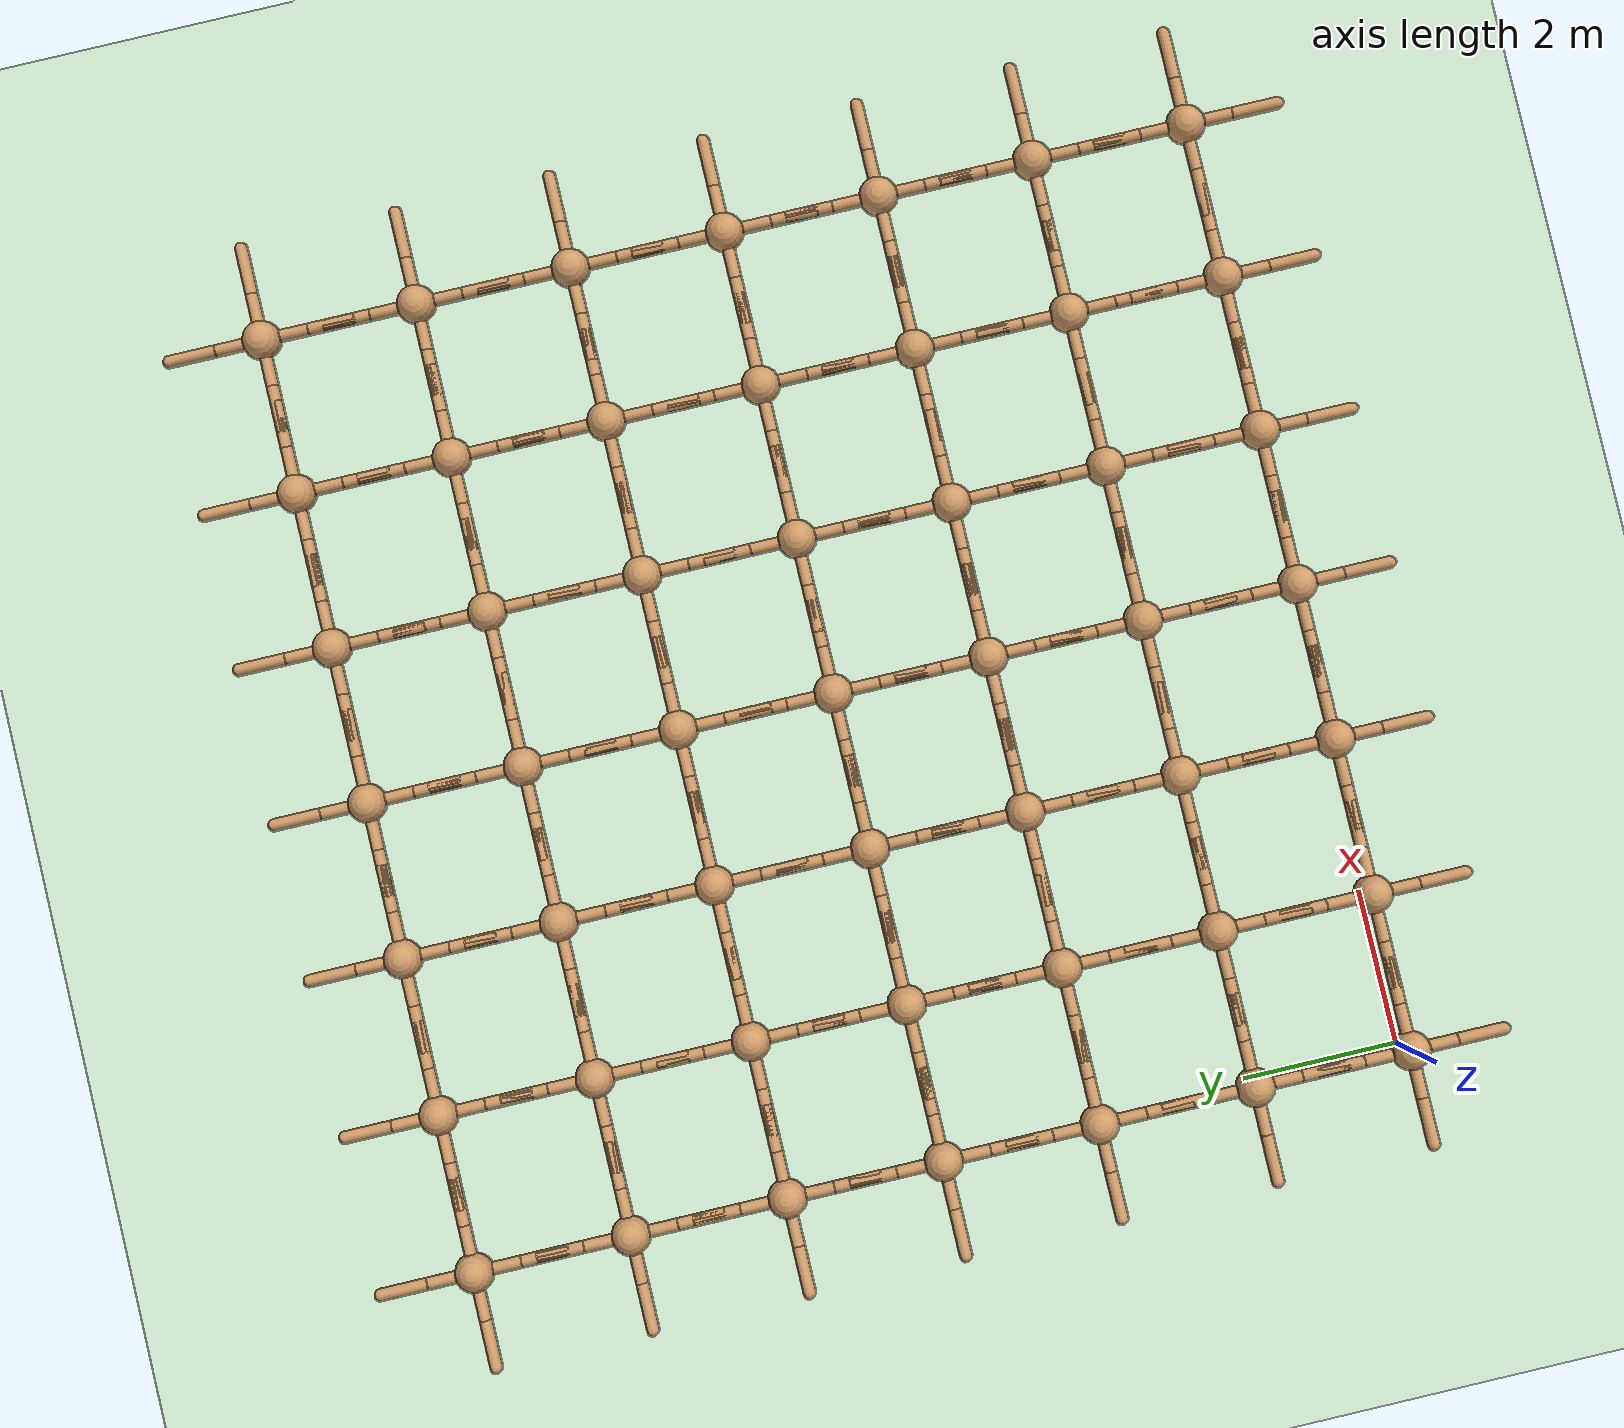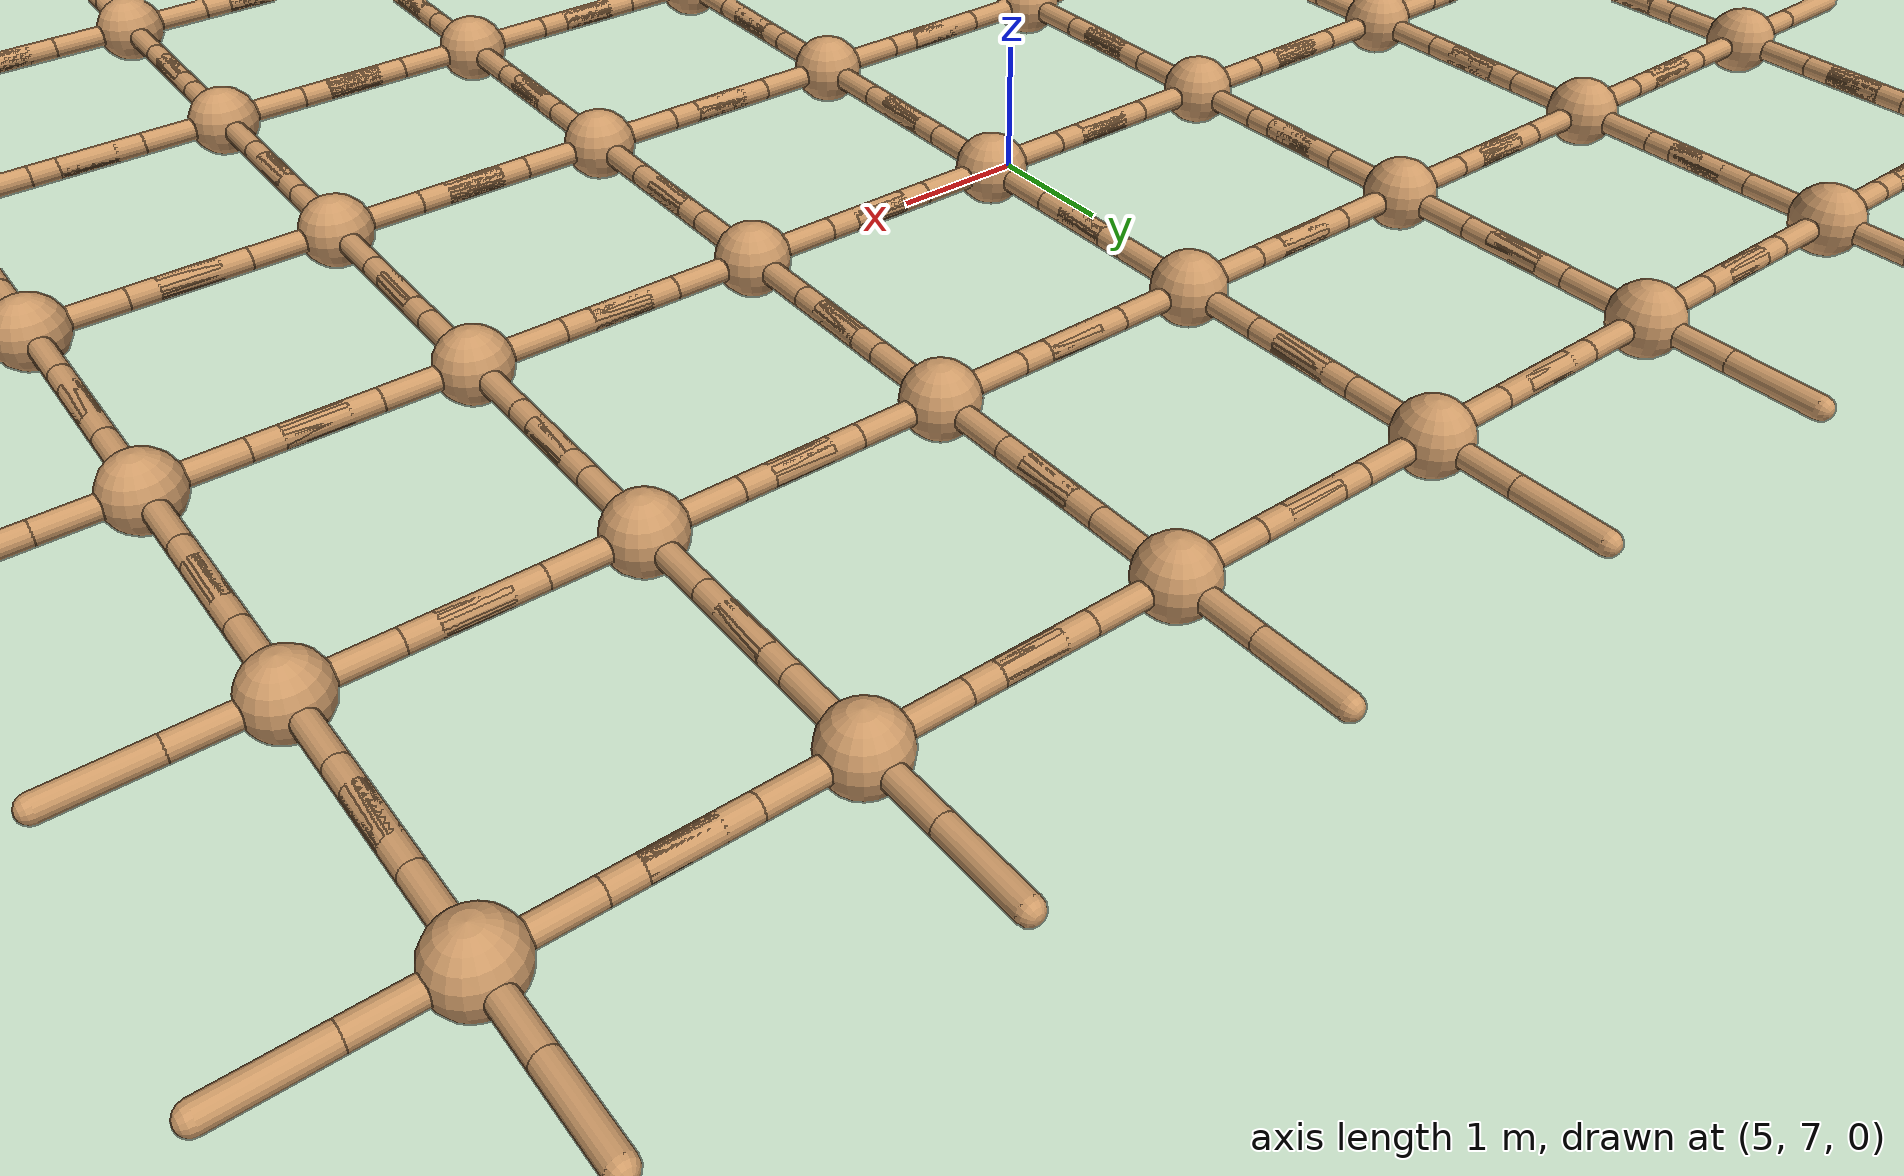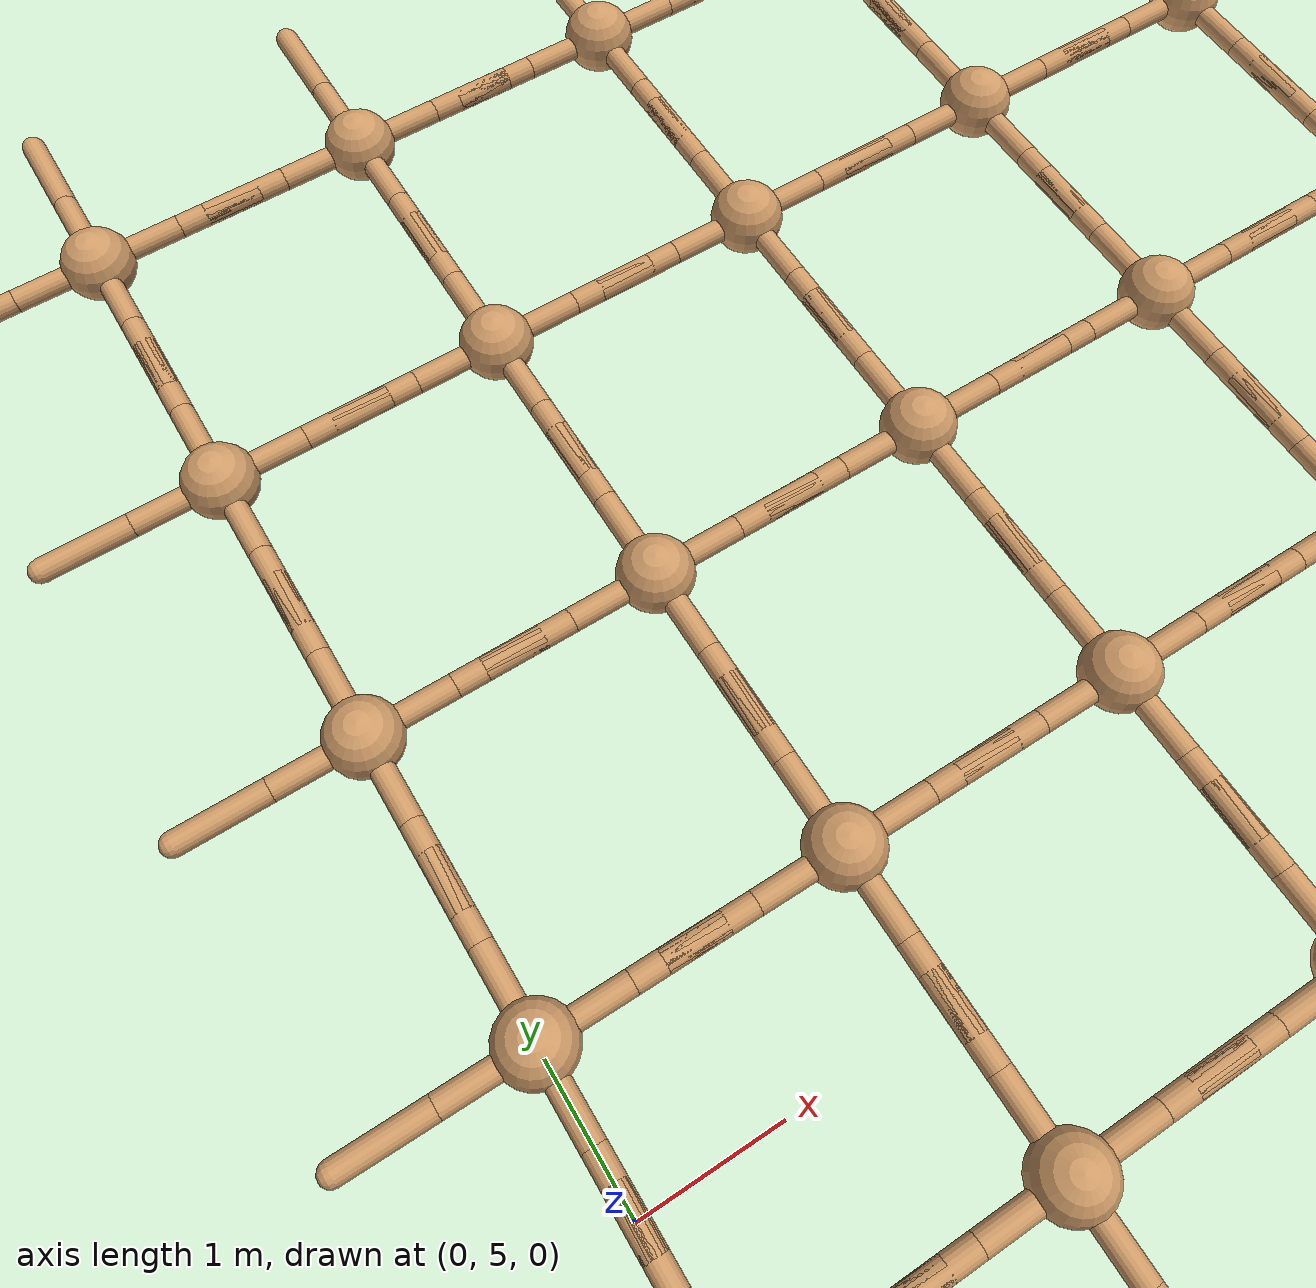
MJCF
<?xml version="1.0" encoding="utf-8"?>
<mujoco model="ant">
	<compiler angle="degree" coordinate="local" inertiafromgeom="true"/>
	<option integrator="RK4" timestep="0.01"/>
	<size nconmax="500" njmax="1000"/>
	<custom>
		<numeric name="init_qpos" data="0.0 0.0 0.55 1.0 0.0 0.0 0.0 0.0 1.0 0.0 -1.0 0.0 -1.0 0.0 1.0"/>
	</custom>
	<default>
		<joint armature="1" damping="1" limited="true"/>
		<geom conaffinity="0" condim="3" density="5.0" friction="1 0.5 0.5" margin="0.01" rgba="0.8 0.6 0.4 1"/>
	</default>
	<asset>
		<texture builtin="gradient" height="100" rgb1="1 1 1" rgb2="0 0 0" type="skybox" width="100"/>
		<texture builtin="flat" height="1278" mark="cross" markrgb="1 1 1" name="texgeom" random="0.01" rgb1="0.8 0.6 0.4" rgb2="0.8 0.6 0.4" type="cube" width="127"/>
		<texture builtin="checker" height="100" name="texplane" rgb1="0 0 0" rgb2="0.8 0.8 0.8" type="2d" width="100"/>
		<material name="MatPlane" reflectance="0.5" shininess="1" specular="1" texrepeat="60 60" texture="texplane"/>
		<material name="geom" texture="texgeom" texuniform="true"/>
	</asset>
	<worldbody>
		<light cutoff="100" diffuse="1 1 1" dir="0 0 -1.3" directional="true" exponent="1" pos="0 0 1.3" specular="0.1 0.1 0.1"/>
		<geom conaffinity="1" condim="3" material="MatPlane" name="floor" pos="0 0 0" rgba="0.8 0.9 0.8 1" size="40 40 40" type="plane"/>
		<body name="torso_ant_0_0" pos="0.0 0.0 0.75">
			<camera mode="trackcom" name="track_ant_0_0" pos="0 -3 0.3" xyaxes="1 0 0 0 0 1"/>
			<geom name="torso_geom_ant_0_0" pos="0 0 0" size="0.25" type="sphere"/>
			<joint armature="0" damping="0" limited="false" margin="0.01" name="root_ant_0_0" pos="0 0 0" type="free"/>
			<body name="front_right_leg_ant_0_0" pos="0 0 0" euler="0 0 0.0">
				<geom fromto="0 0 0 0.2 0 0" name="aux_geom_front_right_leg_ant_0_0" size="0.08" type="capsule"/>
				<body name="aux_body_front_right_leg_ant_0_0" pos="0.2 0 0">
					<joint axis="0 0 1" name="hip_joint_front_right_leg_ant_0_0" pos="0.0 0.0 0.0" range="-30 30" type="hinge"/>
					<geom fromto="0.0 0.0 0.0 0.4 0.0 0.0" name="leg_geom_front_right_leg_ant_0_0" size="0.08" type="capsule"/>
					<body name="ankle_body_front_right_leg_ant_0_0" pos="0.4 0.0 0">
						<joint axis="0 1 0" name="ankle_joint_front_right_leg_ant_0_0" pos="0.0 0.0 0.0" range="30 70" type="hinge"/>
						<geom fromto="0.0 0.0 0.0 0.6 0.0 0.0" name="ankle_geom_front_right_leg_ant_0_0" size="0.08" type="capsule"/>
					</body>
				</body>
			</body>
			<body name="front_left_leg_ant_0_0" pos="0 0 0" euler="0 0 90">
				<geom fromto="0 0 0 0.2 0 0" name="aux_geom_front_left_leg_ant_0_0" size="0.08" type="capsule"/>
				<body name="aux_body_front_left_leg_ant_0_0" pos="0.2 0 0">
					<joint axis="0 0 1" name="hip_joint_front_left_leg_ant_0_0" pos="0.0 0.0 0.0" range="-30 30" type="hinge"/>
					<geom fromto="0.0 0.0 0.0 0.4 0.0 0.0" name="leg_geom_front_left_leg_ant_0_0" size="0.08" type="capsule"/>
					<body name="ankle_body_front_left_leg_ant_0_0" pos="0.4 0.0 0">
						<joint axis="0 1 0" name="ankle_joint_front_left_leg_ant_0_0" pos="0.0 0.0 0.0" range="30 70" type="hinge"/>
						<geom fromto="0.0 0.0 0.0 0.6 0.0 0.0" name="ankle_geom_front_left_leg_ant_0_0" size="0.08" type="capsule"/>
					</body>
				</body>
			</body>
			<body name="back_left_leg_ant_0_0" pos="0 0 0" euler="0 0 180">
				<geom fromto="0 0 0 0.2 0 0" name="aux_geom_back_left_leg_ant_0_0" size="0.08" type="capsule"/>
				<body name="aux_body_back_left_leg_ant_0_0" pos="0.2 0 0">
					<joint axis="0 0 1" name="hip_joint_back_left_leg_ant_0_0" pos="0.0 0.0 0.0" range="-30 30" type="hinge"/>
					<geom fromto="0.0 0.0 0.0 0.4 0.0 0.0" name="leg_geom_back_left_leg_ant_0_0" size="0.08" type="capsule"/>
					<body name="ankle_body_back_left_leg_ant_0_0" pos="0.4 0.0 0">
						<joint axis="0 1 0" name="ankle_joint_back_left_leg_ant_0_0" pos="0.0 0.0 0.0" range="30 70" type="hinge"/>
						<geom fromto="0.0 0.0 0.0 0.6 0.0 0.0" name="ankle_geom_back_left_leg_ant_0_0" size="0.08" type="capsule"/>
					</body>
				</body>
			</body>
			<body name="back_right_leg_ant_0_0" pos="0 0 0" euler="0 0 270">
				<geom fromto="0 0 0 0.2 0 0" name="aux_geom_back_right_leg_ant_0_0" size="0.08" type="capsule"/>
				<body name="aux_body_back_right_leg_ant_0_0" pos="0.2 0 0">
					<joint axis="0 0 1" name="hip_joint_back_right_leg_ant_0_0" pos="0.0 0.0 0.0" range="-30 30" type="hinge"/>
					<geom fromto="0.0 0.0 0.0 0.4 0.0 0.0" name="leg_geom_back_right_leg_ant_0_0" size="0.08" type="capsule"/>
					<body name="ankle_body_back_right_leg_ant_0_0" pos="0.4 0.0 0">
						<joint axis="0 1 0" name="ankle_joint_back_right_leg_ant_0_0" pos="0.0 0.0 0.0" range="30 70" type="hinge"/>
						<geom fromto="0.0 0.0 0.0 0.6 0.0 0.0" name="ankle_geom_back_right_leg_ant_0_0" size="0.08" type="capsule"/>
					</body>
				</body>
			</body>
		</body>
		<body name="torso_ant_0_1" pos="2.0 0.0 0.75">
			<camera mode="trackcom" name="track_ant_0_1" pos="0 -3 0.3" xyaxes="1 0 0 0 0 1"/>
			<geom name="torso_geom_ant_0_1" pos="0 0 0" size="0.25" type="sphere"/>
			<joint armature="0" damping="0" limited="false" margin="0.01" name="root_ant_0_1" pos="0 0 0" type="free"/>
			<body name="front_right_leg_ant_0_1" pos="0 0 0" euler="0 0 0.0">
				<geom fromto="0 0 0 0.2 0 0" name="aux_geom_front_right_leg_ant_0_1" size="0.08" type="capsule"/>
				<body name="aux_body_front_right_leg_ant_0_1" pos="0.2 0 0">
					<joint axis="0 0 1" name="hip_joint_front_right_leg_ant_0_1" pos="0.0 0.0 0.0" range="-30 30" type="hinge"/>
					<geom fromto="0.0 0.0 0.0 0.4 0.0 0.0" name="leg_geom_front_right_leg_ant_0_1" size="0.08" type="capsule"/>
					<body name="ankle_body_front_right_leg_ant_0_1" pos="0.4 0.0 0">
						<joint axis="0 1 0" name="ankle_joint_front_right_leg_ant_0_1" pos="0.0 0.0 0.0" range="30 70" type="hinge"/>
						<geom fromto="0.0 0.0 0.0 0.6 0.0 0.0" name="ankle_geom_front_right_leg_ant_0_1" size="0.08" type="capsule"/>
					</body>
				</body>
			</body>
			<body name="front_left_leg_ant_0_1" pos="0 0 0" euler="0 0 90">
				<geom fromto="0 0 0 0.2 0 0" name="aux_geom_front_left_leg_ant_0_1" size="0.08" type="capsule"/>
				<body name="aux_body_front_left_leg_ant_0_1" pos="0.2 0 0">
					<joint axis="0 0 1" name="hip_joint_front_left_leg_ant_0_1" pos="0.0 0.0 0.0" range="-30 30" type="hinge"/>
					<geom fromto="0.0 0.0 0.0 0.4 0.0 0.0" name="leg_geom_front_left_leg_ant_0_1" size="0.08" type="capsule"/>
					<body name="ankle_body_front_left_leg_ant_0_1" pos="0.4 0.0 0">
						<joint axis="0 1 0" name="ankle_joint_front_left_leg_ant_0_1" pos="0.0 0.0 0.0" range="30 70" type="hinge"/>
						<geom fromto="0.0 0.0 0.0 0.6 0.0 0.0" name="ankle_geom_front_left_leg_ant_0_1" size="0.08" type="capsule"/>
					</body>
				</body>
			</body>
			<body name="back_left_leg_ant_0_1" pos="0 0 0" euler="0 0 180">
				<geom fromto="0 0 0 0.2 0 0" name="aux_geom_back_left_leg_ant_0_1" size="0.08" type="capsule"/>
				<body name="aux_body_back_left_leg_ant_0_1" pos="0.2 0 0">
					<joint axis="0 0 1" name="hip_joint_back_left_leg_ant_0_1" pos="0.0 0.0 0.0" range="-30 30" type="hinge"/>
					<geom fromto="0.0 0.0 0.0 0.4 0.0 0.0" name="leg_geom_back_left_leg_ant_0_1" size="0.08" type="capsule"/>
					<body name="ankle_body_back_left_leg_ant_0_1" pos="0.4 0.0 0">
						<joint axis="0 1 0" name="ankle_joint_back_left_leg_ant_0_1" pos="0.0 0.0 0.0" range="30 70" type="hinge"/>
						<geom fromto="0.0 0.0 0.0 0.6 0.0 0.0" name="ankle_geom_back_left_leg_ant_0_1" size="0.08" type="capsule"/>
					</body>
				</body>
			</body>
			<body name="back_right_leg_ant_0_1" pos="0 0 0" euler="0 0 270">
				<geom fromto="0 0 0 0.2 0 0" name="aux_geom_back_right_leg_ant_0_1" size="0.08" type="capsule"/>
				<body name="aux_body_back_right_leg_ant_0_1" pos="0.2 0 0">
					<joint axis="0 0 1" name="hip_joint_back_right_leg_ant_0_1" pos="0.0 0.0 0.0" range="-30 30" type="hinge"/>
					<geom fromto="0.0 0.0 0.0 0.4 0.0 0.0" name="leg_geom_back_right_leg_ant_0_1" size="0.08" type="capsule"/>
					<body name="ankle_body_back_right_leg_ant_0_1" pos="0.4 0.0 0">
						<joint axis="0 1 0" name="ankle_joint_back_right_leg_ant_0_1" pos="0.0 0.0 0.0" range="30 70" type="hinge"/>
						<geom fromto="0.0 0.0 0.0 0.6 0.0 0.0" name="ankle_geom_back_right_leg_ant_0_1" size="0.08" type="capsule"/>
					</body>
				</body>
			</body>
		</body>
		<body name="torso_ant_0_2" pos="4.0 0.0 0.75">
			<camera mode="trackcom" name="track_ant_0_2" pos="0 -3 0.3" xyaxes="1 0 0 0 0 1"/>
			<geom name="torso_geom_ant_0_2" pos="0 0 0" size="0.25" type="sphere"/>
			<joint armature="0" damping="0" limited="false" margin="0.01" name="root_ant_0_2" pos="0 0 0" type="free"/>
			<body name="front_right_leg_ant_0_2" pos="0 0 0" euler="0 0 0.0">
				<geom fromto="0 0 0 0.2 0 0" name="aux_geom_front_right_leg_ant_0_2" size="0.08" type="capsule"/>
				<body name="aux_body_front_right_leg_ant_0_2" pos="0.2 0 0">
					<joint axis="0 0 1" name="hip_joint_front_right_leg_ant_0_2" pos="0.0 0.0 0.0" range="-30 30" type="hinge"/>
					<geom fromto="0.0 0.0 0.0 0.4 0.0 0.0" name="leg_geom_front_right_leg_ant_0_2" size="0.08" type="capsule"/>
					<body name="ankle_body_front_right_leg_ant_0_2" pos="0.4 0.0 0">
						<joint axis="0 1 0" name="ankle_joint_front_right_leg_ant_0_2" pos="0.0 0.0 0.0" range="30 70" type="hinge"/>
						<geom fromto="0.0 0.0 0.0 0.6 0.0 0.0" name="ankle_geom_front_right_leg_ant_0_2" size="0.08" type="capsule"/>
					</body>
				</body>
			</body>
			<body name="front_left_leg_ant_0_2" pos="0 0 0" euler="0 0 90">
				<geom fromto="0 0 0 0.2 0 0" name="aux_geom_front_left_leg_ant_0_2" size="0.08" type="capsule"/>
				<body name="aux_body_front_left_leg_ant_0_2" pos="0.2 0 0">
					<joint axis="0 0 1" name="hip_joint_front_left_leg_ant_0_2" pos="0.0 0.0 0.0" range="-30 30" type="hinge"/>
					<geom fromto="0.0 0.0 0.0 0.4 0.0 0.0" name="leg_geom_front_left_leg_ant_0_2" size="0.08" type="capsule"/>
					<body name="ankle_body_front_left_leg_ant_0_2" pos="0.4 0.0 0">
						<joint axis="0 1 0" name="ankle_joint_front_left_leg_ant_0_2" pos="0.0 0.0 0.0" range="30 70" type="hinge"/>
						<geom fromto="0.0 0.0 0.0 0.6 0.0 0.0" name="ankle_geom_front_left_leg_ant_0_2" size="0.08" type="capsule"/>
					</body>
				</body>
			</body>
			<body name="back_left_leg_ant_0_2" pos="0 0 0" euler="0 0 180">
				<geom fromto="0 0 0 0.2 0 0" name="aux_geom_back_left_leg_ant_0_2" size="0.08" type="capsule"/>
				<body name="aux_body_back_left_leg_ant_0_2" pos="0.2 0 0">
					<joint axis="0 0 1" name="hip_joint_back_left_leg_ant_0_2" pos="0.0 0.0 0.0" range="-30 30" type="hinge"/>
					<geom fromto="0.0 0.0 0.0 0.4 0.0 0.0" name="leg_geom_back_left_leg_ant_0_2" size="0.08" type="capsule"/>
					<body name="ankle_body_back_left_leg_ant_0_2" pos="0.4 0.0 0">
						<joint axis="0 1 0" name="ankle_joint_back_left_leg_ant_0_2" pos="0.0 0.0 0.0" range="30 70" type="hinge"/>
						<geom fromto="0.0 0.0 0.0 0.6 0.0 0.0" name="ankle_geom_back_left_leg_ant_0_2" size="0.08" type="capsule"/>
					</body>
				</body>
			</body>
			<body name="back_right_leg_ant_0_2" pos="0 0 0" euler="0 0 270">
				<geom fromto="0 0 0 0.2 0 0" name="aux_geom_back_right_leg_ant_0_2" size="0.08" type="capsule"/>
				<body name="aux_body_back_right_leg_ant_0_2" pos="0.2 0 0">
					<joint axis="0 0 1" name="hip_joint_back_right_leg_ant_0_2" pos="0.0 0.0 0.0" range="-30 30" type="hinge"/>
					<geom fromto="0.0 0.0 0.0 0.4 0.0 0.0" name="leg_geom_back_right_leg_ant_0_2" size="0.08" type="capsule"/>
					<body name="ankle_body_back_right_leg_ant_0_2" pos="0.4 0.0 0">
						<joint axis="0 1 0" name="ankle_joint_back_right_leg_ant_0_2" pos="0.0 0.0 0.0" range="30 70" type="hinge"/>
						<geom fromto="0.0 0.0 0.0 0.6 0.0 0.0" name="ankle_geom_back_right_leg_ant_0_2" size="0.08" type="capsule"/>
					</body>
				</body>
			</body>
		</body>
		<body name="torso_ant_0_3" pos="6.0 0.0 0.75">
			<camera mode="trackcom" name="track_ant_0_3" pos="0 -3 0.3" xyaxes="1 0 0 0 0 1"/>
			<geom name="torso_geom_ant_0_3" pos="0 0 0" size="0.25" type="sphere"/>
			<joint armature="0" damping="0" limited="false" margin="0.01" name="root_ant_0_3" pos="0 0 0" type="free"/>
			<body name="front_right_leg_ant_0_3" pos="0 0 0" euler="0 0 0.0">
				<geom fromto="0 0 0 0.2 0 0" name="aux_geom_front_right_leg_ant_0_3" size="0.08" type="capsule"/>
				<body name="aux_body_front_right_leg_ant_0_3" pos="0.2 0 0">
					<joint axis="0 0 1" name="hip_joint_front_right_leg_ant_0_3" pos="0.0 0.0 0.0" range="-30 30" type="hinge"/>
					<geom fromto="0.0 0.0 0.0 0.4 0.0 0.0" name="leg_geom_front_right_leg_ant_0_3" size="0.08" type="capsule"/>
					<body name="ankle_body_front_right_leg_ant_0_3" pos="0.4 0.0 0">
						<joint axis="0 1 0" name="ankle_joint_front_right_leg_ant_0_3" pos="0.0 0.0 0.0" range="30 70" type="hinge"/>
						<geom fromto="0.0 0.0 0.0 0.6 0.0 0.0" name="ankle_geom_front_right_leg_ant_0_3" size="0.08" type="capsule"/>
					</body>
				</body>
			</body>
			<body name="front_left_leg_ant_0_3" pos="0 0 0" euler="0 0 90">
				<geom fromto="0 0 0 0.2 0 0" name="aux_geom_front_left_leg_ant_0_3" size="0.08" type="capsule"/>
				<body name="aux_body_front_left_leg_ant_0_3" pos="0.2 0 0">
					<joint axis="0 0 1" name="hip_joint_front_left_leg_ant_0_3" pos="0.0 0.0 0.0" range="-30 30" type="hinge"/>
					<geom fromto="0.0 0.0 0.0 0.4 0.0 0.0" name="leg_geom_front_left_leg_ant_0_3" size="0.08" type="capsule"/>
					<body name="ankle_body_front_left_leg_ant_0_3" pos="0.4 0.0 0">
						<joint axis="0 1 0" name="ankle_joint_front_left_leg_ant_0_3" pos="0.0 0.0 0.0" range="30 70" type="hinge"/>
						<geom fromto="0.0 0.0 0.0 0.6 0.0 0.0" name="ankle_geom_front_left_leg_ant_0_3" size="0.08" type="capsule"/>
					</body>
				</body>
			</body>
			<body name="back_left_leg_ant_0_3" pos="0 0 0" euler="0 0 180">
				<geom fromto="0 0 0 0.2 0 0" name="aux_geom_back_left_leg_ant_0_3" size="0.08" type="capsule"/>
				<body name="aux_body_back_left_leg_ant_0_3" pos="0.2 0 0">
					<joint axis="0 0 1" name="hip_joint_back_left_leg_ant_0_3" pos="0.0 0.0 0.0" range="-30 30" type="hinge"/>
					<geom fromto="0.0 0.0 0.0 0.4 0.0 0.0" name="leg_geom_back_left_leg_ant_0_3" size="0.08" type="capsule"/>
					<body name="ankle_body_back_left_leg_ant_0_3" pos="0.4 0.0 0">
						<joint axis="0 1 0" name="ankle_joint_back_left_leg_ant_0_3" pos="0.0 0.0 0.0" range="30 70" type="hinge"/>
						<geom fromto="0.0 0.0 0.0 0.6 0.0 0.0" name="ankle_geom_back_left_leg_ant_0_3" size="0.08" type="capsule"/>
					</body>
				</body>
			</body>
			<body name="back_right_leg_ant_0_3" pos="0 0 0" euler="0 0 270">
				<geom fromto="0 0 0 0.2 0 0" name="aux_geom_back_right_leg_ant_0_3" size="0.08" type="capsule"/>
				<body name="aux_body_back_right_leg_ant_0_3" pos="0.2 0 0">
					<joint axis="0 0 1" name="hip_joint_back_right_leg_ant_0_3" pos="0.0 0.0 0.0" range="-30 30" type="hinge"/>
					<geom fromto="0.0 0.0 0.0 0.4 0.0 0.0" name="leg_geom_back_right_leg_ant_0_3" size="0.08" type="capsule"/>
					<body name="ankle_body_back_right_leg_ant_0_3" pos="0.4 0.0 0">
						<joint axis="0 1 0" name="ankle_joint_back_right_leg_ant_0_3" pos="0.0 0.0 0.0" range="30 70" type="hinge"/>
						<geom fromto="0.0 0.0 0.0 0.6 0.0 0.0" name="ankle_geom_back_right_leg_ant_0_3" size="0.08" type="capsule"/>
					</body>
				</body>
			</body>
		</body>
		<body name="torso_ant_0_4" pos="8.0 0.0 0.75">
			<camera mode="trackcom" name="track_ant_0_4" pos="0 -3 0.3" xyaxes="1 0 0 0 0 1"/>
			<geom name="torso_geom_ant_0_4" pos="0 0 0" size="0.25" type="sphere"/>
			<joint armature="0" damping="0" limited="false" margin="0.01" name="root_ant_0_4" pos="0 0 0" type="free"/>
			<body name="front_right_leg_ant_0_4" pos="0 0 0" euler="0 0 0.0">
				<geom fromto="0 0 0 0.2 0 0" name="aux_geom_front_right_leg_ant_0_4" size="0.08" type="capsule"/>
				<body name="aux_body_front_right_leg_ant_0_4" pos="0.2 0 0">
					<joint axis="0 0 1" name="hip_joint_front_right_leg_ant_0_4" pos="0.0 0.0 0.0" range="-30 30" type="hinge"/>
					<geom fromto="0.0 0.0 0.0 0.4 0.0 0.0" name="leg_geom_front_right_leg_ant_0_4" size="0.08" type="capsule"/>
					<body name="ankle_body_front_right_leg_ant_0_4" pos="0.4 0.0 0">
						<joint axis="0 1 0" name="ankle_joint_front_right_leg_ant_0_4" pos="0.0 0.0 0.0" range="30 70" type="hinge"/>
						<geom fromto="0.0 0.0 0.0 0.6 0.0 0.0" name="ankle_geom_front_right_leg_ant_0_4" size="0.08" type="capsule"/>
					</body>
				</body>
			</body>
			<body name="front_left_leg_ant_0_4" pos="0 0 0" euler="0 0 90">
				<geom fromto="0 0 0 0.2 0 0" name="aux_geom_front_left_leg_ant_0_4" size="0.08" type="capsule"/>
				<body name="aux_body_front_left_leg_ant_0_4" pos="0.2 0 0">
					<joint axis="0 0 1" name="hip_joint_front_left_leg_ant_0_4" pos="0.0 0.0 0.0" range="-30 30" type="hinge"/>
					<geom fromto="0.0 0.0 0.0 0.4 0.0 0.0" name="leg_geom_front_left_leg_ant_0_4" size="0.08" type="capsule"/>
					<body name="ankle_body_front_left_leg_ant_0_4" pos="0.4 0.0 0">
						<joint axis="0 1 0" name="ankle_joint_front_left_leg_ant_0_4" pos="0.0 0.0 0.0" range="30 70" type="hinge"/>
						<geom fromto="0.0 0.0 0.0 0.6 0.0 0.0" name="ankle_geom_front_left_leg_ant_0_4" size="0.08" type="capsule"/>
					</body>
				</body>
			</body>
			<body name="back_left_leg_ant_0_4" pos="0 0 0" euler="0 0 180">
				<geom fromto="0 0 0 0.2 0 0" name="aux_geom_back_left_leg_ant_0_4" size="0.08" type="capsule"/>
				<body name="aux_body_back_left_leg_ant_0_4" pos="0.2 0 0">
					<joint axis="0 0 1" name="hip_joint_back_left_leg_ant_0_4" pos="0.0 0.0 0.0" range="-30 30" type="hinge"/>
					<geom fromto="0.0 0.0 0.0 0.4 0.0 0.0" name="leg_geom_back_left_leg_ant_0_4" size="0.08" type="capsule"/>
					<body name="ankle_body_back_left_leg_ant_0_4" pos="0.4 0.0 0">
						<joint axis="0 1 0" name="ankle_joint_back_left_leg_ant_0_4" pos="0.0 0.0 0.0" range="30 70" type="hinge"/>
						<geom fromto="0.0 0.0 0.0 0.6 0.0 0.0" name="ankle_geom_back_left_leg_ant_0_4" size="0.08" type="capsule"/>
					</body>
				</body>
			</body>
			<body name="back_right_leg_ant_0_4" pos="0 0 0" euler="0 0 270">
				<geom fromto="0 0 0 0.2 0 0" name="aux_geom_back_right_leg_ant_0_4" size="0.08" type="capsule"/>
				<body name="aux_body_back_right_leg_ant_0_4" pos="0.2 0 0">
					<joint axis="0 0 1" name="hip_joint_back_right_leg_ant_0_4" pos="0.0 0.0 0.0" range="-30 30" type="hinge"/>
					<geom fromto="0.0 0.0 0.0 0.4 0.0 0.0" name="leg_geom_back_right_leg_ant_0_4" size="0.08" type="capsule"/>
					<body name="ankle_body_back_right_leg_ant_0_4" pos="0.4 0.0 0">
						<joint axis="0 1 0" name="ankle_joint_back_right_leg_ant_0_4" pos="0.0 0.0 0.0" range="30 70" type="hinge"/>
						<geom fromto="0.0 0.0 0.0 0.6 0.0 0.0" name="ankle_geom_back_right_leg_ant_0_4" size="0.08" type="capsule"/>
					</body>
				</body>
			</body>
		</body>
		<body name="torso_ant_0_5" pos="10.0 0.0 0.75">
			<camera mode="trackcom" name="track_ant_0_5" pos="0 -3 0.3" xyaxes="1 0 0 0 0 1"/>
			<geom name="torso_geom_ant_0_5" pos="0 0 0" size="0.25" type="sphere"/>
			<joint armature="0" damping="0" limited="false" margin="0.01" name="root_ant_0_5" pos="0 0 0" type="free"/>
			<body name="front_right_leg_ant_0_5" pos="0 0 0" euler="0 0 0.0">
				<geom fromto="0 0 0 0.2 0 0" name="aux_geom_front_right_leg_ant_0_5" size="0.08" type="capsule"/>
				<body name="aux_body_front_right_leg_ant_0_5" pos="0.2 0 0">
					<joint axis="0 0 1" name="hip_joint_front_right_leg_ant_0_5" pos="0.0 0.0 0.0" range="-30 30" type="hinge"/>
					<geom fromto="0.0 0.0 0.0 0.4 0.0 0.0" name="leg_geom_front_right_leg_ant_0_5" size="0.08" type="capsule"/>
					<body name="ankle_body_front_right_leg_ant_0_5" pos="0.4 0.0 0">
						<joint axis="0 1 0" name="ankle_joint_front_right_leg_ant_0_5" pos="0.0 0.0 0.0" range="30 70" type="hinge"/>
						<geom fromto="0.0 0.0 0.0 0.6 0.0 0.0" name="ankle_geom_front_right_leg_ant_0_5" size="0.08" type="capsule"/>
					</body>
				</body>
			</body>
			<body name="front_left_leg_ant_0_5" pos="0 0 0" euler="0 0 90">
				<geom fromto="0 0 0 0.2 0 0" name="aux_geom_front_left_leg_ant_0_5" size="0.08" type="capsule"/>
				<body name="aux_body_front_left_leg_ant_0_5" pos="0.2 0 0">
					<joint axis="0 0 1" name="hip_joint_front_left_leg_ant_0_5" pos="0.0 0.0 0.0" range="-30 30" type="hinge"/>
					<geom fromto="0.0 0.0 0.0 0.4 0.0 0.0" name="leg_geom_front_left_leg_ant_0_5" size="0.08" type="capsule"/>
					<body name="ankle_body_front_left_leg_ant_0_5" pos="0.4 0.0 0">
						<joint axis="0 1 0" name="ankle_joint_front_left_leg_ant_0_5" pos="0.0 0.0 0.0" range="30 70" type="hinge"/>
						<geom fromto="0.0 0.0 0.0 0.6 0.0 0.0" name="ankle_geom_front_left_leg_ant_0_5" size="0.08" type="capsule"/>
					</body>
				</body>
			</body>
			<body name="back_left_leg_ant_0_5" pos="0 0 0" euler="0 0 180">
				<geom fromto="0 0 0 0.2 0 0" name="aux_geom_back_left_leg_ant_0_5" size="0.08" type="capsule"/>
				<body name="aux_body_back_left_leg_ant_0_5" pos="0.2 0 0">
					<joint axis="0 0 1" name="hip_joint_back_left_leg_ant_0_5" pos="0.0 0.0 0.0" range="-30 30" type="hinge"/>
					<geom fromto="0.0 0.0 0.0 0.4 0.0 0.0" name="leg_geom_back_left_leg_ant_0_5" size="0.08" type="capsule"/>
					<body name="ankle_body_back_left_leg_ant_0_5" pos="0.4 0.0 0">
						<joint axis="0 1 0" name="ankle_joint_back_left_leg_ant_0_5" pos="0.0 0.0 0.0" range="30 70" type="hinge"/>
						<geom fromto="0.0 0.0 0.0 0.6 0.0 0.0" name="ankle_geom_back_left_leg_ant_0_5" size="0.08" type="capsule"/>
					</body>
				</body>
			</body>
			<body name="back_right_leg_ant_0_5" pos="0 0 0" euler="0 0 270">
				<geom fromto="0 0 0 0.2 0 0" name="aux_geom_back_right_leg_ant_0_5" size="0.08" type="capsule"/>
				<body name="aux_body_back_right_leg_ant_0_5" pos="0.2 0 0">
					<joint axis="0 0 1" name="hip_joint_back_right_leg_ant_0_5" pos="0.0 0.0 0.0" range="-30 30" type="hinge"/>
					<geom fromto="0.0 0.0 0.0 0.4 0.0 0.0" name="leg_geom_back_right_leg_ant_0_5" size="0.08" type="capsule"/>
					<body name="ankle_body_back_right_leg_ant_0_5" pos="0.4 0.0 0">
						<joint axis="0 1 0" name="ankle_joint_back_right_leg_ant_0_5" pos="0.0 0.0 0.0" range="30 70" type="hinge"/>
						<geom fromto="0.0 0.0 0.0 0.6 0.0 0.0" name="ankle_geom_back_right_leg_ant_0_5" size="0.08" type="capsule"/>
					</body>
				</body>
			</body>
		</body>
		<body name="torso_ant_0_6" pos="12.0 0.0 0.75">
			<camera mode="trackcom" name="track_ant_0_6" pos="0 -3 0.3" xyaxes="1 0 0 0 0 1"/>
			<geom name="torso_geom_ant_0_6" pos="0 0 0" size="0.25" type="sphere"/>
			<joint armature="0" damping="0" limited="false" margin="0.01" name="root_ant_0_6" pos="0 0 0" type="free"/>
			<body name="front_right_leg_ant_0_6" pos="0 0 0" euler="0 0 0.0">
				<geom fromto="0 0 0 0.2 0 0" name="aux_geom_front_right_leg_ant_0_6" size="0.08" type="capsule"/>
				<body name="aux_body_front_right_leg_ant_0_6" pos="0.2 0 0">
					<joint axis="0 0 1" name="hip_joint_front_right_leg_ant_0_6" pos="0.0 0.0 0.0" range="-30 30" type="hinge"/>
					<geom fromto="0.0 0.0 0.0 0.4 0.0 0.0" name="leg_geom_front_right_leg_ant_0_6" size="0.08" type="capsule"/>
					<body name="ankle_body_front_right_leg_ant_0_6" pos="0.4 0.0 0">
						<joint axis="0 1 0" name="ankle_joint_front_right_leg_ant_0_6" pos="0.0 0.0 0.0" range="30 70" type="hinge"/>
						<geom fromto="0.0 0.0 0.0 0.6 0.0 0.0" name="ankle_geom_front_right_leg_ant_0_6" size="0.08" type="capsule"/>
					</body>
				</body>
			</body>
			<body name="front_left_leg_ant_0_6" pos="0 0 0" euler="0 0 90">
				<geom fromto="0 0 0 0.2 0 0" name="aux_geom_front_left_leg_ant_0_6" size="0.08" type="capsule"/>
				<body name="aux_body_front_left_leg_ant_0_6" pos="0.2 0 0">
					<joint axis="0 0 1" name="hip_joint_front_left_leg_ant_0_6" pos="0.0 0.0 0.0" range="-30 30" type="hinge"/>
					<geom fromto="0.0 0.0 0.0 0.4 0.0 0.0" name="leg_geom_front_left_leg_ant_0_6" size="0.08" type="capsule"/>
					<body name="ankle_body_front_left_leg_ant_0_6" pos="0.4 0.0 0">
						<joint axis="0 1 0" name="ankle_joint_front_left_leg_ant_0_6" pos="0.0 0.0 0.0" range="30 70" type="hinge"/>
						<geom fromto="0.0 0.0 0.0 0.6 0.0 0.0" name="ankle_geom_front_left_leg_ant_0_6" size="0.08" type="capsule"/>
					</body>
				</body>
			</body>
			<body name="back_left_leg_ant_0_6" pos="0 0 0" euler="0 0 180">
				<geom fromto="0 0 0 0.2 0 0" name="aux_geom_back_left_leg_ant_0_6" size="0.08" type="capsule"/>
				<body name="aux_body_back_left_leg_ant_0_6" pos="0.2 0 0">
					<joint axis="0 0 1" name="hip_joint_back_left_leg_ant_0_6" pos="0.0 0.0 0.0" range="-30 30" type="hinge"/>
					<geom fromto="0.0 0.0 0.0 0.4 0.0 0.0" name="leg_geom_back_left_leg_ant_0_6" size="0.08" type="capsule"/>
					<body name="ankle_body_back_left_leg_ant_0_6" pos="0.4 0.0 0">
						<joint axis="0 1 0" name="ankle_joint_back_left_leg_ant_0_6" pos="0.0 0.0 0.0" range="30 70" type="hinge"/>
						<geom fromto="0.0 0.0 0.0 0.6 0.0 0.0" name="ankle_geom_back_left_leg_ant_0_6" size="0.08" type="capsule"/>
					</body>
				</body>
			</body>
			<body name="back_right_leg_ant_0_6" pos="0 0 0" euler="0 0 270">
				<geom fromto="0 0 0 0.2 0 0" name="aux_geom_back_right_leg_ant_0_6" size="0.08" type="capsule"/>
				<body name="aux_body_back_right_leg_ant_0_6" pos="0.2 0 0">
					<joint axis="0 0 1" name="hip_joint_back_right_leg_ant_0_6" pos="0.0 0.0 0.0" range="-30 30" type="hinge"/>
					<geom fromto="0.0 0.0 0.0 0.4 0.0 0.0" name="leg_geom_back_right_leg_ant_0_6" size="0.08" type="capsule"/>
					<body name="ankle_body_back_right_leg_ant_0_6" pos="0.4 0.0 0">
						<joint axis="0 1 0" name="ankle_joint_back_right_leg_ant_0_6" pos="0.0 0.0 0.0" range="30 70" type="hinge"/>
						<geom fromto="0.0 0.0 0.0 0.6 0.0 0.0" name="ankle_geom_back_right_leg_ant_0_6" size="0.08" type="capsule"/>
					</body>
				</body>
			</body>
		</body>
		<body name="torso_ant_1_0" pos="0.0 2.0 0.75">
			<camera mode="trackcom" name="track_ant_1_0" pos="0 -3 0.3" xyaxes="1 0 0 0 0 1"/>
			<geom name="torso_geom_ant_1_0" pos="0 0 0" size="0.25" type="sphere"/>
			<joint armature="0" damping="0" limited="false" margin="0.01" name="root_ant_1_0" pos="0 0 0" type="free"/>
			<body name="front_right_leg_ant_1_0" pos="0 0 0" euler="0 0 0.0">
				<geom fromto="0 0 0 0.2 0 0" name="aux_geom_front_right_leg_ant_1_0" size="0.08" type="capsule"/>
				<body name="aux_body_front_right_leg_ant_1_0" pos="0.2 0 0">
					<joint axis="0 0 1" name="hip_joint_front_right_leg_ant_1_0" pos="0.0 0.0 0.0" range="-30 30" type="hinge"/>
					<geom fromto="0.0 0.0 0.0 0.4 0.0 0.0" name="leg_geom_front_right_leg_ant_1_0" size="0.08" type="capsule"/>
					<body name="ankle_body_front_right_leg_ant_1_0" pos="0.4 0.0 0">
						<joint axis="0 1 0" name="ankle_joint_front_right_leg_ant_1_0" pos="0.0 0.0 0.0" range="30 70" type="hinge"/>
						<geom fromto="0.0 0.0 0.0 0.6 0.0 0.0" name="ankle_geom_front_right_leg_ant_1_0" size="0.08" type="capsule"/>
					</body>
				</body>
			</body>
			<body name="front_left_leg_ant_1_0" pos="0 0 0" euler="0 0 90">
				<geom fromto="0 0 0 0.2 0 0" name="aux_geom_front_left_leg_ant_1_0" size="0.08" type="capsule"/>
				<body name="aux_body_front_left_leg_ant_1_0" pos="0.2 0 0">
					<joint axis="0 0 1" name="hip_joint_front_left_leg_ant_1_0" pos="0.0 0.0 0.0" range="-30 30" type="hinge"/>
					<geom fromto="0.0 0.0 0.0 0.4 0.0 0.0" name="leg_geom_front_left_leg_ant_1_0" size="0.08" type="capsule"/>
					<body name="ankle_body_front_left_leg_ant_1_0" pos="0.4 0.0 0">
						<joint axis="0 1 0" name="ankle_joint_front_left_leg_ant_1_0" pos="0.0 0.0 0.0" range="30 70" type="hinge"/>
						<geom fromto="0.0 0.0 0.0 0.6 0.0 0.0" name="ankle_geom_front_left_leg_ant_1_0" size="0.08" type="capsule"/>
					</body>
				</body>
			</body>
			<body name="back_left_leg_ant_1_0" pos="0 0 0" euler="0 0 180">
				<geom fromto="0 0 0 0.2 0 0" name="aux_geom_back_left_leg_ant_1_0" size="0.08" type="capsule"/>
				<body name="aux_body_back_left_leg_ant_1_0" pos="0.2 0 0">
					<joint axis="0 0 1" name="hip_joint_back_left_leg_ant_1_0" pos="0.0 0.0 0.0" range="-30 30" type="hinge"/>
					<geom fromto="0.0 0.0 0.0 0.4 0.0 0.0" name="leg_geom_back_left_leg_ant_1_0" size="0.08" type="capsule"/>
					<body name="ankle_body_back_left_leg_ant_1_0" pos="0.4 0.0 0">
						<joint axis="0 1 0" name="ankle_joint_back_left_leg_ant_1_0" pos="0.0 0.0 0.0" range="30 70" type="hinge"/>
						<geom fromto="0.0 0.0 0.0 0.6 0.0 0.0" name="ankle_geom_back_left_leg_ant_1_0" size="0.08" type="capsule"/>
					</body>
				</body>
			</body>
			<body name="back_right_leg_ant_1_0" pos="0 0 0" euler="0 0 270">
				<geom fromto="0 0 0 0.2 0 0" name="aux_geom_back_right_leg_ant_1_0" size="0.08" type="capsule"/>
				<body name="aux_body_back_right_leg_ant_1_0" pos="0.2 0 0">
					<joint axis="0 0 1" name="hip_joint_back_right_leg_ant_1_0" pos="0.0 0.0 0.0" range="-30 30" type="hinge"/>
					<geom fromto="0.0 0.0 0.0 0.4 0.0 0.0" name="leg_geom_back_right_leg_ant_1_0" size="0.08" type="capsule"/>
					<body name="ankle_body_back_right_leg_ant_1_0" pos="0.4 0.0 0">
						<joint axis="0 1 0" name="ankle_joint_back_right_leg_ant_1_0" pos="0.0 0.0 0.0" range="30 70" type="hinge"/>
						<geom fromto="0.0 0.0 0.0 0.6 0.0 0.0" name="ankle_geom_back_right_leg_ant_1_0" size="0.08" type="capsule"/>
					</body>
				</body>
			</body>
		</body>
		<body name="torso_ant_1_1" pos="2.0 2.0 0.75">
			<camera mode="trackcom" name="track_ant_1_1" pos="0 -3 0.3" xyaxes="1 0 0 0 0 1"/>
			<geom name="torso_geom_ant_1_1" pos="0 0 0" size="0.25" type="sphere"/>
			<joint armature="0" damping="0" limited="false" margin="0.01" name="root_ant_1_1" pos="0 0 0" type="free"/>
			<body name="front_right_leg_ant_1_1" pos="0 0 0" euler="0 0 0.0">
				<geom fromto="0 0 0 0.2 0 0" name="aux_geom_front_right_leg_ant_1_1" size="0.08" type="capsule"/>
				<body name="aux_body_front_right_leg_ant_1_1" pos="0.2 0 0">
					<joint axis="0 0 1" name="hip_joint_front_right_leg_ant_1_1" pos="0.0 0.0 0.0" range="-30 30" type="hinge"/>
					<geom fromto="0.0 0.0 0.0 0.4 0.0 0.0" name="leg_geom_front_right_leg_ant_1_1" size="0.08" type="capsule"/>
					<body name="ankle_body_front_right_leg_ant_1_1" pos="0.4 0.0 0">
						<joint axis="0 1 0" name="ankle_joint_front_right_leg_ant_1_1" pos="0.0 0.0 0.0" range="30 70" type="hinge"/>
						<geom fromto="0.0 0.0 0.0 0.6 0.0 0.0" name="ankle_geom_front_right_leg_ant_1_1" size="0.08" type="capsule"/>
					</body>
				</body>
			</body>
			<body name="front_left_leg_ant_1_1" pos="0 0 0" euler="0 0 90">
				<geom fromto="0 0 0 0.2 0 0" name="aux_geom_front_left_leg_ant_1_1" size="0.08" type="capsule"/>
				<body name="aux_body_front_left_leg_ant_1_1" pos="0.2 0 0">
					<joint axis="0 0 1" name="hip_joint_front_left_leg_ant_1_1" pos="0.0 0.0 0.0" range="-30 30" type="hinge"/>
					<geom fromto="0.0 0.0 0.0 0.4 0.0 0.0" name="leg_geom_front_left_leg_ant_1_1" size="0.08" type="capsule"/>
					<body name="ankle_body_front_left_leg_ant_1_1" pos="0.4 0.0 0">
						<joint axis="0 1 0" name="ankle_joint_front_left_leg_ant_1_1" pos="0.0 0.0 0.0" range="30 70" type="hinge"/>
						<geom fromto="0.0 0.0 0.0 0.6 0.0 0.0" name="ankle_geom_front_left_leg_ant_1_1" size="0.08" type="capsule"/>
					</body>
				</body>
			</body>
			<body name="back_left_leg_ant_1_1" pos="0 0 0" euler="0 0 180">
				<geom fromto="0 0 0 0.2 0 0" name="aux_geom_back_left_leg_ant_1_1" size="0.08" type="capsule"/>
				<body name="aux_body_back_left_leg_ant_1_1" pos="0.2 0 0">
					<joint axis="0 0 1" name="hip_joint_back_left_leg_ant_1_1" pos="0.0 0.0 0.0" range="-30 30" type="hinge"/>
					<geom fromto="0.0 0.0 0.0 0.4 0.0 0.0" name="leg_geom_back_left_leg_ant_1_1" size="0.08" type="capsule"/>
					<body name="ankle_body_back_left_leg_ant_1_1" pos="0.4 0.0 0">
						<joint axis="0 1 0" name="ankle_joint_back_left_leg_ant_1_1" pos="0.0 0.0 0.0" range="30 70" type="hinge"/>
						<geom fromto="0.0 0.0 0.0 0.6 0.0 0.0" name="ankle_geom_back_left_leg_ant_1_1" size="0.08" type="capsule"/>
					</body>
				</body>
			</body>
			<body name="back_right_leg_ant_1_1" pos="0 0 0" euler="0 0 270">
				<geom fromto="0 0 0 0.2 0 0" name="aux_geom_back_right_leg_ant_1_1" size="0.08" type="capsule"/>
				<body name="aux_body_back_right_leg_ant_1_1" pos="0.2 0 0">
					<joint axis="0 0 1" name="hip_joint_back_right_leg_ant_1_1" pos="0.0 0.0 0.0" range="-30 30" type="hinge"/>
					<geom fromto="0.0 0.0 0.0 0.4 0.0 0.0" name="leg_geom_back_right_leg_ant_1_1" size="0.08" type="capsule"/>
					<body name="ankle_body_back_right_leg_ant_1_1" pos="0.4 0.0 0">
						<joint axis="0 1 0" name="ankle_joint_back_right_leg_ant_1_1" pos="0.0 0.0 0.0" range="30 70" type="hinge"/>
						<geom fromto="0.0 0.0 0.0 0.6 0.0 0.0" name="ankle_geom_back_right_leg_ant_1_1" size="0.08" type="capsule"/>
					</body>
				</body>
			</body>
		</body>
		<body name="torso_ant_1_2" pos="4.0 2.0 0.75">
			<camera mode="trackcom" name="track_ant_1_2" pos="0 -3 0.3" xyaxes="1 0 0 0 0 1"/>
			<geom name="torso_geom_ant_1_2" pos="0 0 0" size="0.25" type="sphere"/>
			<joint armature="0" damping="0" limited="false" margin="0.01" name="root_ant_1_2" pos="0 0 0" type="free"/>
			<body name="front_right_leg_ant_1_2" pos="0 0 0" euler="0 0 0.0">
				<geom fromto="0 0 0 0.2 0 0" name="aux_geom_front_right_leg_ant_1_2" size="0.08" type="capsule"/>
				<body name="aux_body_front_right_leg_ant_1_2" pos="0.2 0 0">
					<joint axis="0 0 1" name="hip_joint_front_right_leg_ant_1_2" pos="0.0 0.0 0.0" range="-30 30" type="hinge"/>
					<geom fromto="0.0 0.0 0.0 0.4 0.0 0.0" name="leg_geom_front_right_leg_ant_1_2" size="0.08" type="capsule"/>
					<body name="ankle_body_front_right_leg_ant_1_2" pos="0.4 0.0 0">
						<joint axis="0 1 0" name="ankle_joint_front_right_leg_ant_1_2" pos="0.0 0.0 0.0" range="30 70" type="hinge"/>
						<geom fromto="0.0 0.0 0.0 0.6 0.0 0.0" name="ankle_geom_front_right_leg_ant_1_2" size="0.08" type="capsule"/>
					</body>
				</body>
			</body>
			<body name="front_left_leg_ant_1_2" pos="0 0 0" euler="0 0 90">
				<geom fromto="0 0 0 0.2 0 0" name="aux_geom_front_left_leg_ant_1_2" size="0.08" type="capsule"/>
				<body name="aux_body_front_left_leg_ant_1_2" pos="0.2 0 0">
					<joint axis="0 0 1" name="hip_joint_front_left_leg_ant_1_2" pos="0.0 0.0 0.0" range="-30 30" type="hinge"/>
					<geom fromto="0.0 0.0 0.0 0.4 0.0 0.0" name="leg_geom_front_left_leg_ant_1_2" size="0.08" type="capsule"/>
					<body name="ankle_body_front_left_leg_ant_1_2" pos="0.4 0.0 0">
						<joint axis="0 1 0" name="ankle_joint_front_left_leg_ant_1_2" pos="0.0 0.0 0.0" range="30 70" type="hinge"/>
						<geom fromto="0.0 0.0 0.0 0.6 0.0 0.0" name="ankle_geom_front_left_leg_ant_1_2" size="0.08" type="capsule"/>
					</body>
				</body>
			</body>
			<body name="back_left_leg_ant_1_2" pos="0 0 0" euler="0 0 180">
				<geom fromto="0 0 0 0.2 0 0" name="aux_geom_back_left_leg_ant_1_2" size="0.08" type="capsule"/>
				<body name="aux_body_back_left_leg_ant_1_2" pos="0.2 0 0">
					<joint axis="0 0 1" name="hip_joint_back_left_leg_ant_1_2" pos="0.0 0.0 0.0" range="-30 30" type="hinge"/>
					<geom fromto="0.0 0.0 0.0 0.4 0.0 0.0" name="leg_geom_back_left_leg_ant_1_2" size="0.08" type="capsule"/>
					<body name="ankle_body_back_left_leg_ant_1_2" pos="0.4 0.0 0">
						<joint axis="0 1 0" name="ankle_joint_back_left_leg_ant_1_2" pos="0.0 0.0 0.0" range="30 70" type="hinge"/>
						<geom fromto="0.0 0.0 0.0 0.6 0.0 0.0" name="ankle_geom_back_left_leg_ant_1_2" size="0.08" type="capsule"/>
					</body>
				</body>
			</body>
			<body name="back_right_leg_ant_1_2" pos="0 0 0" euler="0 0 270">
				<geom fromto="0 0 0 0.2 0 0" name="aux_geom_back_right_leg_ant_1_2" size="0.08" type="capsule"/>
				<body name="aux_body_back_right_leg_ant_1_2" pos="0.2 0 0">
					<joint axis="0 0 1" name="hip_joint_back_right_leg_ant_1_2" pos="0.0 0.0 0.0" range="-30 30" type="hinge"/>
					<geom fromto="0.0 0.0 0.0 0.4 0.0 0.0" name="leg_geom_back_right_leg_ant_1_2" size="0.08" type="capsule"/>
					<body name="ankle_body_back_right_leg_ant_1_2" pos="0.4 0.0 0">
						<joint axis="0 1 0" name="ankle_joint_back_right_leg_ant_1_2" pos="0.0 0.0 0.0" range="30 70" type="hinge"/>
						<geom fromto="0.0 0.0 0.0 0.6 0.0 0.0" name="ankle_geom_back_right_leg_ant_1_2" size="0.08" type="capsule"/>
					</body>
				</body>
			</body>
		</body>
		<body name="torso_ant_1_3" pos="6.0 2.0 0.75">
			<camera mode="trackcom" name="track_ant_1_3" pos="0 -3 0.3" xyaxes="1 0 0 0 0 1"/>
			<geom name="torso_geom_ant_1_3" pos="0 0 0" size="0.25" type="sphere"/>
			<joint armature="0" damping="0" limited="false" margin="0.01" name="root_ant_1_3" pos="0 0 0" type="free"/>
			<body name="front_right_leg_ant_1_3" pos="0 0 0" euler="0 0 0.0">
				<geom fromto="0 0 0 0.2 0 0" name="aux_geom_front_right_leg_ant_1_3" size="0.08" type="capsule"/>
				<body name="aux_body_front_right_leg_ant_1_3" pos="0.2 0 0">
					<joint axis="0 0 1" name="hip_joint_front_right_leg_ant_1_3" pos="0.0 0.0 0.0" range="-30 30" type="hinge"/>
					<geom fromto="0.0 0.0 0.0 0.4 0.0 0.0" name="leg_geom_front_right_leg_ant_1_3" size="0.08" type="capsule"/>
					<body name="ankle_body_front_right_leg_ant_1_3" pos="0.4 0.0 0">
						<joint axis="0 1 0" name="ankle_joint_front_right_leg_ant_1_3" pos="0.0 0.0 0.0" range="30 70" type="hinge"/>
						<geom fromto="0.0 0.0 0.0 0.6 0.0 0.0" name="ankle_geom_front_right_leg_ant_1_3" size="0.08" type="capsule"/>
					</body>
				</body>
			</body>
			<body name="front_left_leg_ant_1_3" pos="0 0 0" euler="0 0 90">
				<geom fromto="0 0 0 0.2 0 0" name="aux_geom_front_left_leg_ant_1_3" size="0.08" type="capsule"/>
				<body name="aux_body_front_left_leg_ant_1_3" pos="0.2 0 0">
					<joint axis="0 0 1" name="hip_joint_front_left_leg_ant_1_3" pos="0.0 0.0 0.0" range="-30 30" type="hinge"/>
					<geom fromto="0.0 0.0 0.0 0.4 0.0 0.0" name="leg_geom_front_left_leg_ant_1_3" size="0.08" type="capsule"/>
					<body name="ankle_body_front_left_leg_ant_1_3" pos="0.4 0.0 0">
						<joint axis="0 1 0" name="ankle_joint_front_left_leg_ant_1_3" pos="0.0 0.0 0.0" range="30 70" type="hinge"/>
						<geom fromto="0.0 0.0 0.0 0.6 0.0 0.0" name="ankle_geom_front_left_leg_ant_1_3" size="0.08" type="capsule"/>
					</body>
				</body>
			</body>
			<body name="back_left_leg_ant_1_3" pos="0 0 0" euler="0 0 180">
				<geom fromto="0 0 0 0.2 0 0" name="aux_geom_back_left_leg_ant_1_3" size="0.08" type="capsule"/>
				<body name="aux_body_back_left_leg_ant_1_3" pos="0.2 0 0">
					<joint axis="0 0 1" name="hip_joint_back_left_leg_ant_1_3" pos="0.0 0.0 0.0" range="-30 30" type="hinge"/>
					<geom fromto="0.0 0.0 0.0 0.4 0.0 0.0" name="leg_geom_back_left_leg_ant_1_3" size="0.08" type="capsule"/>
					<body name="ankle_body_back_left_leg_ant_1_3" pos="0.4 0.0 0">
						<joint axis="0 1 0" name="ankle_joint_back_left_leg_ant_1_3" pos="0.0 0.0 0.0" range="30 70" type="hinge"/>
						<geom fromto="0.0 0.0 0.0 0.6 0.0 0.0" name="ankle_geom_back_left_leg_ant_1_3" size="0.08" type="capsule"/>
					</body>
				</body>
			</body>
			<body name="back_right_leg_ant_1_3" pos="0 0 0" euler="0 0 270">
				<geom fromto="0 0 0 0.2 0 0" name="aux_geom_back_right_leg_ant_1_3" size="0.08" type="capsule"/>
				<body name="aux_body_back_right_leg_ant_1_3" pos="0.2 0 0">
					<joint axis="0 0 1" name="hip_joint_back_right_leg_ant_1_3" pos="0.0 0.0 0.0" range="-30 30" type="hinge"/>
					<geom fromto="0.0 0.0 0.0 0.4 0.0 0.0" name="leg_geom_back_right_leg_ant_1_3" size="0.08" type="capsule"/>
					<body name="ankle_body_back_right_leg_ant_1_3" pos="0.4 0.0 0">
						<joint axis="0 1 0" name="ankle_joint_back_right_leg_ant_1_3" pos="0.0 0.0 0.0" range="30 70" type="hinge"/>
						<geom fromto="0.0 0.0 0.0 0.6 0.0 0.0" name="ankle_geom_back_right_leg_ant_1_3" size="0.08" type="capsule"/>
					</body>
				</body>
			</body>
		</body>
		<body name="torso_ant_1_4" pos="8.0 2.0 0.75">
			<camera mode="trackcom" name="track_ant_1_4" pos="0 -3 0.3" xyaxes="1 0 0 0 0 1"/>
			<geom name="torso_geom_ant_1_4" pos="0 0 0" size="0.25" type="sphere"/>
			<joint armature="0" damping="0" limited="false" margin="0.01" name="root_ant_1_4" pos="0 0 0" type="free"/>
			<body name="front_right_leg_ant_1_4" pos="0 0 0" euler="0 0 0.0">
				<geom fromto="0 0 0 0.2 0 0" name="aux_geom_front_right_leg_ant_1_4" size="0.08" type="capsule"/>
				<body name="aux_body_front_right_leg_ant_1_4" pos="0.2 0 0">
					<joint axis="0 0 1" name="hip_joint_front_right_leg_ant_1_4" pos="0.0 0.0 0.0" range="-30 30" type="hinge"/>
					<geom fromto="0.0 0.0 0.0 0.4 0.0 0.0" name="leg_geom_front_right_leg_ant_1_4" size="0.08" type="capsule"/>
					<body name="ankle_body_front_right_leg_ant_1_4" pos="0.4 0.0 0">
						<joint axis="0 1 0" name="ankle_joint_front_right_leg_ant_1_4" pos="0.0 0.0 0.0" range="30 70" type="hinge"/>
						<geom fromto="0.0 0.0 0.0 0.6 0.0 0.0" name="ankle_geom_front_right_leg_ant_1_4" size="0.08" type="capsule"/>
					</body>
				</body>
			</body>
			<body name="front_left_leg_ant_1_4" pos="0 0 0" euler="0 0 90">
				<geom fromto="0 0 0 0.2 0 0" name="aux_geom_front_left_leg_ant_1_4" size="0.08" type="capsule"/>
				<body name="aux_body_front_left_leg_ant_1_4" pos="0.2 0 0">
					<joint axis="0 0 1" name="hip_joint_front_left_leg_ant_1_4" pos="0.0 0.0 0.0" range="-30 30" type="hinge"/>
					<geom fromto="0.0 0.0 0.0 0.4 0.0 0.0" name="leg_geom_front_left_leg_ant_1_4" size="0.08" type="capsule"/>
					<body name="ankle_body_front_left_leg_ant_1_4" pos="0.4 0.0 0">
						<joint axis="0 1 0" name="ankle_joint_front_left_leg_ant_1_4" pos="0.0 0.0 0.0" range="30 70" type="hinge"/>
						<geom fromto="0.0 0.0 0.0 0.6 0.0 0.0" name="ankle_geom_front_left_leg_ant_1_4" size="0.08" type="capsule"/>
					</body>
				</body>
			</body>
			<body name="back_left_leg_ant_1_4" pos="0 0 0" euler="0 0 180">
				<geom fromto="0 0 0 0.2 0 0" name="aux_geom_back_left_leg_ant_1_4" size="0.08" type="capsule"/>
				<body name="aux_body_back_left_leg_ant_1_4" pos="0.2 0 0">
					<joint axis="0 0 1" name="hip_joint_back_left_leg_ant_1_4" pos="0.0 0.0 0.0" range="-30 30" type="hinge"/>
					<geom fromto="0.0 0.0 0.0 0.4 0.0 0.0" name="leg_geom_back_left_leg_ant_1_4" size="0.08" type="capsule"/>
					<body name="ankle_body_back_left_leg_ant_1_4" pos="0.4 0.0 0">
						<joint axis="0 1 0" name="ankle_joint_back_left_leg_ant_1_4" pos="0.0 0.0 0.0" range="30 70" type="hinge"/>
						<geom fromto="0.0 0.0 0.0 0.6 0.0 0.0" name="ankle_geom_back_left_leg_ant_1_4" size="0.08" type="capsule"/>
					</body>
				</body>
			</body>
			<body name="back_right_leg_ant_1_4" pos="0 0 0" euler="0 0 270">
				<geom fromto="0 0 0 0.2 0 0" name="aux_geom_back_right_leg_ant_1_4" size="0.08" type="capsule"/>
				<body name="aux_body_back_right_leg_ant_1_4" pos="0.2 0 0">
					<joint axis="0 0 1" name="hip_joint_back_right_leg_ant_1_4" pos="0.0 0.0 0.0" range="-30 30" type="hinge"/>
					<geom fromto="0.0 0.0 0.0 0.4 0.0 0.0" name="leg_geom_back_right_leg_ant_1_4" size="0.08" type="capsule"/>
					<body name="ankle_body_back_right_leg_ant_1_4" pos="0.4 0.0 0">
						<joint axis="0 1 0" name="ankle_joint_back_right_leg_ant_1_4" pos="0.0 0.0 0.0" range="30 70" type="hinge"/>
						<geom fromto="0.0 0.0 0.0 0.6 0.0 0.0" name="ankle_geom_back_right_leg_ant_1_4" size="0.08" type="capsule"/>
					</body>
				</body>
			</body>
		</body>
		<body name="torso_ant_1_5" pos="10.0 2.0 0.75">
			<camera mode="trackcom" name="track_ant_1_5" pos="0 -3 0.3" xyaxes="1 0 0 0 0 1"/>
			<geom name="torso_geom_ant_1_5" pos="0 0 0" size="0.25" type="sphere"/>
			<joint armature="0" damping="0" limited="false" margin="0.01" name="root_ant_1_5" pos="0 0 0" type="free"/>
			<body name="front_right_leg_ant_1_5" pos="0 0 0" euler="0 0 0.0">
				<geom fromto="0 0 0 0.2 0 0" name="aux_geom_front_right_leg_ant_1_5" size="0.08" type="capsule"/>
				<body name="aux_body_front_right_leg_ant_1_5" pos="0.2 0 0">
					<joint axis="0 0 1" name="hip_joint_front_right_leg_ant_1_5" pos="0.0 0.0 0.0" range="-30 30" type="hinge"/>
					<geom fromto="0.0 0.0 0.0 0.4 0.0 0.0" name="leg_geom_front_right_leg_ant_1_5" size="0.08" type="capsule"/>
					<body name="ankle_body_front_right_leg_ant_1_5" pos="0.4 0.0 0">
						<joint axis="0 1 0" name="ankle_joint_front_right_leg_ant_1_5" pos="0.0 0.0 0.0" range="30 70" type="hinge"/>
						<geom fromto="0.0 0.0 0.0 0.6 0.0 0.0" name="ankle_geom_front_right_leg_ant_1_5" size="0.08" type="capsule"/>
					</body>
				</body>
			</body>
			<body name="front_left_leg_ant_1_5" pos="0 0 0" euler="0 0 90">
				<geom fromto="0 0 0 0.2 0 0" name="aux_geom_front_left_leg_ant_1_5" size="0.08" type="capsule"/>
				<body name="aux_body_front_left_leg_ant_1_5" pos="0.2 0 0">
					<joint axis="0 0 1" name="hip_joint_front_left_leg_ant_1_5" pos="0.0 0.0 0.0" range="-30 30" type="hinge"/>
					<geom fromto="0.0 0.0 0.0 0.4 0.0 0.0" name="leg_geom_front_left_leg_ant_1_5" size="0.08" type="capsule"/>
					<body name="ankle_body_front_left_leg_ant_1_5" pos="0.4 0.0 0">
						<joint axis="0 1 0" name="ankle_joint_front_left_leg_ant_1_5" pos="0.0 0.0 0.0" range="30 70" type="hinge"/>
						<geom fromto="0.0 0.0 0.0 0.6 0.0 0.0" name="ankle_geom_front_left_leg_ant_1_5" size="0.08" type="capsule"/>
					</body>
				</body>
			</body>
			<body name="back_left_leg_ant_1_5" pos="0 0 0" euler="0 0 180">
				<geom fromto="0 0 0 0.2 0 0" name="aux_geom_back_left_leg_ant_1_5" size="0.08" type="capsule"/>
				<body name="aux_body_back_left_leg_ant_1_5" pos="0.2 0 0">
					<joint axis="0 0 1" name="hip_joint_back_left_leg_ant_1_5" pos="0.0 0.0 0.0" range="-30 30" type="hinge"/>
					<geom fromto="0.0 0.0 0.0 0.4 0.0 0.0" name="leg_geom_back_left_leg_ant_1_5" size="0.08" type="capsule"/>
					<body name="ankle_body_back_left_leg_ant_1_5" pos="0.4 0.0 0">
						<joint axis="0 1 0" name="ankle_joint_back_left_leg_ant_1_5" pos="0.0 0.0 0.0" range="30 70" type="hinge"/>
						<geom fromto="0.0 0.0 0.0 0.6 0.0 0.0" name="ankle_geom_back_left_leg_ant_1_5" size="0.08" type="capsule"/>
					</body>
				</body>
			</body>
			<body name="back_right_leg_ant_1_5" pos="0 0 0" euler="0 0 270">
				<geom fromto="0 0 0 0.2 0 0" name="aux_geom_back_right_leg_ant_1_5" size="0.08" type="capsule"/>
				<body name="aux_body_back_right_leg_ant_1_5" pos="0.2 0 0">
					<joint axis="0 0 1" name="hip_joint_back_right_leg_ant_1_5" pos="0.0 0.0 0.0" range="-30 30" type="hinge"/>
					<geom fromto="0.0 0.0 0.0 0.4 0.0 0.0" name="leg_geom_back_right_leg_ant_1_5" size="0.08" type="capsule"/>
					<body name="ankle_body_back_right_leg_ant_1_5" pos="0.4 0.0 0">
						<joint axis="0 1 0" name="ankle_joint_back_right_leg_ant_1_5" pos="0.0 0.0 0.0" range="30 70" type="hinge"/>
						<geom fromto="0.0 0.0 0.0 0.6 0.0 0.0" name="ankle_geom_back_right_leg_ant_1_5" size="0.08" type="capsule"/>
					</body>
				</body>
			</body>
		</body>
		<body name="torso_ant_1_6" pos="12.0 2.0 0.75">
			<camera mode="trackcom" name="track_ant_1_6" pos="0 -3 0.3" xyaxes="1 0 0 0 0 1"/>
			<geom name="torso_geom_ant_1_6" pos="0 0 0" size="0.25" type="sphere"/>
			<joint armature="0" damping="0" limited="false" margin="0.01" name="root_ant_1_6" pos="0 0 0" type="free"/>
			<body name="front_right_leg_ant_1_6" pos="0 0 0" euler="0 0 0.0">
				<geom fromto="0 0 0 0.2 0 0" name="aux_geom_front_right_leg_ant_1_6" size="0.08" type="capsule"/>
				<body name="aux_body_front_right_leg_ant_1_6" pos="0.2 0 0">
					<joint axis="0 0 1" name="hip_joint_front_right_leg_ant_1_6" pos="0.0 0.0 0.0" range="-30 30" type="hinge"/>
					<geom fromto="0.0 0.0 0.0 0.4 0.0 0.0" name="leg_geom_front_right_leg_ant_1_6" size="0.08" type="capsule"/>
					<body name="ankle_body_front_right_leg_ant_1_6" pos="0.4 0.0 0">
						<joint axis="0 1 0" name="ankle_joint_front_right_leg_ant_1_6" pos="0.0 0.0 0.0" range="30 70" type="hinge"/>
						<geom fromto="0.0 0.0 0.0 0.6 0.0 0.0" name="ankle_geom_front_right_leg_ant_1_6" size="0.08" type="capsule"/>
					</body>
				</body>
			</body>
			<body name="front_left_leg_ant_1_6" pos="0 0 0" euler="0 0 90">
				<geom fromto="0 0 0 0.2 0 0" name="aux_geom_front_left_leg_ant_1_6" size="0.08" type="capsule"/>
				<body name="aux_body_front_left_leg_ant_1_6" pos="0.2 0 0">
					<joint axis="0 0 1" name="hip_joint_front_left_leg_ant_1_6" pos="0.0 0.0 0.0" range="-30 30" type="hinge"/>
					<geom fromto="0.0 0.0 0.0 0.4 0.0 0.0" name="leg_geom_front_left_leg_ant_1_6" size="0.08" type="capsule"/>
					<body name="ankle_body_front_left_leg_ant_1_6" pos="0.4 0.0 0">
						<joint axis="0 1 0" name="ankle_joint_front_left_leg_ant_1_6" pos="0.0 0.0 0.0" range="30 70" type="hinge"/>
						<geom fromto="0.0 0.0 0.0 0.6 0.0 0.0" name="ankle_geom_front_left_leg_ant_1_6" size="0.08" type="capsule"/>
					</body>
				</body>
			</body>
			<body name="back_left_leg_ant_1_6" pos="0 0 0" euler="0 0 180">
				<geom fromto="0 0 0 0.2 0 0" name="aux_geom_back_left_leg_ant_1_6" size="0.08" type="capsule"/>
				<body name="aux_body_back_left_leg_ant_1_6" pos="0.2 0 0">
					<joint axis="0 0 1" name="hip_joint_back_left_leg_ant_1_6" pos="0.0 0.0 0.0" range="-30 30" type="hinge"/>
					<geom fromto="0.0 0.0 0.0 0.4 0.0 0.0" name="leg_geom_back_left_leg_ant_1_6" size="0.08" type="capsule"/>
					<body name="ankle_body_back_left_leg_ant_1_6" pos="0.4 0.0 0">
						<joint axis="0 1 0" name="ankle_joint_back_left_leg_ant_1_6" pos="0.0 0.0 0.0" range="30 70" type="hinge"/>
						<geom fromto="0.0 0.0 0.0 0.6 0.0 0.0" name="ankle_geom_back_left_leg_ant_1_6" size="0.08" type="capsule"/>
					</body>
				</body>
			</body>
			<body name="back_right_leg_ant_1_6" pos="0 0 0" euler="0 0 270">
				<geom fromto="0 0 0 0.2 0 0" name="aux_geom_back_right_leg_ant_1_6" size="0.08" type="capsule"/>
				<body name="aux_body_back_right_leg_ant_1_6" pos="0.2 0 0">
					<joint axis="0 0 1" name="hip_joint_back_right_leg_ant_1_6" pos="0.0 0.0 0.0" range="-30 30" type="hinge"/>
					<geom fromto="0.0 0.0 0.0 0.4 0.0 0.0" name="leg_geom_back_right_leg_ant_1_6" size="0.08" type="capsule"/>
					<body name="ankle_body_back_right_leg_ant_1_6" pos="0.4 0.0 0">
						<joint axis="0 1 0" name="ankle_joint_back_right_leg_ant_1_6" pos="0.0 0.0 0.0" range="30 70" type="hinge"/>
						<geom fromto="0.0 0.0 0.0 0.6 0.0 0.0" name="ankle_geom_back_right_leg_ant_1_6" size="0.08" type="capsule"/>
					</body>
				</body>
			</body>
		</body>
		<body name="torso_ant_2_0" pos="0.0 4.0 0.75">
			<camera mode="trackcom" name="track_ant_2_0" pos="0 -3 0.3" xyaxes="1 0 0 0 0 1"/>
			<geom name="torso_geom_ant_2_0" pos="0 0 0" size="0.25" type="sphere"/>
			<joint armature="0" damping="0" limited="false" margin="0.01" name="root_ant_2_0" pos="0 0 0" type="free"/>
			<body name="front_right_leg_ant_2_0" pos="0 0 0" euler="0 0 0.0">
				<geom fromto="0 0 0 0.2 0 0" name="aux_geom_front_right_leg_ant_2_0" size="0.08" type="capsule"/>
				<body name="aux_body_front_right_leg_ant_2_0" pos="0.2 0 0">
					<joint axis="0 0 1" name="hip_joint_front_right_leg_ant_2_0" pos="0.0 0.0 0.0" range="-30 30" type="hinge"/>
					<geom fromto="0.0 0.0 0.0 0.4 0.0 0.0" name="leg_geom_front_right_leg_ant_2_0" size="0.08" type="capsule"/>
					<body name="ankle_body_front_right_leg_ant_2_0" pos="0.4 0.0 0">
						<joint axis="0 1 0" name="ankle_joint_front_right_leg_ant_2_0" pos="0.0 0.0 0.0" range="30 70" type="hinge"/>
						<geom fromto="0.0 0.0 0.0 0.6 0.0 0.0" name="ankle_geom_front_right_leg_ant_2_0" size="0.08" type="capsule"/>
					</body>
				</body>
			</body>
			<body name="front_left_leg_ant_2_0" pos="0 0 0" euler="0 0 90">
				<geom fromto="0 0 0 0.2 0 0" name="aux_geom_front_left_leg_ant_2_0" size="0.08" type="capsule"/>
				<body name="aux_body_front_left_leg_ant_2_0" pos="0.2 0 0">
					<joint axis="0 0 1" name="hip_joint_front_left_leg_ant_2_0" pos="0.0 0.0 0.0" range="-30 30" type="hinge"/>
					<geom fromto="0.0 0.0 0.0 0.4 0.0 0.0" name="leg_geom_front_left_leg_ant_2_0" size="0.08" type="capsule"/>
					<body name="ankle_body_front_left_leg_ant_2_0" pos="0.4 0.0 0">
						<joint axis="0 1 0" name="ankle_joint_front_left_leg_ant_2_0" pos="0.0 0.0 0.0" range="30 70" type="hinge"/>
						<geom fromto="0.0 0.0 0.0 0.6 0.0 0.0" name="ankle_geom_front_left_leg_ant_2_0" size="0.08" type="capsule"/>
					</body>
				</body>
			</body>
			<body name="back_left_leg_ant_2_0" pos="0 0 0" euler="0 0 180">
				<geom fromto="0 0 0 0.2 0 0" name="aux_geom_back_left_leg_ant_2_0" size="0.08" type="capsule"/>
				<body name="aux_body_back_left_leg_ant_2_0" pos="0.2 0 0">
					<joint axis="0 0 1" name="hip_joint_back_left_leg_ant_2_0" pos="0.0 0.0 0.0" range="-30 30" type="hinge"/>
					<geom fromto="0.0 0.0 0.0 0.4 0.0 0.0" name="leg_geom_back_left_leg_ant_2_0" size="0.08" type="capsule"/>
					<body name="ankle_body_back_left_leg_ant_2_0" pos="0.4 0.0 0">
						<joint axis="0 1 0" name="ankle_joint_back_left_leg_ant_2_0" pos="0.0 0.0 0.0" range="30 70" type="hinge"/>
						<geom fromto="0.0 0.0 0.0 0.6 0.0 0.0" name="ankle_geom_back_left_leg_ant_2_0" size="0.08" type="capsule"/>
					</body>
				</body>
			</body>
			<body name="back_right_leg_ant_2_0" pos="0 0 0" euler="0 0 270">
				<geom fromto="0 0 0 0.2 0 0" name="aux_geom_back_right_leg_ant_2_0" size="0.08" type="capsule"/>
				<body name="aux_body_back_right_leg_ant_2_0" pos="0.2 0 0">
					<joint axis="0 0 1" name="hip_joint_back_right_leg_ant_2_0" pos="0.0 0.0 0.0" range="-30 30" type="hinge"/>
					<geom fromto="0.0 0.0 0.0 0.4 0.0 0.0" name="leg_geom_back_right_leg_ant_2_0" size="0.08" type="capsule"/>
					<body name="ankle_body_back_right_leg_ant_2_0" pos="0.4 0.0 0">
						<joint axis="0 1 0" name="ankle_joint_back_right_leg_ant_2_0" pos="0.0 0.0 0.0" range="30 70" type="hinge"/>
						<geom fromto="0.0 0.0 0.0 0.6 0.0 0.0" name="ankle_geom_back_right_leg_ant_2_0" size="0.08" type="capsule"/>
					</body>
				</body>
			</body>
		</body>
		<body name="torso_ant_2_1" pos="2.0 4.0 0.75">
			<camera mode="trackcom" name="track_ant_2_1" pos="0 -3 0.3" xyaxes="1 0 0 0 0 1"/>
			<geom name="torso_geom_ant_2_1" pos="0 0 0" size="0.25" type="sphere"/>
			<joint armature="0" damping="0" limited="false" margin="0.01" name="root_ant_2_1" pos="0 0 0" type="free"/>
			<body name="front_right_leg_ant_2_1" pos="0 0 0" euler="0 0 0.0">
				<geom fromto="0 0 0 0.2 0 0" name="aux_geom_front_right_leg_ant_2_1" size="0.08" type="capsule"/>
				<body name="aux_body_front_right_leg_ant_2_1" pos="0.2 0 0">
					<joint axis="0 0 1" name="hip_joint_front_right_leg_ant_2_1" pos="0.0 0.0 0.0" range="-30 30" type="hinge"/>
					<geom fromto="0.0 0.0 0.0 0.4 0.0 0.0" name="leg_geom_front_right_leg_ant_2_1" size="0.08" type="capsule"/>
					<body name="ankle_body_front_right_leg_ant_2_1" pos="0.4 0.0 0">
						<joint axis="0 1 0" name="ankle_joint_front_right_leg_ant_2_1" pos="0.0 0.0 0.0" range="30 70" type="hinge"/>
						<geom fromto="0.0 0.0 0.0 0.6 0.0 0.0" name="ankle_geom_front_right_leg_ant_2_1" size="0.08" type="capsule"/>
					</body>
				</body>
			</body>
			<body name="front_left_leg_ant_2_1" pos="0 0 0" euler="0 0 90">
				<geom fromto="0 0 0 0.2 0 0" name="aux_geom_front_left_leg_ant_2_1" size="0.08" type="capsule"/>
				<body name="aux_body_front_left_leg_ant_2_1" pos="0.2 0 0">
					<joint axis="0 0 1" name="hip_joint_front_left_leg_ant_2_1" pos="0.0 0.0 0.0" range="-30 30" type="hinge"/>
					<geom fromto="0.0 0.0 0.0 0.4 0.0 0.0" name="leg_geom_front_left_leg_ant_2_1" size="0.08" type="capsule"/>
					<body name="ankle_body_front_left_leg_ant_2_1" pos="0.4 0.0 0">
						<joint axis="0 1 0" name="ankle_joint_front_left_leg_ant_2_1" pos="0.0 0.0 0.0" range="30 70" type="hinge"/>
						<geom fromto="0.0 0.0 0.0 0.6 0.0 0.0" name="ankle_geom_front_left_leg_ant_2_1" size="0.08" type="capsule"/>
					</body>
				</body>
			</body>
			<body name="back_left_leg_ant_2_1" pos="0 0 0" euler="0 0 180">
				<geom fromto="0 0 0 0.2 0 0" name="aux_geom_back_left_leg_ant_2_1" size="0.08" type="capsule"/>
				<body name="aux_body_back_left_leg_ant_2_1" pos="0.2 0 0">
					<joint axis="0 0 1" name="hip_joint_back_left_leg_ant_2_1" pos="0.0 0.0 0.0" range="-30 30" type="hinge"/>
					<geom fromto="0.0 0.0 0.0 0.4 0.0 0.0" name="leg_geom_back_left_leg_ant_2_1" size="0.08" type="capsule"/>
					<body name="ankle_body_back_left_leg_ant_2_1" pos="0.4 0.0 0">
						<joint axis="0 1 0" name="ankle_joint_back_left_leg_ant_2_1" pos="0.0 0.0 0.0" range="30 70" type="hinge"/>
						<geom fromto="0.0 0.0 0.0 0.6 0.0 0.0" name="ankle_geom_back_left_leg_ant_2_1" size="0.08" type="capsule"/>
					</body>
				</body>
			</body>
			<body name="back_right_leg_ant_2_1" pos="0 0 0" euler="0 0 270">
				<geom fromto="0 0 0 0.2 0 0" name="aux_geom_back_right_leg_ant_2_1" size="0.08" type="capsule"/>
				<body name="aux_body_back_right_leg_ant_2_1" pos="0.2 0 0">
					<joint axis="0 0 1" name="hip_joint_back_right_leg_ant_2_1" pos="0.0 0.0 0.0" range="-30 30" type="hinge"/>
					<geom fromto="0.0 0.0 0.0 0.4 0.0 0.0" name="leg_geom_back_right_leg_ant_2_1" size="0.08" type="capsule"/>
					<body name="ankle_body_back_right_leg_ant_2_1" pos="0.4 0.0 0">
						<joint axis="0 1 0" name="ankle_joint_back_right_leg_ant_2_1" pos="0.0 0.0 0.0" range="30 70" type="hinge"/>
						<geom fromto="0.0 0.0 0.0 0.6 0.0 0.0" name="ankle_geom_back_right_leg_ant_2_1" size="0.08" type="capsule"/>
					</body>
				</body>
			</body>
		</body>
		<body name="torso_ant_2_2" pos="4.0 4.0 0.75">
			<camera mode="trackcom" name="track_ant_2_2" pos="0 -3 0.3" xyaxes="1 0 0 0 0 1"/>
			<geom name="torso_geom_ant_2_2" pos="0 0 0" size="0.25" type="sphere"/>
			<joint armature="0" damping="0" limited="false" margin="0.01" name="root_ant_2_2" pos="0 0 0" type="free"/>
			<body name="front_right_leg_ant_2_2" pos="0 0 0" euler="0 0 0.0">
				<geom fromto="0 0 0 0.2 0 0" name="aux_geom_front_right_leg_ant_2_2" size="0.08" type="capsule"/>
				<body name="aux_body_front_right_leg_ant_2_2" pos="0.2 0 0">
					<joint axis="0 0 1" name="hip_joint_front_right_leg_ant_2_2" pos="0.0 0.0 0.0" range="-30 30" type="hinge"/>
					<geom fromto="0.0 0.0 0.0 0.4 0.0 0.0" name="leg_geom_front_right_leg_ant_2_2" size="0.08" type="capsule"/>
					<body name="ankle_body_front_right_leg_ant_2_2" pos="0.4 0.0 0">
						<joint axis="0 1 0" name="ankle_joint_front_right_leg_ant_2_2" pos="0.0 0.0 0.0" range="30 70" type="hinge"/>
						<geom fromto="0.0 0.0 0.0 0.6 0.0 0.0" name="ankle_geom_front_right_leg_ant_2_2" size="0.08" type="capsule"/>
					</body>
				</body>
			</body>
			<body name="front_left_leg_ant_2_2" pos="0 0 0" euler="0 0 90">
				<geom fromto="0 0 0 0.2 0 0" name="aux_geom_front_left_leg_ant_2_2" size="0.08" type="capsule"/>
				<body name="aux_body_front_left_leg_ant_2_2" pos="0.2 0 0">
					<joint axis="0 0 1" name="hip_joint_front_left_leg_ant_2_2" pos="0.0 0.0 0.0" range="-30 30" type="hinge"/>
					<geom fromto="0.0 0.0 0.0 0.4 0.0 0.0" name="leg_geom_front_left_leg_ant_2_2" size="0.08" type="capsule"/>
					<body name="ankle_body_front_left_leg_ant_2_2" pos="0.4 0.0 0">
						<joint axis="0 1 0" name="ankle_joint_front_left_leg_ant_2_2" pos="0.0 0.0 0.0" range="30 70" type="hinge"/>
						<geom fromto="0.0 0.0 0.0 0.6 0.0 0.0" name="ankle_geom_front_left_leg_ant_2_2" size="0.08" type="capsule"/>
					</body>
				</body>
			</body>
			<body name="back_left_leg_ant_2_2" pos="0 0 0" euler="0 0 180">
				<geom fromto="0 0 0 0.2 0 0" name="aux_geom_back_left_leg_ant_2_2" size="0.08" type="capsule"/>
				<body name="aux_body_back_left_leg_ant_2_2" pos="0.2 0 0">
					<joint axis="0 0 1" name="hip_joint_back_left_leg_ant_2_2" pos="0.0 0.0 0.0" range="-30 30" type="hinge"/>
					<geom fromto="0.0 0.0 0.0 0.4 0.0 0.0" name="leg_geom_back_left_leg_ant_2_2" size="0.08" type="capsule"/>
					<body name="ankle_body_back_left_leg_ant_2_2" pos="0.4 0.0 0">
						<joint axis="0 1 0" name="ankle_joint_back_left_leg_ant_2_2" pos="0.0 0.0 0.0" range="30 70" type="hinge"/>
						<geom fromto="0.0 0.0 0.0 0.6 0.0 0.0" name="ankle_geom_back_left_leg_ant_2_2" size="0.08" type="capsule"/>
					</body>
				</body>
			</body>
			<body name="back_right_leg_ant_2_2" pos="0 0 0" euler="0 0 270">
				<geom fromto="0 0 0 0.2 0 0" name="aux_geom_back_right_leg_ant_2_2" size="0.08" type="capsule"/>
				<body name="aux_body_back_right_leg_ant_2_2" pos="0.2 0 0">
					<joint axis="0 0 1" name="hip_joint_back_right_leg_ant_2_2" pos="0.0 0.0 0.0" range="-30 30" type="hinge"/>
					<geom fromto="0.0 0.0 0.0 0.4 0.0 0.0" name="leg_geom_back_right_leg_ant_2_2" size="0.08" type="capsule"/>
					<body name="ankle_body_back_right_leg_ant_2_2" pos="0.4 0.0 0">
						<joint axis="0 1 0" name="ankle_joint_back_right_leg_ant_2_2" pos="0.0 0.0 0.0" range="30 70" type="hinge"/>
						<geom fromto="0.0 0.0 0.0 0.6 0.0 0.0" name="ankle_geom_back_right_leg_ant_2_2" size="0.08" type="capsule"/>
					</body>
				</body>
			</body>
		</body>
		<body name="torso_ant_2_3" pos="6.0 4.0 0.75">
			<camera mode="trackcom" name="track_ant_2_3" pos="0 -3 0.3" xyaxes="1 0 0 0 0 1"/>
			<geom name="torso_geom_ant_2_3" pos="0 0 0" size="0.25" type="sphere"/>
			<joint armature="0" damping="0" limited="false" margin="0.01" name="root_ant_2_3" pos="0 0 0" type="free"/>
			<body name="front_right_leg_ant_2_3" pos="0 0 0" euler="0 0 0.0">
				<geom fromto="0 0 0 0.2 0 0" name="aux_geom_front_right_leg_ant_2_3" size="0.08" type="capsule"/>
				<body name="aux_body_front_right_leg_ant_2_3" pos="0.2 0 0">
					<joint axis="0 0 1" name="hip_joint_front_right_leg_ant_2_3" pos="0.0 0.0 0.0" range="-30 30" type="hinge"/>
					<geom fromto="0.0 0.0 0.0 0.4 0.0 0.0" name="leg_geom_front_right_leg_ant_2_3" size="0.08" type="capsule"/>
					<body name="ankle_body_front_right_leg_ant_2_3" pos="0.4 0.0 0">
						<joint axis="0 1 0" name="ankle_joint_front_right_leg_ant_2_3" pos="0.0 0.0 0.0" range="30 70" type="hinge"/>
						<geom fromto="0.0 0.0 0.0 0.6 0.0 0.0" name="ankle_geom_front_right_leg_ant_2_3" size="0.08" type="capsule"/>
					</body>
				</body>
			</body>
			<body name="front_left_leg_ant_2_3" pos="0 0 0" euler="0 0 90">
				<geom fromto="0 0 0 0.2 0 0" name="aux_geom_front_left_leg_ant_2_3" size="0.08" type="capsule"/>
				<body name="aux_body_front_left_leg_ant_2_3" pos="0.2 0 0">
					<joint axis="0 0 1" name="hip_joint_front_left_leg_ant_2_3" pos="0.0 0.0 0.0" range="-30 30" type="hinge"/>
					<geom fromto="0.0 0.0 0.0 0.4 0.0 0.0" name="leg_geom_front_left_leg_ant_2_3" size="0.08" type="capsule"/>
					<body name="ankle_body_front_left_leg_ant_2_3" pos="0.4 0.0 0">
						<joint axis="0 1 0" name="ankle_joint_front_left_leg_ant_2_3" pos="0.0 0.0 0.0" range="30 70" type="hinge"/>
						<geom fromto="0.0 0.0 0.0 0.6 0.0 0.0" name="ankle_geom_front_left_leg_ant_2_3" size="0.08" type="capsule"/>
					</body>
				</body>
			</body>
			<body name="back_left_leg_ant_2_3" pos="0 0 0" euler="0 0 180">
				<geom fromto="0 0 0 0.2 0 0" name="aux_geom_back_left_leg_ant_2_3" size="0.08" type="capsule"/>
				<body name="aux_body_back_left_leg_ant_2_3" pos="0.2 0 0">
					<joint axis="0 0 1" name="hip_joint_back_left_leg_ant_2_3" pos="0.0 0.0 0.0" range="-30 30" type="hinge"/>
					<geom fromto="0.0 0.0 0.0 0.4 0.0 0.0" name="leg_geom_back_left_leg_ant_2_3" size="0.08" type="capsule"/>
					<body name="ankle_body_back_left_leg_ant_2_3" pos="0.4 0.0 0">
						<joint axis="0 1 0" name="ankle_joint_back_left_leg_ant_2_3" pos="0.0 0.0 0.0" range="30 70" type="hinge"/>
						<geom fromto="0.0 0.0 0.0 0.6 0.0 0.0" name="ankle_geom_back_left_leg_ant_2_3" size="0.08" type="capsule"/>
					</body>
				</body>
			</body>
			<body name="back_right_leg_ant_2_3" pos="0 0 0" euler="0 0 270">
				<geom fromto="0 0 0 0.2 0 0" name="aux_geom_back_right_leg_ant_2_3" size="0.08" type="capsule"/>
				<body name="aux_body_back_right_leg_ant_2_3" pos="0.2 0 0">
					<joint axis="0 0 1" name="hip_joint_back_right_leg_ant_2_3" pos="0.0 0.0 0.0" range="-30 30" type="hinge"/>
					<geom fromto="0.0 0.0 0.0 0.4 0.0 0.0" name="leg_geom_back_right_leg_ant_2_3" size="0.08" type="capsule"/>
					<body name="ankle_body_back_right_leg_ant_2_3" pos="0.4 0.0 0">
						<joint axis="0 1 0" name="ankle_joint_back_right_leg_ant_2_3" pos="0.0 0.0 0.0" range="30 70" type="hinge"/>
						<geom fromto="0.0 0.0 0.0 0.6 0.0 0.0" name="ankle_geom_back_right_leg_ant_2_3" size="0.08" type="capsule"/>
					</body>
				</body>
			</body>
		</body>
		<body name="torso_ant_2_4" pos="8.0 4.0 0.75">
			<camera mode="trackcom" name="track_ant_2_4" pos="0 -3 0.3" xyaxes="1 0 0 0 0 1"/>
			<geom name="torso_geom_ant_2_4" pos="0 0 0" size="0.25" type="sphere"/>
			<joint armature="0" damping="0" limited="false" margin="0.01" name="root_ant_2_4" pos="0 0 0" type="free"/>
			<body name="front_right_leg_ant_2_4" pos="0 0 0" euler="0 0 0.0">
				<geom fromto="0 0 0 0.2 0 0" name="aux_geom_front_right_leg_ant_2_4" size="0.08" type="capsule"/>
				<body name="aux_body_front_right_leg_ant_2_4" pos="0.2 0 0">
					<joint axis="0 0 1" name="hip_joint_front_right_leg_ant_2_4" pos="0.0 0.0 0.0" range="-30 30" type="hinge"/>
					<geom fromto="0.0 0.0 0.0 0.4 0.0 0.0" name="leg_geom_front_right_leg_ant_2_4" size="0.08" type="capsule"/>
					<body name="ankle_body_front_right_leg_ant_2_4" pos="0.4 0.0 0">
						<joint axis="0 1 0" name="ankle_joint_front_right_leg_ant_2_4" pos="0.0 0.0 0.0" range="30 70" type="hinge"/>
						<geom fromto="0.0 0.0 0.0 0.6 0.0 0.0" name="ankle_geom_front_right_leg_ant_2_4" size="0.08" type="capsule"/>
					</body>
				</body>
			</body>
			<body name="front_left_leg_ant_2_4" pos="0 0 0" euler="0 0 90">
				<geom fromto="0 0 0 0.2 0 0" name="aux_geom_front_left_leg_ant_2_4" size="0.08" type="capsule"/>
				<body name="aux_body_front_left_leg_ant_2_4" pos="0.2 0 0">
					<joint axis="0 0 1" name="hip_joint_front_left_leg_ant_2_4" pos="0.0 0.0 0.0" range="-30 30" type="hinge"/>
					<geom fromto="0.0 0.0 0.0 0.4 0.0 0.0" name="leg_geom_front_left_leg_ant_2_4" size="0.08" type="capsule"/>
					<body name="ankle_body_front_left_leg_ant_2_4" pos="0.4 0.0 0">
						<joint axis="0 1 0" name="ankle_joint_front_left_leg_ant_2_4" pos="0.0 0.0 0.0" range="30 70" type="hinge"/>
						<geom fromto="0.0 0.0 0.0 0.6 0.0 0.0" name="ankle_geom_front_left_leg_ant_2_4" size="0.08" type="capsule"/>
					</body>
				</body>
			</body>
			<body name="back_left_leg_ant_2_4" pos="0 0 0" euler="0 0 180">
				<geom fromto="0 0 0 0.2 0 0" name="aux_geom_back_left_leg_ant_2_4" size="0.08" type="capsule"/>
				<body name="aux_body_back_left_leg_ant_2_4" pos="0.2 0 0">
					<joint axis="0 0 1" name="hip_joint_back_left_leg_ant_2_4" pos="0.0 0.0 0.0" range="-30 30" type="hinge"/>
					<geom fromto="0.0 0.0 0.0 0.4 0.0 0.0" name="leg_geom_back_left_leg_ant_2_4" size="0.08" type="capsule"/>
					<body name="ankle_body_back_left_leg_ant_2_4" pos="0.4 0.0 0">
						<joint axis="0 1 0" name="ankle_joint_back_left_leg_ant_2_4" pos="0.0 0.0 0.0" range="30 70" type="hinge"/>
						<geom fromto="0.0 0.0 0.0 0.6 0.0 0.0" name="ankle_geom_back_left_leg_ant_2_4" size="0.08" type="capsule"/>
					</body>
				</body>
			</body>
			<body name="back_right_leg_ant_2_4" pos="0 0 0" euler="0 0 270">
				<geom fromto="0 0 0 0.2 0 0" name="aux_geom_back_right_leg_ant_2_4" size="0.08" type="capsule"/>
				<body name="aux_body_back_right_leg_ant_2_4" pos="0.2 0 0">
					<joint axis="0 0 1" name="hip_joint_back_right_leg_ant_2_4" pos="0.0 0.0 0.0" range="-30 30" type="hinge"/>
					<geom fromto="0.0 0.0 0.0 0.4 0.0 0.0" name="leg_geom_back_right_leg_ant_2_4" size="0.08" type="capsule"/>
					<body name="ankle_body_back_right_leg_ant_2_4" pos="0.4 0.0 0">
						<joint axis="0 1 0" name="ankle_joint_back_right_leg_ant_2_4" pos="0.0 0.0 0.0" range="30 70" type="hinge"/>
						<geom fromto="0.0 0.0 0.0 0.6 0.0 0.0" name="ankle_geom_back_right_leg_ant_2_4" size="0.08" type="capsule"/>
					</body>
				</body>
			</body>
		</body>
		<body name="torso_ant_2_5" pos="10.0 4.0 0.75">
			<camera mode="trackcom" name="track_ant_2_5" pos="0 -3 0.3" xyaxes="1 0 0 0 0 1"/>
			<geom name="torso_geom_ant_2_5" pos="0 0 0" size="0.25" type="sphere"/>
			<joint armature="0" damping="0" limited="false" margin="0.01" name="root_ant_2_5" pos="0 0 0" type="free"/>
			<body name="front_right_leg_ant_2_5" pos="0 0 0" euler="0 0 0.0">
				<geom fromto="0 0 0 0.2 0 0" name="aux_geom_front_right_leg_ant_2_5" size="0.08" type="capsule"/>
				<body name="aux_body_front_right_leg_ant_2_5" pos="0.2 0 0">
					<joint axis="0 0 1" name="hip_joint_front_right_leg_ant_2_5" pos="0.0 0.0 0.0" range="-30 30" type="hinge"/>
					<geom fromto="0.0 0.0 0.0 0.4 0.0 0.0" name="leg_geom_front_right_leg_ant_2_5" size="0.08" type="capsule"/>
					<body name="ankle_body_front_right_leg_ant_2_5" pos="0.4 0.0 0">
						<joint axis="0 1 0" name="ankle_joint_front_right_leg_ant_2_5" pos="0.0 0.0 0.0" range="30 70" type="hinge"/>
						<geom fromto="0.0 0.0 0.0 0.6 0.0 0.0" name="ankle_geom_front_right_leg_ant_2_5" size="0.08" type="capsule"/>
					</body>
				</body>
			</body>
			<body name="front_left_leg_ant_2_5" pos="0 0 0" euler="0 0 90">
				<geom fromto="0 0 0 0.2 0 0" name="aux_geom_front_left_leg_ant_2_5" size="0.08" type="capsule"/>
				<body name="aux_body_front_left_leg_ant_2_5" pos="0.2 0 0">
					<joint axis="0 0 1" name="hip_joint_front_left_leg_ant_2_5" pos="0.0 0.0 0.0" range="-30 30" type="hinge"/>
					<geom fromto="0.0 0.0 0.0 0.4 0.0 0.0" name="leg_geom_front_left_leg_ant_2_5" size="0.08" type="capsule"/>
					<body name="ankle_body_front_left_leg_ant_2_5" pos="0.4 0.0 0">
						<joint axis="0 1 0" name="ankle_joint_front_left_leg_ant_2_5" pos="0.0 0.0 0.0" range="30 70" type="hinge"/>
						<geom fromto="0.0 0.0 0.0 0.6 0.0 0.0" name="ankle_geom_front_left_leg_ant_2_5" size="0.08" type="capsule"/>
					</body>
				</body>
			</body>
			<body name="back_left_leg_ant_2_5" pos="0 0 0" euler="0 0 180">
				<geom fromto="0 0 0 0.2 0 0" name="aux_geom_back_left_leg_ant_2_5" size="0.08" type="capsule"/>
				<body name="aux_body_back_left_leg_ant_2_5" pos="0.2 0 0">
					<joint axis="0 0 1" name="hip_joint_back_left_leg_ant_2_5" pos="0.0 0.0 0.0" range="-30 30" type="hinge"/>
					<geom fromto="0.0 0.0 0.0 0.4 0.0 0.0" name="leg_geom_back_left_leg_ant_2_5" size="0.08" type="capsule"/>
					<body name="ankle_body_back_left_leg_ant_2_5" pos="0.4 0.0 0">
						<joint axis="0 1 0" name="ankle_joint_back_left_leg_ant_2_5" pos="0.0 0.0 0.0" range="30 70" type="hinge"/>
						<geom fromto="0.0 0.0 0.0 0.6 0.0 0.0" name="ankle_geom_back_left_leg_ant_2_5" size="0.08" type="capsule"/>
					</body>
				</body>
			</body>
			<body name="back_right_leg_ant_2_5" pos="0 0 0" euler="0 0 270">
				<geom fromto="0 0 0 0.2 0 0" name="aux_geom_back_right_leg_ant_2_5" size="0.08" type="capsule"/>
				<body name="aux_body_back_right_leg_ant_2_5" pos="0.2 0 0">
					<joint axis="0 0 1" name="hip_joint_back_right_leg_ant_2_5" pos="0.0 0.0 0.0" range="-30 30" type="hinge"/>
					<geom fromto="0.0 0.0 0.0 0.4 0.0 0.0" name="leg_geom_back_right_leg_ant_2_5" size="0.08" type="capsule"/>
					<body name="ankle_body_back_right_leg_ant_2_5" pos="0.4 0.0 0">
						<joint axis="0 1 0" name="ankle_joint_back_right_leg_ant_2_5" pos="0.0 0.0 0.0" range="30 70" type="hinge"/>
						<geom fromto="0.0 0.0 0.0 0.6 0.0 0.0" name="ankle_geom_back_right_leg_ant_2_5" size="0.08" type="capsule"/>
					</body>
				</body>
			</body>
		</body>
		<body name="torso_ant_2_6" pos="12.0 4.0 0.75">
			<camera mode="trackcom" name="track_ant_2_6" pos="0 -3 0.3" xyaxes="1 0 0 0 0 1"/>
			<geom name="torso_geom_ant_2_6" pos="0 0 0" size="0.25" type="sphere"/>
			<joint armature="0" damping="0" limited="false" margin="0.01" name="root_ant_2_6" pos="0 0 0" type="free"/>
			<body name="front_right_leg_ant_2_6" pos="0 0 0" euler="0 0 0.0">
				<geom fromto="0 0 0 0.2 0 0" name="aux_geom_front_right_leg_ant_2_6" size="0.08" type="capsule"/>
				<body name="aux_body_front_right_leg_ant_2_6" pos="0.2 0 0">
					<joint axis="0 0 1" name="hip_joint_front_right_leg_ant_2_6" pos="0.0 0.0 0.0" range="-30 30" type="hinge"/>
					<geom fromto="0.0 0.0 0.0 0.4 0.0 0.0" name="leg_geom_front_right_leg_ant_2_6" size="0.08" type="capsule"/>
					<body name="ankle_body_front_right_leg_ant_2_6" pos="0.4 0.0 0">
						<joint axis="0 1 0" name="ankle_joint_front_right_leg_ant_2_6" pos="0.0 0.0 0.0" range="30 70" type="hinge"/>
						<geom fromto="0.0 0.0 0.0 0.6 0.0 0.0" name="ankle_geom_front_right_leg_ant_2_6" size="0.08" type="capsule"/>
					</body>
				</body>
			</body>
			<body name="front_left_leg_ant_2_6" pos="0 0 0" euler="0 0 90">
				<geom fromto="0 0 0 0.2 0 0" name="aux_geom_front_left_leg_ant_2_6" size="0.08" type="capsule"/>
				<body name="aux_body_front_left_leg_ant_2_6" pos="0.2 0 0">
					<joint axis="0 0 1" name="hip_joint_front_left_leg_ant_2_6" pos="0.0 0.0 0.0" range="-30 30" type="hinge"/>
					<geom fromto="0.0 0.0 0.0 0.4 0.0 0.0" name="leg_geom_front_left_leg_ant_2_6" size="0.08" type="capsule"/>
					<body name="ankle_body_front_left_leg_ant_2_6" pos="0.4 0.0 0">
						<joint axis="0 1 0" name="ankle_joint_front_left_leg_ant_2_6" pos="0.0 0.0 0.0" range="30 70" type="hinge"/>
						<geom fromto="0.0 0.0 0.0 0.6 0.0 0.0" name="ankle_geom_front_left_leg_ant_2_6" size="0.08" type="capsule"/>
					</body>
				</body>
			</body>
			<body name="back_left_leg_ant_2_6" pos="0 0 0" euler="0 0 180">
				<geom fromto="0 0 0 0.2 0 0" name="aux_geom_back_left_leg_ant_2_6" size="0.08" type="capsule"/>
				<body name="aux_body_back_left_leg_ant_2_6" pos="0.2 0 0">
					<joint axis="0 0 1" name="hip_joint_back_left_leg_ant_2_6" pos="0.0 0.0 0.0" range="-30 30" type="hinge"/>
					<geom fromto="0.0 0.0 0.0 0.4 0.0 0.0" name="leg_geom_back_left_leg_ant_2_6" size="0.08" type="capsule"/>
					<body name="ankle_body_back_left_leg_ant_2_6" pos="0.4 0.0 0">
						<joint axis="0 1 0" name="ankle_joint_back_left_leg_ant_2_6" pos="0.0 0.0 0.0" range="30 70" type="hinge"/>
						<geom fromto="0.0 0.0 0.0 0.6 0.0 0.0" name="ankle_geom_back_left_leg_ant_2_6" size="0.08" type="capsule"/>
					</body>
				</body>
			</body>
			<body name="back_right_leg_ant_2_6" pos="0 0 0" euler="0 0 270">
				<geom fromto="0 0 0 0.2 0 0" name="aux_geom_back_right_leg_ant_2_6" size="0.08" type="capsule"/>
				<body name="aux_body_back_right_leg_ant_2_6" pos="0.2 0 0">
					<joint axis="0 0 1" name="hip_joint_back_right_leg_ant_2_6" pos="0.0 0.0 0.0" range="-30 30" type="hinge"/>
					<geom fromto="0.0 0.0 0.0 0.4 0.0 0.0" name="leg_geom_back_right_leg_ant_2_6" size="0.08" type="capsule"/>
					<body name="ankle_body_back_right_leg_ant_2_6" pos="0.4 0.0 0">
						<joint axis="0 1 0" name="ankle_joint_back_right_leg_ant_2_6" pos="0.0 0.0 0.0" range="30 70" type="hinge"/>
						<geom fromto="0.0 0.0 0.0 0.6 0.0 0.0" name="ankle_geom_back_right_leg_ant_2_6" size="0.08" type="capsule"/>
					</body>
				</body>
			</body>
		</body>
		<body name="torso_ant_3_0" pos="0.0 6.0 0.75">
			<camera mode="trackcom" name="track_ant_3_0" pos="0 -3 0.3" xyaxes="1 0 0 0 0 1"/>
			<geom name="torso_geom_ant_3_0" pos="0 0 0" size="0.25" type="sphere"/>
			<joint armature="0" damping="0" limited="false" margin="0.01" name="root_ant_3_0" pos="0 0 0" type="free"/>
			<body name="front_right_leg_ant_3_0" pos="0 0 0" euler="0 0 0.0">
				<geom fromto="0 0 0 0.2 0 0" name="aux_geom_front_right_leg_ant_3_0" size="0.08" type="capsule"/>
				<body name="aux_body_front_right_leg_ant_3_0" pos="0.2 0 0">
					<joint axis="0 0 1" name="hip_joint_front_right_leg_ant_3_0" pos="0.0 0.0 0.0" range="-30 30" type="hinge"/>
					<geom fromto="0.0 0.0 0.0 0.4 0.0 0.0" name="leg_geom_front_right_leg_ant_3_0" size="0.08" type="capsule"/>
					<body name="ankle_body_front_right_leg_ant_3_0" pos="0.4 0.0 0">
						<joint axis="0 1 0" name="ankle_joint_front_right_leg_ant_3_0" pos="0.0 0.0 0.0" range="30 70" type="hinge"/>
						<geom fromto="0.0 0.0 0.0 0.6 0.0 0.0" name="ankle_geom_front_right_leg_ant_3_0" size="0.08" type="capsule"/>
					</body>
				</body>
			</body>
			<body name="front_left_leg_ant_3_0" pos="0 0 0" euler="0 0 90">
				<geom fromto="0 0 0 0.2 0 0" name="aux_geom_front_left_leg_ant_3_0" size="0.08" type="capsule"/>
				<body name="aux_body_front_left_leg_ant_3_0" pos="0.2 0 0">
					<joint axis="0 0 1" name="hip_joint_front_left_leg_ant_3_0" pos="0.0 0.0 0.0" range="-30 30" type="hinge"/>
					<geom fromto="0.0 0.0 0.0 0.4 0.0 0.0" name="leg_geom_front_left_leg_ant_3_0" size="0.08" type="capsule"/>
					<body name="ankle_body_front_left_leg_ant_3_0" pos="0.4 0.0 0">
						<joint axis="0 1 0" name="ankle_joint_front_left_leg_ant_3_0" pos="0.0 0.0 0.0" range="30 70" type="hinge"/>
						<geom fromto="0.0 0.0 0.0 0.6 0.0 0.0" name="ankle_geom_front_left_leg_ant_3_0" size="0.08" type="capsule"/>
					</body>
				</body>
			</body>
			<body name="back_left_leg_ant_3_0" pos="0 0 0" euler="0 0 180">
				<geom fromto="0 0 0 0.2 0 0" name="aux_geom_back_left_leg_ant_3_0" size="0.08" type="capsule"/>
				<body name="aux_body_back_left_leg_ant_3_0" pos="0.2 0 0">
					<joint axis="0 0 1" name="hip_joint_back_left_leg_ant_3_0" pos="0.0 0.0 0.0" range="-30 30" type="hinge"/>
					<geom fromto="0.0 0.0 0.0 0.4 0.0 0.0" name="leg_geom_back_left_leg_ant_3_0" size="0.08" type="capsule"/>
					<body name="ankle_body_back_left_leg_ant_3_0" pos="0.4 0.0 0">
						<joint axis="0 1 0" name="ankle_joint_back_left_leg_ant_3_0" pos="0.0 0.0 0.0" range="30 70" type="hinge"/>
						<geom fromto="0.0 0.0 0.0 0.6 0.0 0.0" name="ankle_geom_back_left_leg_ant_3_0" size="0.08" type="capsule"/>
					</body>
				</body>
			</body>
			<body name="back_right_leg_ant_3_0" pos="0 0 0" euler="0 0 270">
				<geom fromto="0 0 0 0.2 0 0" name="aux_geom_back_right_leg_ant_3_0" size="0.08" type="capsule"/>
				<body name="aux_body_back_right_leg_ant_3_0" pos="0.2 0 0">
					<joint axis="0 0 1" name="hip_joint_back_right_leg_ant_3_0" pos="0.0 0.0 0.0" range="-30 30" type="hinge"/>
					<geom fromto="0.0 0.0 0.0 0.4 0.0 0.0" name="leg_geom_back_right_leg_ant_3_0" size="0.08" type="capsule"/>
					<body name="ankle_body_back_right_leg_ant_3_0" pos="0.4 0.0 0">
						<joint axis="0 1 0" name="ankle_joint_back_right_leg_ant_3_0" pos="0.0 0.0 0.0" range="30 70" type="hinge"/>
						<geom fromto="0.0 0.0 0.0 0.6 0.0 0.0" name="ankle_geom_back_right_leg_ant_3_0" size="0.08" type="capsule"/>
					</body>
				</body>
			</body>
		</body>
		<body name="torso_ant_3_1" pos="2.0 6.0 0.75">
			<camera mode="trackcom" name="track_ant_3_1" pos="0 -3 0.3" xyaxes="1 0 0 0 0 1"/>
			<geom name="torso_geom_ant_3_1" pos="0 0 0" size="0.25" type="sphere"/>
			<joint armature="0" damping="0" limited="false" margin="0.01" name="root_ant_3_1" pos="0 0 0" type="free"/>
			<body name="front_right_leg_ant_3_1" pos="0 0 0" euler="0 0 0.0">
				<geom fromto="0 0 0 0.2 0 0" name="aux_geom_front_right_leg_ant_3_1" size="0.08" type="capsule"/>
				<body name="aux_body_front_right_leg_ant_3_1" pos="0.2 0 0">
					<joint axis="0 0 1" name="hip_joint_front_right_leg_ant_3_1" pos="0.0 0.0 0.0" range="-30 30" type="hinge"/>
					<geom fromto="0.0 0.0 0.0 0.4 0.0 0.0" name="leg_geom_front_right_leg_ant_3_1" size="0.08" type="capsule"/>
					<body name="ankle_body_front_right_leg_ant_3_1" pos="0.4 0.0 0">
						<joint axis="0 1 0" name="ankle_joint_front_right_leg_ant_3_1" pos="0.0 0.0 0.0" range="30 70" type="hinge"/>
						<geom fromto="0.0 0.0 0.0 0.6 0.0 0.0" name="ankle_geom_front_right_leg_ant_3_1" size="0.08" type="capsule"/>
					</body>
				</body>
			</body>
			<body name="front_left_leg_ant_3_1" pos="0 0 0" euler="0 0 90">
				<geom fromto="0 0 0 0.2 0 0" name="aux_geom_front_left_leg_ant_3_1" size="0.08" type="capsule"/>
				<body name="aux_body_front_left_leg_ant_3_1" pos="0.2 0 0">
					<joint axis="0 0 1" name="hip_joint_front_left_leg_ant_3_1" pos="0.0 0.0 0.0" range="-30 30" type="hinge"/>
					<geom fromto="0.0 0.0 0.0 0.4 0.0 0.0" name="leg_geom_front_left_leg_ant_3_1" size="0.08" type="capsule"/>
					<body name="ankle_body_front_left_leg_ant_3_1" pos="0.4 0.0 0">
						<joint axis="0 1 0" name="ankle_joint_front_left_leg_ant_3_1" pos="0.0 0.0 0.0" range="30 70" type="hinge"/>
						<geom fromto="0.0 0.0 0.0 0.6 0.0 0.0" name="ankle_geom_front_left_leg_ant_3_1" size="0.08" type="capsule"/>
					</body>
				</body>
			</body>
			<body name="back_left_leg_ant_3_1" pos="0 0 0" euler="0 0 180">
				<geom fromto="0 0 0 0.2 0 0" name="aux_geom_back_left_leg_ant_3_1" size="0.08" type="capsule"/>
				<body name="aux_body_back_left_leg_ant_3_1" pos="0.2 0 0">
					<joint axis="0 0 1" name="hip_joint_back_left_leg_ant_3_1" pos="0.0 0.0 0.0" range="-30 30" type="hinge"/>
					<geom fromto="0.0 0.0 0.0 0.4 0.0 0.0" name="leg_geom_back_left_leg_ant_3_1" size="0.08" type="capsule"/>
					<body name="ankle_body_back_left_leg_ant_3_1" pos="0.4 0.0 0">
						<joint axis="0 1 0" name="ankle_joint_back_left_leg_ant_3_1" pos="0.0 0.0 0.0" range="30 70" type="hinge"/>
						<geom fromto="0.0 0.0 0.0 0.6 0.0 0.0" name="ankle_geom_back_left_leg_ant_3_1" size="0.08" type="capsule"/>
					</body>
				</body>
			</body>
			<body name="back_right_leg_ant_3_1" pos="0 0 0" euler="0 0 270">
				<geom fromto="0 0 0 0.2 0 0" name="aux_geom_back_right_leg_ant_3_1" size="0.08" type="capsule"/>
				<body name="aux_body_back_right_leg_ant_3_1" pos="0.2 0 0">
					<joint axis="0 0 1" name="hip_joint_back_right_leg_ant_3_1" pos="0.0 0.0 0.0" range="-30 30" type="hinge"/>
					<geom fromto="0.0 0.0 0.0 0.4 0.0 0.0" name="leg_geom_back_right_leg_ant_3_1" size="0.08" type="capsule"/>
					<body name="ankle_body_back_right_leg_ant_3_1" pos="0.4 0.0 0">
						<joint axis="0 1 0" name="ankle_joint_back_right_leg_ant_3_1" pos="0.0 0.0 0.0" range="30 70" type="hinge"/>
						<geom fromto="0.0 0.0 0.0 0.6 0.0 0.0" name="ankle_geom_back_right_leg_ant_3_1" size="0.08" type="capsule"/>
					</body>
				</body>
			</body>
		</body>
		<body name="torso_ant_3_2" pos="4.0 6.0 0.75">
			<camera mode="trackcom" name="track_ant_3_2" pos="0 -3 0.3" xyaxes="1 0 0 0 0 1"/>
			<geom name="torso_geom_ant_3_2" pos="0 0 0" size="0.25" type="sphere"/>
			<joint armature="0" damping="0" limited="false" margin="0.01" name="root_ant_3_2" pos="0 0 0" type="free"/>
			<body name="front_right_leg_ant_3_2" pos="0 0 0" euler="0 0 0.0">
				<geom fromto="0 0 0 0.2 0 0" name="aux_geom_front_right_leg_ant_3_2" size="0.08" type="capsule"/>
				<body name="aux_body_front_right_leg_ant_3_2" pos="0.2 0 0">
					<joint axis="0 0 1" name="hip_joint_front_right_leg_ant_3_2" pos="0.0 0.0 0.0" range="-30 30" type="hinge"/>
					<geom fromto="0.0 0.0 0.0 0.4 0.0 0.0" name="leg_geom_front_right_leg_ant_3_2" size="0.08" type="capsule"/>
					<body name="ankle_body_front_right_leg_ant_3_2" pos="0.4 0.0 0">
						<joint axis="0 1 0" name="ankle_joint_front_right_leg_ant_3_2" pos="0.0 0.0 0.0" range="30 70" type="hinge"/>
						<geom fromto="0.0 0.0 0.0 0.6 0.0 0.0" name="ankle_geom_front_right_leg_ant_3_2" size="0.08" type="capsule"/>
					</body>
				</body>
			</body>
			<body name="front_left_leg_ant_3_2" pos="0 0 0" euler="0 0 90">
				<geom fromto="0 0 0 0.2 0 0" name="aux_geom_front_left_leg_ant_3_2" size="0.08" type="capsule"/>
				<body name="aux_body_front_left_leg_ant_3_2" pos="0.2 0 0">
					<joint axis="0 0 1" name="hip_joint_front_left_leg_ant_3_2" pos="0.0 0.0 0.0" range="-30 30" type="hinge"/>
					<geom fromto="0.0 0.0 0.0 0.4 0.0 0.0" name="leg_geom_front_left_leg_ant_3_2" size="0.08" type="capsule"/>
					<body name="ankle_body_front_left_leg_ant_3_2" pos="0.4 0.0 0">
						<joint axis="0 1 0" name="ankle_joint_front_left_leg_ant_3_2" pos="0.0 0.0 0.0" range="30 70" type="hinge"/>
						<geom fromto="0.0 0.0 0.0 0.6 0.0 0.0" name="ankle_geom_front_left_leg_ant_3_2" size="0.08" type="capsule"/>
					</body>
				</body>
			</body>
			<body name="back_left_leg_ant_3_2" pos="0 0 0" euler="0 0 180">
				<geom fromto="0 0 0 0.2 0 0" name="aux_geom_back_left_leg_ant_3_2" size="0.08" type="capsule"/>
				<body name="aux_body_back_left_leg_ant_3_2" pos="0.2 0 0">
					<joint axis="0 0 1" name="hip_joint_back_left_leg_ant_3_2" pos="0.0 0.0 0.0" range="-30 30" type="hinge"/>
					<geom fromto="0.0 0.0 0.0 0.4 0.0 0.0" name="leg_geom_back_left_leg_ant_3_2" size="0.08" type="capsule"/>
					<body name="ankle_body_back_left_leg_ant_3_2" pos="0.4 0.0 0">
						<joint axis="0 1 0" name="ankle_joint_back_left_leg_ant_3_2" pos="0.0 0.0 0.0" range="30 70" type="hinge"/>
						<geom fromto="0.0 0.0 0.0 0.6 0.0 0.0" name="ankle_geom_back_left_leg_ant_3_2" size="0.08" type="capsule"/>
					</body>
				</body>
			</body>
			<body name="back_right_leg_ant_3_2" pos="0 0 0" euler="0 0 270">
				<geom fromto="0 0 0 0.2 0 0" name="aux_geom_back_right_leg_ant_3_2" size="0.08" type="capsule"/>
				<body name="aux_body_back_right_leg_ant_3_2" pos="0.2 0 0">
					<joint axis="0 0 1" name="hip_joint_back_right_leg_ant_3_2" pos="0.0 0.0 0.0" range="-30 30" type="hinge"/>
					<geom fromto="0.0 0.0 0.0 0.4 0.0 0.0" name="leg_geom_back_right_leg_ant_3_2" size="0.08" type="capsule"/>
					<body name="ankle_body_back_right_leg_ant_3_2" pos="0.4 0.0 0">
						<joint axis="0 1 0" name="ankle_joint_back_right_leg_ant_3_2" pos="0.0 0.0 0.0" range="30 70" type="hinge"/>
						<geom fromto="0.0 0.0 0.0 0.6 0.0 0.0" name="ankle_geom_back_right_leg_ant_3_2" size="0.08" type="capsule"/>
					</body>
				</body>
			</body>
		</body>
		<body name="torso_ant_3_3" pos="6.0 6.0 0.75">
			<camera mode="trackcom" name="track_ant_3_3" pos="0 -3 0.3" xyaxes="1 0 0 0 0 1"/>
			<geom name="torso_geom_ant_3_3" pos="0 0 0" size="0.25" type="sphere"/>
			<joint armature="0" damping="0" limited="false" margin="0.01" name="root_ant_3_3" pos="0 0 0" type="free"/>
			<body name="front_right_leg_ant_3_3" pos="0 0 0" euler="0 0 0.0">
				<geom fromto="0 0 0 0.2 0 0" name="aux_geom_front_right_leg_ant_3_3" size="0.08" type="capsule"/>
				<body name="aux_body_front_right_leg_ant_3_3" pos="0.2 0 0">
					<joint axis="0 0 1" name="hip_joint_front_right_leg_ant_3_3" pos="0.0 0.0 0.0" range="-30 30" type="hinge"/>
					<geom fromto="0.0 0.0 0.0 0.4 0.0 0.0" name="leg_geom_front_right_leg_ant_3_3" size="0.08" type="capsule"/>
					<body name="ankle_body_front_right_leg_ant_3_3" pos="0.4 0.0 0">
						<joint axis="0 1 0" name="ankle_joint_front_right_leg_ant_3_3" pos="0.0 0.0 0.0" range="30 70" type="hinge"/>
						<geom fromto="0.0 0.0 0.0 0.6 0.0 0.0" name="ankle_geom_front_right_leg_ant_3_3" size="0.08" type="capsule"/>
					</body>
				</body>
			</body>
			<body name="front_left_leg_ant_3_3" pos="0 0 0" euler="0 0 90">
				<geom fromto="0 0 0 0.2 0 0" name="aux_geom_front_left_leg_ant_3_3" size="0.08" type="capsule"/>
				<body name="aux_body_front_left_leg_ant_3_3" pos="0.2 0 0">
					<joint axis="0 0 1" name="hip_joint_front_left_leg_ant_3_3" pos="0.0 0.0 0.0" range="-30 30" type="hinge"/>
					<geom fromto="0.0 0.0 0.0 0.4 0.0 0.0" name="leg_geom_front_left_leg_ant_3_3" size="0.08" type="capsule"/>
					<body name="ankle_body_front_left_leg_ant_3_3" pos="0.4 0.0 0">
						<joint axis="0 1 0" name="ankle_joint_front_left_leg_ant_3_3" pos="0.0 0.0 0.0" range="30 70" type="hinge"/>
						<geom fromto="0.0 0.0 0.0 0.6 0.0 0.0" name="ankle_geom_front_left_leg_ant_3_3" size="0.08" type="capsule"/>
					</body>
				</body>
			</body>
			<body name="back_left_leg_ant_3_3" pos="0 0 0" euler="0 0 180">
				<geom fromto="0 0 0 0.2 0 0" name="aux_geom_back_left_leg_ant_3_3" size="0.08" type="capsule"/>
				<body name="aux_body_back_left_leg_ant_3_3" pos="0.2 0 0">
					<joint axis="0 0 1" name="hip_joint_back_left_leg_ant_3_3" pos="0.0 0.0 0.0" range="-30 30" type="hinge"/>
					<geom fromto="0.0 0.0 0.0 0.4 0.0 0.0" name="leg_geom_back_left_leg_ant_3_3" size="0.08" type="capsule"/>
					<body name="ankle_body_back_left_leg_ant_3_3" pos="0.4 0.0 0">
						<joint axis="0 1 0" name="ankle_joint_back_left_leg_ant_3_3" pos="0.0 0.0 0.0" range="30 70" type="hinge"/>
						<geom fromto="0.0 0.0 0.0 0.6 0.0 0.0" name="ankle_geom_back_left_leg_ant_3_3" size="0.08" type="capsule"/>
					</body>
				</body>
			</body>
			<body name="back_right_leg_ant_3_3" pos="0 0 0" euler="0 0 270">
				<geom fromto="0 0 0 0.2 0 0" name="aux_geom_back_right_leg_ant_3_3" size="0.08" type="capsule"/>
				<body name="aux_body_back_right_leg_ant_3_3" pos="0.2 0 0">
					<joint axis="0 0 1" name="hip_joint_back_right_leg_ant_3_3" pos="0.0 0.0 0.0" range="-30 30" type="hinge"/>
					<geom fromto="0.0 0.0 0.0 0.4 0.0 0.0" name="leg_geom_back_right_leg_ant_3_3" size="0.08" type="capsule"/>
					<body name="ankle_body_back_right_leg_ant_3_3" pos="0.4 0.0 0">
						<joint axis="0 1 0" name="ankle_joint_back_right_leg_ant_3_3" pos="0.0 0.0 0.0" range="30 70" type="hinge"/>
						<geom fromto="0.0 0.0 0.0 0.6 0.0 0.0" name="ankle_geom_back_right_leg_ant_3_3" size="0.08" type="capsule"/>
					</body>
				</body>
			</body>
		</body>
		<body name="torso_ant_3_4" pos="8.0 6.0 0.75">
			<camera mode="trackcom" name="track_ant_3_4" pos="0 -3 0.3" xyaxes="1 0 0 0 0 1"/>
			<geom name="torso_geom_ant_3_4" pos="0 0 0" size="0.25" type="sphere"/>
			<joint armature="0" damping="0" limited="false" margin="0.01" name="root_ant_3_4" pos="0 0 0" type="free"/>
			<body name="front_right_leg_ant_3_4" pos="0 0 0" euler="0 0 0.0">
				<geom fromto="0 0 0 0.2 0 0" name="aux_geom_front_right_leg_ant_3_4" size="0.08" type="capsule"/>
				<body name="aux_body_front_right_leg_ant_3_4" pos="0.2 0 0">
					<joint axis="0 0 1" name="hip_joint_front_right_leg_ant_3_4" pos="0.0 0.0 0.0" range="-30 30" type="hinge"/>
					<geom fromto="0.0 0.0 0.0 0.4 0.0 0.0" name="leg_geom_front_right_leg_ant_3_4" size="0.08" type="capsule"/>
					<body name="ankle_body_front_right_leg_ant_3_4" pos="0.4 0.0 0">
						<joint axis="0 1 0" name="ankle_joint_front_right_leg_ant_3_4" pos="0.0 0.0 0.0" range="30 70" type="hinge"/>
						<geom fromto="0.0 0.0 0.0 0.6 0.0 0.0" name="ankle_geom_front_right_leg_ant_3_4" size="0.08" type="capsule"/>
					</body>
				</body>
			</body>
			<body name="front_left_leg_ant_3_4" pos="0 0 0" euler="0 0 90">
				<geom fromto="0 0 0 0.2 0 0" name="aux_geom_front_left_leg_ant_3_4" size="0.08" type="capsule"/>
				<body name="aux_body_front_left_leg_ant_3_4" pos="0.2 0 0">
					<joint axis="0 0 1" name="hip_joint_front_left_leg_ant_3_4" pos="0.0 0.0 0.0" range="-30 30" type="hinge"/>
					<geom fromto="0.0 0.0 0.0 0.4 0.0 0.0" name="leg_geom_front_left_leg_ant_3_4" size="0.08" type="capsule"/>
					<body name="ankle_body_front_left_leg_ant_3_4" pos="0.4 0.0 0">
						<joint axis="0 1 0" name="ankle_joint_front_left_leg_ant_3_4" pos="0.0 0.0 0.0" range="30 70" type="hinge"/>
						<geom fromto="0.0 0.0 0.0 0.6 0.0 0.0" name="ankle_geom_front_left_leg_ant_3_4" size="0.08" type="capsule"/>
					</body>
				</body>
			</body>
			<body name="back_left_leg_ant_3_4" pos="0 0 0" euler="0 0 180">
				<geom fromto="0 0 0 0.2 0 0" name="aux_geom_back_left_leg_ant_3_4" size="0.08" type="capsule"/>
				<body name="aux_body_back_left_leg_ant_3_4" pos="0.2 0 0">
					<joint axis="0 0 1" name="hip_joint_back_left_leg_ant_3_4" pos="0.0 0.0 0.0" range="-30 30" type="hinge"/>
					<geom fromto="0.0 0.0 0.0 0.4 0.0 0.0" name="leg_geom_back_left_leg_ant_3_4" size="0.08" type="capsule"/>
					<body name="ankle_body_back_left_leg_ant_3_4" pos="0.4 0.0 0">
						<joint axis="0 1 0" name="ankle_joint_back_left_leg_ant_3_4" pos="0.0 0.0 0.0" range="30 70" type="hinge"/>
						<geom fromto="0.0 0.0 0.0 0.6 0.0 0.0" name="ankle_geom_back_left_leg_ant_3_4" size="0.08" type="capsule"/>
					</body>
				</body>
			</body>
			<body name="back_right_leg_ant_3_4" pos="0 0 0" euler="0 0 270">
				<geom fromto="0 0 0 0.2 0 0" name="aux_geom_back_right_leg_ant_3_4" size="0.08" type="capsule"/>
				<body name="aux_body_back_right_leg_ant_3_4" pos="0.2 0 0">
					<joint axis="0 0 1" name="hip_joint_back_right_leg_ant_3_4" pos="0.0 0.0 0.0" range="-30 30" type="hinge"/>
					<geom fromto="0.0 0.0 0.0 0.4 0.0 0.0" name="leg_geom_back_right_leg_ant_3_4" size="0.08" type="capsule"/>
					<body name="ankle_body_back_right_leg_ant_3_4" pos="0.4 0.0 0">
						<joint axis="0 1 0" name="ankle_joint_back_right_leg_ant_3_4" pos="0.0 0.0 0.0" range="30 70" type="hinge"/>
						<geom fromto="0.0 0.0 0.0 0.6 0.0 0.0" name="ankle_geom_back_right_leg_ant_3_4" size="0.08" type="capsule"/>
					</body>
				</body>
			</body>
		</body>
		<body name="torso_ant_3_5" pos="10.0 6.0 0.75">
			<camera mode="trackcom" name="track_ant_3_5" pos="0 -3 0.3" xyaxes="1 0 0 0 0 1"/>
			<geom name="torso_geom_ant_3_5" pos="0 0 0" size="0.25" type="sphere"/>
			<joint armature="0" damping="0" limited="false" margin="0.01" name="root_ant_3_5" pos="0 0 0" type="free"/>
			<body name="front_right_leg_ant_3_5" pos="0 0 0" euler="0 0 0.0">
				<geom fromto="0 0 0 0.2 0 0" name="aux_geom_front_right_leg_ant_3_5" size="0.08" type="capsule"/>
				<body name="aux_body_front_right_leg_ant_3_5" pos="0.2 0 0">
					<joint axis="0 0 1" name="hip_joint_front_right_leg_ant_3_5" pos="0.0 0.0 0.0" range="-30 30" type="hinge"/>
					<geom fromto="0.0 0.0 0.0 0.4 0.0 0.0" name="leg_geom_front_right_leg_ant_3_5" size="0.08" type="capsule"/>
					<body name="ankle_body_front_right_leg_ant_3_5" pos="0.4 0.0 0">
						<joint axis="0 1 0" name="ankle_joint_front_right_leg_ant_3_5" pos="0.0 0.0 0.0" range="30 70" type="hinge"/>
						<geom fromto="0.0 0.0 0.0 0.6 0.0 0.0" name="ankle_geom_front_right_leg_ant_3_5" size="0.08" type="capsule"/>
					</body>
				</body>
			</body>
			<body name="front_left_leg_ant_3_5" pos="0 0 0" euler="0 0 90">
				<geom fromto="0 0 0 0.2 0 0" name="aux_geom_front_left_leg_ant_3_5" size="0.08" type="capsule"/>
				<body name="aux_body_front_left_leg_ant_3_5" pos="0.2 0 0">
					<joint axis="0 0 1" name="hip_joint_front_left_leg_ant_3_5" pos="0.0 0.0 0.0" range="-30 30" type="hinge"/>
					<geom fromto="0.0 0.0 0.0 0.4 0.0 0.0" name="leg_geom_front_left_leg_ant_3_5" size="0.08" type="capsule"/>
					<body name="ankle_body_front_left_leg_ant_3_5" pos="0.4 0.0 0">
						<joint axis="0 1 0" name="ankle_joint_front_left_leg_ant_3_5" pos="0.0 0.0 0.0" range="30 70" type="hinge"/>
						<geom fromto="0.0 0.0 0.0 0.6 0.0 0.0" name="ankle_geom_front_left_leg_ant_3_5" size="0.08" type="capsule"/>
					</body>
				</body>
			</body>
			<body name="back_left_leg_ant_3_5" pos="0 0 0" euler="0 0 180">
				<geom fromto="0 0 0 0.2 0 0" name="aux_geom_back_left_leg_ant_3_5" size="0.08" type="capsule"/>
				<body name="aux_body_back_left_leg_ant_3_5" pos="0.2 0 0">
					<joint axis="0 0 1" name="hip_joint_back_left_leg_ant_3_5" pos="0.0 0.0 0.0" range="-30 30" type="hinge"/>
					<geom fromto="0.0 0.0 0.0 0.4 0.0 0.0" name="leg_geom_back_left_leg_ant_3_5" size="0.08" type="capsule"/>
					<body name="ankle_body_back_left_leg_ant_3_5" pos="0.4 0.0 0">
						<joint axis="0 1 0" name="ankle_joint_back_left_leg_ant_3_5" pos="0.0 0.0 0.0" range="30 70" type="hinge"/>
						<geom fromto="0.0 0.0 0.0 0.6 0.0 0.0" name="ankle_geom_back_left_leg_ant_3_5" size="0.08" type="capsule"/>
					</body>
				</body>
			</body>
			<body name="back_right_leg_ant_3_5" pos="0 0 0" euler="0 0 270">
				<geom fromto="0 0 0 0.2 0 0" name="aux_geom_back_right_leg_ant_3_5" size="0.08" type="capsule"/>
				<body name="aux_body_back_right_leg_ant_3_5" pos="0.2 0 0">
					<joint axis="0 0 1" name="hip_joint_back_right_leg_ant_3_5" pos="0.0 0.0 0.0" range="-30 30" type="hinge"/>
					<geom fromto="0.0 0.0 0.0 0.4 0.0 0.0" name="leg_geom_back_right_leg_ant_3_5" size="0.08" type="capsule"/>
					<body name="ankle_body_back_right_leg_ant_3_5" pos="0.4 0.0 0">
						<joint axis="0 1 0" name="ankle_joint_back_right_leg_ant_3_5" pos="0.0 0.0 0.0" range="30 70" type="hinge"/>
						<geom fromto="0.0 0.0 0.0 0.6 0.0 0.0" name="ankle_geom_back_right_leg_ant_3_5" size="0.08" type="capsule"/>
					</body>
				</body>
			</body>
		</body>
		<body name="torso_ant_3_6" pos="12.0 6.0 0.75">
			<camera mode="trackcom" name="track_ant_3_6" pos="0 -3 0.3" xyaxes="1 0 0 0 0 1"/>
			<geom name="torso_geom_ant_3_6" pos="0 0 0" size="0.25" type="sphere"/>
			<joint armature="0" damping="0" limited="false" margin="0.01" name="root_ant_3_6" pos="0 0 0" type="free"/>
			<body name="front_right_leg_ant_3_6" pos="0 0 0" euler="0 0 0.0">
				<geom fromto="0 0 0 0.2 0 0" name="aux_geom_front_right_leg_ant_3_6" size="0.08" type="capsule"/>
				<body name="aux_body_front_right_leg_ant_3_6" pos="0.2 0 0">
					<joint axis="0 0 1" name="hip_joint_front_right_leg_ant_3_6" pos="0.0 0.0 0.0" range="-30 30" type="hinge"/>
					<geom fromto="0.0 0.0 0.0 0.4 0.0 0.0" name="leg_geom_front_right_leg_ant_3_6" size="0.08" type="capsule"/>
					<body name="ankle_body_front_right_leg_ant_3_6" pos="0.4 0.0 0">
						<joint axis="0 1 0" name="ankle_joint_front_right_leg_ant_3_6" pos="0.0 0.0 0.0" range="30 70" type="hinge"/>
						<geom fromto="0.0 0.0 0.0 0.6 0.0 0.0" name="ankle_geom_front_right_leg_ant_3_6" size="0.08" type="capsule"/>
					</body>
				</body>
			</body>
			<body name="front_left_leg_ant_3_6" pos="0 0 0" euler="0 0 90">
				<geom fromto="0 0 0 0.2 0 0" name="aux_geom_front_left_leg_ant_3_6" size="0.08" type="capsule"/>
				<body name="aux_body_front_left_leg_ant_3_6" pos="0.2 0 0">
					<joint axis="0 0 1" name="hip_joint_front_left_leg_ant_3_6" pos="0.0 0.0 0.0" range="-30 30" type="hinge"/>
					<geom fromto="0.0 0.0 0.0 0.4 0.0 0.0" name="leg_geom_front_left_leg_ant_3_6" size="0.08" type="capsule"/>
					<body name="ankle_body_front_left_leg_ant_3_6" pos="0.4 0.0 0">
						<joint axis="0 1 0" name="ankle_joint_front_left_leg_ant_3_6" pos="0.0 0.0 0.0" range="30 70" type="hinge"/>
						<geom fromto="0.0 0.0 0.0 0.6 0.0 0.0" name="ankle_geom_front_left_leg_ant_3_6" size="0.08" type="capsule"/>
					</body>
				</body>
			</body>
			<body name="back_left_leg_ant_3_6" pos="0 0 0" euler="0 0 180">
				<geom fromto="0 0 0 0.2 0 0" name="aux_geom_back_left_leg_ant_3_6" size="0.08" type="capsule"/>
				<body name="aux_body_back_left_leg_ant_3_6" pos="0.2 0 0">
					<joint axis="0 0 1" name="hip_joint_back_left_leg_ant_3_6" pos="0.0 0.0 0.0" range="-30 30" type="hinge"/>
					<geom fromto="0.0 0.0 0.0 0.4 0.0 0.0" name="leg_geom_back_left_leg_ant_3_6" size="0.08" type="capsule"/>
					<body name="ankle_body_back_left_leg_ant_3_6" pos="0.4 0.0 0">
						<joint axis="0 1 0" name="ankle_joint_back_left_leg_ant_3_6" pos="0.0 0.0 0.0" range="30 70" type="hinge"/>
						<geom fromto="0.0 0.0 0.0 0.6 0.0 0.0" name="ankle_geom_back_left_leg_ant_3_6" size="0.08" type="capsule"/>
					</body>
				</body>
			</body>
			<body name="back_right_leg_ant_3_6" pos="0 0 0" euler="0 0 270">
				<geom fromto="0 0 0 0.2 0 0" name="aux_geom_back_right_leg_ant_3_6" size="0.08" type="capsule"/>
				<body name="aux_body_back_right_leg_ant_3_6" pos="0.2 0 0">
					<joint axis="0 0 1" name="hip_joint_back_right_leg_ant_3_6" pos="0.0 0.0 0.0" range="-30 30" type="hinge"/>
					<geom fromto="0.0 0.0 0.0 0.4 0.0 0.0" name="leg_geom_back_right_leg_ant_3_6" size="0.08" type="capsule"/>
					<body name="ankle_body_back_right_leg_ant_3_6" pos="0.4 0.0 0">
						<joint axis="0 1 0" name="ankle_joint_back_right_leg_ant_3_6" pos="0.0 0.0 0.0" range="30 70" type="hinge"/>
						<geom fromto="0.0 0.0 0.0 0.6 0.0 0.0" name="ankle_geom_back_right_leg_ant_3_6" size="0.08" type="capsule"/>
					</body>
				</body>
			</body>
		</body>
		<body name="torso_ant_4_0" pos="0.0 8.0 0.75">
			<camera mode="trackcom" name="track_ant_4_0" pos="0 -3 0.3" xyaxes="1 0 0 0 0 1"/>
			<geom name="torso_geom_ant_4_0" pos="0 0 0" size="0.25" type="sphere"/>
			<joint armature="0" damping="0" limited="false" margin="0.01" name="root_ant_4_0" pos="0 0 0" type="free"/>
			<body name="front_right_leg_ant_4_0" pos="0 0 0" euler="0 0 0.0">
				<geom fromto="0 0 0 0.2 0 0" name="aux_geom_front_right_leg_ant_4_0" size="0.08" type="capsule"/>
				<body name="aux_body_front_right_leg_ant_4_0" pos="0.2 0 0">
					<joint axis="0 0 1" name="hip_joint_front_right_leg_ant_4_0" pos="0.0 0.0 0.0" range="-30 30" type="hinge"/>
					<geom fromto="0.0 0.0 0.0 0.4 0.0 0.0" name="leg_geom_front_right_leg_ant_4_0" size="0.08" type="capsule"/>
					<body name="ankle_body_front_right_leg_ant_4_0" pos="0.4 0.0 0">
						<joint axis="0 1 0" name="ankle_joint_front_right_leg_ant_4_0" pos="0.0 0.0 0.0" range="30 70" type="hinge"/>
						<geom fromto="0.0 0.0 0.0 0.6 0.0 0.0" name="ankle_geom_front_right_leg_ant_4_0" size="0.08" type="capsule"/>
					</body>
				</body>
			</body>
			<body name="front_left_leg_ant_4_0" pos="0 0 0" euler="0 0 90">
				<geom fromto="0 0 0 0.2 0 0" name="aux_geom_front_left_leg_ant_4_0" size="0.08" type="capsule"/>
				<body name="aux_body_front_left_leg_ant_4_0" pos="0.2 0 0">
					<joint axis="0 0 1" name="hip_joint_front_left_leg_ant_4_0" pos="0.0 0.0 0.0" range="-30 30" type="hinge"/>
					<geom fromto="0.0 0.0 0.0 0.4 0.0 0.0" name="leg_geom_front_left_leg_ant_4_0" size="0.08" type="capsule"/>
					<body name="ankle_body_front_left_leg_ant_4_0" pos="0.4 0.0 0">
						<joint axis="0 1 0" name="ankle_joint_front_left_leg_ant_4_0" pos="0.0 0.0 0.0" range="30 70" type="hinge"/>
						<geom fromto="0.0 0.0 0.0 0.6 0.0 0.0" name="ankle_geom_front_left_leg_ant_4_0" size="0.08" type="capsule"/>
					</body>
				</body>
			</body>
			<body name="back_left_leg_ant_4_0" pos="0 0 0" euler="0 0 180">
				<geom fromto="0 0 0 0.2 0 0" name="aux_geom_back_left_leg_ant_4_0" size="0.08" type="capsule"/>
				<body name="aux_body_back_left_leg_ant_4_0" pos="0.2 0 0">
					<joint axis="0 0 1" name="hip_joint_back_left_leg_ant_4_0" pos="0.0 0.0 0.0" range="-30 30" type="hinge"/>
					<geom fromto="0.0 0.0 0.0 0.4 0.0 0.0" name="leg_geom_back_left_leg_ant_4_0" size="0.08" type="capsule"/>
					<body name="ankle_body_back_left_leg_ant_4_0" pos="0.4 0.0 0">
						<joint axis="0 1 0" name="ankle_joint_back_left_leg_ant_4_0" pos="0.0 0.0 0.0" range="30 70" type="hinge"/>
						<geom fromto="0.0 0.0 0.0 0.6 0.0 0.0" name="ankle_geom_back_left_leg_ant_4_0" size="0.08" type="capsule"/>
					</body>
				</body>
			</body>
			<body name="back_right_leg_ant_4_0" pos="0 0 0" euler="0 0 270">
				<geom fromto="0 0 0 0.2 0 0" name="aux_geom_back_right_leg_ant_4_0" size="0.08" type="capsule"/>
				<body name="aux_body_back_right_leg_ant_4_0" pos="0.2 0 0">
					<joint axis="0 0 1" name="hip_joint_back_right_leg_ant_4_0" pos="0.0 0.0 0.0" range="-30 30" type="hinge"/>
					<geom fromto="0.0 0.0 0.0 0.4 0.0 0.0" name="leg_geom_back_right_leg_ant_4_0" size="0.08" type="capsule"/>
					<body name="ankle_body_back_right_leg_ant_4_0" pos="0.4 0.0 0">
						<joint axis="0 1 0" name="ankle_joint_back_right_leg_ant_4_0" pos="0.0 0.0 0.0" range="30 70" type="hinge"/>
						<geom fromto="0.0 0.0 0.0 0.6 0.0 0.0" name="ankle_geom_back_right_leg_ant_4_0" size="0.08" type="capsule"/>
					</body>
				</body>
			</body>
		</body>
		<body name="torso_ant_4_1" pos="2.0 8.0 0.75">
			<camera mode="trackcom" name="track_ant_4_1" pos="0 -3 0.3" xyaxes="1 0 0 0 0 1"/>
			<geom name="torso_geom_ant_4_1" pos="0 0 0" size="0.25" type="sphere"/>
			<joint armature="0" damping="0" limited="false" margin="0.01" name="root_ant_4_1" pos="0 0 0" type="free"/>
			<body name="front_right_leg_ant_4_1" pos="0 0 0" euler="0 0 0.0">
				<geom fromto="0 0 0 0.2 0 0" name="aux_geom_front_right_leg_ant_4_1" size="0.08" type="capsule"/>
				<body name="aux_body_front_right_leg_ant_4_1" pos="0.2 0 0">
					<joint axis="0 0 1" name="hip_joint_front_right_leg_ant_4_1" pos="0.0 0.0 0.0" range="-30 30" type="hinge"/>
					<geom fromto="0.0 0.0 0.0 0.4 0.0 0.0" name="leg_geom_front_right_leg_ant_4_1" size="0.08" type="capsule"/>
					<body name="ankle_body_front_right_leg_ant_4_1" pos="0.4 0.0 0">
						<joint axis="0 1 0" name="ankle_joint_front_right_leg_ant_4_1" pos="0.0 0.0 0.0" range="30 70" type="hinge"/>
						<geom fromto="0.0 0.0 0.0 0.6 0.0 0.0" name="ankle_geom_front_right_leg_ant_4_1" size="0.08" type="capsule"/>
					</body>
				</body>
			</body>
			<body name="front_left_leg_ant_4_1" pos="0 0 0" euler="0 0 90">
				<geom fromto="0 0 0 0.2 0 0" name="aux_geom_front_left_leg_ant_4_1" size="0.08" type="capsule"/>
				<body name="aux_body_front_left_leg_ant_4_1" pos="0.2 0 0">
					<joint axis="0 0 1" name="hip_joint_front_left_leg_ant_4_1" pos="0.0 0.0 0.0" range="-30 30" type="hinge"/>
					<geom fromto="0.0 0.0 0.0 0.4 0.0 0.0" name="leg_geom_front_left_leg_ant_4_1" size="0.08" type="capsule"/>
					<body name="ankle_body_front_left_leg_ant_4_1" pos="0.4 0.0 0">
						<joint axis="0 1 0" name="ankle_joint_front_left_leg_ant_4_1" pos="0.0 0.0 0.0" range="30 70" type="hinge"/>
						<geom fromto="0.0 0.0 0.0 0.6 0.0 0.0" name="ankle_geom_front_left_leg_ant_4_1" size="0.08" type="capsule"/>
					</body>
				</body>
			</body>
			<body name="back_left_leg_ant_4_1" pos="0 0 0" euler="0 0 180">
				<geom fromto="0 0 0 0.2 0 0" name="aux_geom_back_left_leg_ant_4_1" size="0.08" type="capsule"/>
				<body name="aux_body_back_left_leg_ant_4_1" pos="0.2 0 0">
					<joint axis="0 0 1" name="hip_joint_back_left_leg_ant_4_1" pos="0.0 0.0 0.0" range="-30 30" type="hinge"/>
					<geom fromto="0.0 0.0 0.0 0.4 0.0 0.0" name="leg_geom_back_left_leg_ant_4_1" size="0.08" type="capsule"/>
					<body name="ankle_body_back_left_leg_ant_4_1" pos="0.4 0.0 0">
						<joint axis="0 1 0" name="ankle_joint_back_left_leg_ant_4_1" pos="0.0 0.0 0.0" range="30 70" type="hinge"/>
						<geom fromto="0.0 0.0 0.0 0.6 0.0 0.0" name="ankle_geom_back_left_leg_ant_4_1" size="0.08" type="capsule"/>
					</body>
				</body>
			</body>
			<body name="back_right_leg_ant_4_1" pos="0 0 0" euler="0 0 270">
				<geom fromto="0 0 0 0.2 0 0" name="aux_geom_back_right_leg_ant_4_1" size="0.08" type="capsule"/>
				<body name="aux_body_back_right_leg_ant_4_1" pos="0.2 0 0">
					<joint axis="0 0 1" name="hip_joint_back_right_leg_ant_4_1" pos="0.0 0.0 0.0" range="-30 30" type="hinge"/>
					<geom fromto="0.0 0.0 0.0 0.4 0.0 0.0" name="leg_geom_back_right_leg_ant_4_1" size="0.08" type="capsule"/>
					<body name="ankle_body_back_right_leg_ant_4_1" pos="0.4 0.0 0">
						<joint axis="0 1 0" name="ankle_joint_back_right_leg_ant_4_1" pos="0.0 0.0 0.0" range="30 70" type="hinge"/>
						<geom fromto="0.0 0.0 0.0 0.6 0.0 0.0" name="ankle_geom_back_right_leg_ant_4_1" size="0.08" type="capsule"/>
					</body>
				</body>
			</body>
		</body>
		<body name="torso_ant_4_2" pos="4.0 8.0 0.75">
			<camera mode="trackcom" name="track_ant_4_2" pos="0 -3 0.3" xyaxes="1 0 0 0 0 1"/>
			<geom name="torso_geom_ant_4_2" pos="0 0 0" size="0.25" type="sphere"/>
			<joint armature="0" damping="0" limited="false" margin="0.01" name="root_ant_4_2" pos="0 0 0" type="free"/>
			<body name="front_right_leg_ant_4_2" pos="0 0 0" euler="0 0 0.0">
				<geom fromto="0 0 0 0.2 0 0" name="aux_geom_front_right_leg_ant_4_2" size="0.08" type="capsule"/>
				<body name="aux_body_front_right_leg_ant_4_2" pos="0.2 0 0">
					<joint axis="0 0 1" name="hip_joint_front_right_leg_ant_4_2" pos="0.0 0.0 0.0" range="-30 30" type="hinge"/>
					<geom fromto="0.0 0.0 0.0 0.4 0.0 0.0" name="leg_geom_front_right_leg_ant_4_2" size="0.08" type="capsule"/>
					<body name="ankle_body_front_right_leg_ant_4_2" pos="0.4 0.0 0">
						<joint axis="0 1 0" name="ankle_joint_front_right_leg_ant_4_2" pos="0.0 0.0 0.0" range="30 70" type="hinge"/>
						<geom fromto="0.0 0.0 0.0 0.6 0.0 0.0" name="ankle_geom_front_right_leg_ant_4_2" size="0.08" type="capsule"/>
					</body>
				</body>
			</body>
			<body name="front_left_leg_ant_4_2" pos="0 0 0" euler="0 0 90">
				<geom fromto="0 0 0 0.2 0 0" name="aux_geom_front_left_leg_ant_4_2" size="0.08" type="capsule"/>
				<body name="aux_body_front_left_leg_ant_4_2" pos="0.2 0 0">
					<joint axis="0 0 1" name="hip_joint_front_left_leg_ant_4_2" pos="0.0 0.0 0.0" range="-30 30" type="hinge"/>
					<geom fromto="0.0 0.0 0.0 0.4 0.0 0.0" name="leg_geom_front_left_leg_ant_4_2" size="0.08" type="capsule"/>
					<body name="ankle_body_front_left_leg_ant_4_2" pos="0.4 0.0 0">
						<joint axis="0 1 0" name="ankle_joint_front_left_leg_ant_4_2" pos="0.0 0.0 0.0" range="30 70" type="hinge"/>
						<geom fromto="0.0 0.0 0.0 0.6 0.0 0.0" name="ankle_geom_front_left_leg_ant_4_2" size="0.08" type="capsule"/>
					</body>
				</body>
			</body>
			<body name="back_left_leg_ant_4_2" pos="0 0 0" euler="0 0 180">
				<geom fromto="0 0 0 0.2 0 0" name="aux_geom_back_left_leg_ant_4_2" size="0.08" type="capsule"/>
				<body name="aux_body_back_left_leg_ant_4_2" pos="0.2 0 0">
					<joint axis="0 0 1" name="hip_joint_back_left_leg_ant_4_2" pos="0.0 0.0 0.0" range="-30 30" type="hinge"/>
					<geom fromto="0.0 0.0 0.0 0.4 0.0 0.0" name="leg_geom_back_left_leg_ant_4_2" size="0.08" type="capsule"/>
					<body name="ankle_body_back_left_leg_ant_4_2" pos="0.4 0.0 0">
						<joint axis="0 1 0" name="ankle_joint_back_left_leg_ant_4_2" pos="0.0 0.0 0.0" range="30 70" type="hinge"/>
						<geom fromto="0.0 0.0 0.0 0.6 0.0 0.0" name="ankle_geom_back_left_leg_ant_4_2" size="0.08" type="capsule"/>
					</body>
				</body>
			</body>
			<body name="back_right_leg_ant_4_2" pos="0 0 0" euler="0 0 270">
				<geom fromto="0 0 0 0.2 0 0" name="aux_geom_back_right_leg_ant_4_2" size="0.08" type="capsule"/>
				<body name="aux_body_back_right_leg_ant_4_2" pos="0.2 0 0">
					<joint axis="0 0 1" name="hip_joint_back_right_leg_ant_4_2" pos="0.0 0.0 0.0" range="-30 30" type="hinge"/>
					<geom fromto="0.0 0.0 0.0 0.4 0.0 0.0" name="leg_geom_back_right_leg_ant_4_2" size="0.08" type="capsule"/>
					<body name="ankle_body_back_right_leg_ant_4_2" pos="0.4 0.0 0">
						<joint axis="0 1 0" name="ankle_joint_back_right_leg_ant_4_2" pos="0.0 0.0 0.0" range="30 70" type="hinge"/>
						<geom fromto="0.0 0.0 0.0 0.6 0.0 0.0" name="ankle_geom_back_right_leg_ant_4_2" size="0.08" type="capsule"/>
					</body>
				</body>
			</body>
		</body>
		<body name="torso_ant_4_3" pos="6.0 8.0 0.75">
			<camera mode="trackcom" name="track_ant_4_3" pos="0 -3 0.3" xyaxes="1 0 0 0 0 1"/>
			<geom name="torso_geom_ant_4_3" pos="0 0 0" size="0.25" type="sphere"/>
			<joint armature="0" damping="0" limited="false" margin="0.01" name="root_ant_4_3" pos="0 0 0" type="free"/>
			<body name="front_right_leg_ant_4_3" pos="0 0 0" euler="0 0 0.0">
				<geom fromto="0 0 0 0.2 0 0" name="aux_geom_front_right_leg_ant_4_3" size="0.08" type="capsule"/>
				<body name="aux_body_front_right_leg_ant_4_3" pos="0.2 0 0">
					<joint axis="0 0 1" name="hip_joint_front_right_leg_ant_4_3" pos="0.0 0.0 0.0" range="-30 30" type="hinge"/>
					<geom fromto="0.0 0.0 0.0 0.4 0.0 0.0" name="leg_geom_front_right_leg_ant_4_3" size="0.08" type="capsule"/>
					<body name="ankle_body_front_right_leg_ant_4_3" pos="0.4 0.0 0">
						<joint axis="0 1 0" name="ankle_joint_front_right_leg_ant_4_3" pos="0.0 0.0 0.0" range="30 70" type="hinge"/>
						<geom fromto="0.0 0.0 0.0 0.6 0.0 0.0" name="ankle_geom_front_right_leg_ant_4_3" size="0.08" type="capsule"/>
					</body>
				</body>
			</body>
			<body name="front_left_leg_ant_4_3" pos="0 0 0" euler="0 0 90">
				<geom fromto="0 0 0 0.2 0 0" name="aux_geom_front_left_leg_ant_4_3" size="0.08" type="capsule"/>
				<body name="aux_body_front_left_leg_ant_4_3" pos="0.2 0 0">
					<joint axis="0 0 1" name="hip_joint_front_left_leg_ant_4_3" pos="0.0 0.0 0.0" range="-30 30" type="hinge"/>
					<geom fromto="0.0 0.0 0.0 0.4 0.0 0.0" name="leg_geom_front_left_leg_ant_4_3" size="0.08" type="capsule"/>
					<body name="ankle_body_front_left_leg_ant_4_3" pos="0.4 0.0 0">
						<joint axis="0 1 0" name="ankle_joint_front_left_leg_ant_4_3" pos="0.0 0.0 0.0" range="30 70" type="hinge"/>
						<geom fromto="0.0 0.0 0.0 0.6 0.0 0.0" name="ankle_geom_front_left_leg_ant_4_3" size="0.08" type="capsule"/>
					</body>
				</body>
			</body>
			<body name="back_left_leg_ant_4_3" pos="0 0 0" euler="0 0 180">
				<geom fromto="0 0 0 0.2 0 0" name="aux_geom_back_left_leg_ant_4_3" size="0.08" type="capsule"/>
				<body name="aux_body_back_left_leg_ant_4_3" pos="0.2 0 0">
					<joint axis="0 0 1" name="hip_joint_back_left_leg_ant_4_3" pos="0.0 0.0 0.0" range="-30 30" type="hinge"/>
					<geom fromto="0.0 0.0 0.0 0.4 0.0 0.0" name="leg_geom_back_left_leg_ant_4_3" size="0.08" type="capsule"/>
					<body name="ankle_body_back_left_leg_ant_4_3" pos="0.4 0.0 0">
						<joint axis="0 1 0" name="ankle_joint_back_left_leg_ant_4_3" pos="0.0 0.0 0.0" range="30 70" type="hinge"/>
						<geom fromto="0.0 0.0 0.0 0.6 0.0 0.0" name="ankle_geom_back_left_leg_ant_4_3" size="0.08" type="capsule"/>
					</body>
				</body>
			</body>
			<body name="back_right_leg_ant_4_3" pos="0 0 0" euler="0 0 270">
				<geom fromto="0 0 0 0.2 0 0" name="aux_geom_back_right_leg_ant_4_3" size="0.08" type="capsule"/>
				<body name="aux_body_back_right_leg_ant_4_3" pos="0.2 0 0">
					<joint axis="0 0 1" name="hip_joint_back_right_leg_ant_4_3" pos="0.0 0.0 0.0" range="-30 30" type="hinge"/>
					<geom fromto="0.0 0.0 0.0 0.4 0.0 0.0" name="leg_geom_back_right_leg_ant_4_3" size="0.08" type="capsule"/>
					<body name="ankle_body_back_right_leg_ant_4_3" pos="0.4 0.0 0">
						<joint axis="0 1 0" name="ankle_joint_back_right_leg_ant_4_3" pos="0.0 0.0 0.0" range="30 70" type="hinge"/>
						<geom fromto="0.0 0.0 0.0 0.6 0.0 0.0" name="ankle_geom_back_right_leg_ant_4_3" size="0.08" type="capsule"/>
					</body>
				</body>
			</body>
		</body>
		<body name="torso_ant_4_4" pos="8.0 8.0 0.75">
			<camera mode="trackcom" name="track_ant_4_4" pos="0 -3 0.3" xyaxes="1 0 0 0 0 1"/>
			<geom name="torso_geom_ant_4_4" pos="0 0 0" size="0.25" type="sphere"/>
			<joint armature="0" damping="0" limited="false" margin="0.01" name="root_ant_4_4" pos="0 0 0" type="free"/>
			<body name="front_right_leg_ant_4_4" pos="0 0 0" euler="0 0 0.0">
				<geom fromto="0 0 0 0.2 0 0" name="aux_geom_front_right_leg_ant_4_4" size="0.08" type="capsule"/>
				<body name="aux_body_front_right_leg_ant_4_4" pos="0.2 0 0">
					<joint axis="0 0 1" name="hip_joint_front_right_leg_ant_4_4" pos="0.0 0.0 0.0" range="-30 30" type="hinge"/>
					<geom fromto="0.0 0.0 0.0 0.4 0.0 0.0" name="leg_geom_front_right_leg_ant_4_4" size="0.08" type="capsule"/>
					<body name="ankle_body_front_right_leg_ant_4_4" pos="0.4 0.0 0">
						<joint axis="0 1 0" name="ankle_joint_front_right_leg_ant_4_4" pos="0.0 0.0 0.0" range="30 70" type="hinge"/>
						<geom fromto="0.0 0.0 0.0 0.6 0.0 0.0" name="ankle_geom_front_right_leg_ant_4_4" size="0.08" type="capsule"/>
					</body>
				</body>
			</body>
			<body name="front_left_leg_ant_4_4" pos="0 0 0" euler="0 0 90">
				<geom fromto="0 0 0 0.2 0 0" name="aux_geom_front_left_leg_ant_4_4" size="0.08" type="capsule"/>
				<body name="aux_body_front_left_leg_ant_4_4" pos="0.2 0 0">
					<joint axis="0 0 1" name="hip_joint_front_left_leg_ant_4_4" pos="0.0 0.0 0.0" range="-30 30" type="hinge"/>
					<geom fromto="0.0 0.0 0.0 0.4 0.0 0.0" name="leg_geom_front_left_leg_ant_4_4" size="0.08" type="capsule"/>
					<body name="ankle_body_front_left_leg_ant_4_4" pos="0.4 0.0 0">
						<joint axis="0 1 0" name="ankle_joint_front_left_leg_ant_4_4" pos="0.0 0.0 0.0" range="30 70" type="hinge"/>
						<geom fromto="0.0 0.0 0.0 0.6 0.0 0.0" name="ankle_geom_front_left_leg_ant_4_4" size="0.08" type="capsule"/>
					</body>
				</body>
			</body>
			<body name="back_left_leg_ant_4_4" pos="0 0 0" euler="0 0 180">
				<geom fromto="0 0 0 0.2 0 0" name="aux_geom_back_left_leg_ant_4_4" size="0.08" type="capsule"/>
				<body name="aux_body_back_left_leg_ant_4_4" pos="0.2 0 0">
					<joint axis="0 0 1" name="hip_joint_back_left_leg_ant_4_4" pos="0.0 0.0 0.0" range="-30 30" type="hinge"/>
					<geom fromto="0.0 0.0 0.0 0.4 0.0 0.0" name="leg_geom_back_left_leg_ant_4_4" size="0.08" type="capsule"/>
					<body name="ankle_body_back_left_leg_ant_4_4" pos="0.4 0.0 0">
						<joint axis="0 1 0" name="ankle_joint_back_left_leg_ant_4_4" pos="0.0 0.0 0.0" range="30 70" type="hinge"/>
						<geom fromto="0.0 0.0 0.0 0.6 0.0 0.0" name="ankle_geom_back_left_leg_ant_4_4" size="0.08" type="capsule"/>
					</body>
				</body>
			</body>
			<body name="back_right_leg_ant_4_4" pos="0 0 0" euler="0 0 270">
				<geom fromto="0 0 0 0.2 0 0" name="aux_geom_back_right_leg_ant_4_4" size="0.08" type="capsule"/>
				<body name="aux_body_back_right_leg_ant_4_4" pos="0.2 0 0">
					<joint axis="0 0 1" name="hip_joint_back_right_leg_ant_4_4" pos="0.0 0.0 0.0" range="-30 30" type="hinge"/>
					<geom fromto="0.0 0.0 0.0 0.4 0.0 0.0" name="leg_geom_back_right_leg_ant_4_4" size="0.08" type="capsule"/>
					<body name="ankle_body_back_right_leg_ant_4_4" pos="0.4 0.0 0">
						<joint axis="0 1 0" name="ankle_joint_back_right_leg_ant_4_4" pos="0.0 0.0 0.0" range="30 70" type="hinge"/>
						<geom fromto="0.0 0.0 0.0 0.6 0.0 0.0" name="ankle_geom_back_right_leg_ant_4_4" size="0.08" type="capsule"/>
					</body>
				</body>
			</body>
		</body>
		<body name="torso_ant_4_5" pos="10.0 8.0 0.75">
			<camera mode="trackcom" name="track_ant_4_5" pos="0 -3 0.3" xyaxes="1 0 0 0 0 1"/>
			<geom name="torso_geom_ant_4_5" pos="0 0 0" size="0.25" type="sphere"/>
			<joint armature="0" damping="0" limited="false" margin="0.01" name="root_ant_4_5" pos="0 0 0" type="free"/>
			<body name="front_right_leg_ant_4_5" pos="0 0 0" euler="0 0 0.0">
				<geom fromto="0 0 0 0.2 0 0" name="aux_geom_front_right_leg_ant_4_5" size="0.08" type="capsule"/>
				<body name="aux_body_front_right_leg_ant_4_5" pos="0.2 0 0">
					<joint axis="0 0 1" name="hip_joint_front_right_leg_ant_4_5" pos="0.0 0.0 0.0" range="-30 30" type="hinge"/>
					<geom fromto="0.0 0.0 0.0 0.4 0.0 0.0" name="leg_geom_front_right_leg_ant_4_5" size="0.08" type="capsule"/>
					<body name="ankle_body_front_right_leg_ant_4_5" pos="0.4 0.0 0">
						<joint axis="0 1 0" name="ankle_joint_front_right_leg_ant_4_5" pos="0.0 0.0 0.0" range="30 70" type="hinge"/>
						<geom fromto="0.0 0.0 0.0 0.6 0.0 0.0" name="ankle_geom_front_right_leg_ant_4_5" size="0.08" type="capsule"/>
					</body>
				</body>
			</body>
			<body name="front_left_leg_ant_4_5" pos="0 0 0" euler="0 0 90">
				<geom fromto="0 0 0 0.2 0 0" name="aux_geom_front_left_leg_ant_4_5" size="0.08" type="capsule"/>
				<body name="aux_body_front_left_leg_ant_4_5" pos="0.2 0 0">
					<joint axis="0 0 1" name="hip_joint_front_left_leg_ant_4_5" pos="0.0 0.0 0.0" range="-30 30" type="hinge"/>
					<geom fromto="0.0 0.0 0.0 0.4 0.0 0.0" name="leg_geom_front_left_leg_ant_4_5" size="0.08" type="capsule"/>
					<body name="ankle_body_front_left_leg_ant_4_5" pos="0.4 0.0 0">
						<joint axis="0 1 0" name="ankle_joint_front_left_leg_ant_4_5" pos="0.0 0.0 0.0" range="30 70" type="hinge"/>
						<geom fromto="0.0 0.0 0.0 0.6 0.0 0.0" name="ankle_geom_front_left_leg_ant_4_5" size="0.08" type="capsule"/>
					</body>
				</body>
			</body>
			<body name="back_left_leg_ant_4_5" pos="0 0 0" euler="0 0 180">
				<geom fromto="0 0 0 0.2 0 0" name="aux_geom_back_left_leg_ant_4_5" size="0.08" type="capsule"/>
				<body name="aux_body_back_left_leg_ant_4_5" pos="0.2 0 0">
					<joint axis="0 0 1" name="hip_joint_back_left_leg_ant_4_5" pos="0.0 0.0 0.0" range="-30 30" type="hinge"/>
					<geom fromto="0.0 0.0 0.0 0.4 0.0 0.0" name="leg_geom_back_left_leg_ant_4_5" size="0.08" type="capsule"/>
					<body name="ankle_body_back_left_leg_ant_4_5" pos="0.4 0.0 0">
						<joint axis="0 1 0" name="ankle_joint_back_left_leg_ant_4_5" pos="0.0 0.0 0.0" range="30 70" type="hinge"/>
						<geom fromto="0.0 0.0 0.0 0.6 0.0 0.0" name="ankle_geom_back_left_leg_ant_4_5" size="0.08" type="capsule"/>
					</body>
				</body>
			</body>
			<body name="back_right_leg_ant_4_5" pos="0 0 0" euler="0 0 270">
				<geom fromto="0 0 0 0.2 0 0" name="aux_geom_back_right_leg_ant_4_5" size="0.08" type="capsule"/>
				<body name="aux_body_back_right_leg_ant_4_5" pos="0.2 0 0">
					<joint axis="0 0 1" name="hip_joint_back_right_leg_ant_4_5" pos="0.0 0.0 0.0" range="-30 30" type="hinge"/>
					<geom fromto="0.0 0.0 0.0 0.4 0.0 0.0" name="leg_geom_back_right_leg_ant_4_5" size="0.08" type="capsule"/>
					<body name="ankle_body_back_right_leg_ant_4_5" pos="0.4 0.0 0">
						<joint axis="0 1 0" name="ankle_joint_back_right_leg_ant_4_5" pos="0.0 0.0 0.0" range="30 70" type="hinge"/>
						<geom fromto="0.0 0.0 0.0 0.6 0.0 0.0" name="ankle_geom_back_right_leg_ant_4_5" size="0.08" type="capsule"/>
					</body>
				</body>
			</body>
		</body>
		<body name="torso_ant_4_6" pos="12.0 8.0 0.75">
			<camera mode="trackcom" name="track_ant_4_6" pos="0 -3 0.3" xyaxes="1 0 0 0 0 1"/>
			<geom name="torso_geom_ant_4_6" pos="0 0 0" size="0.25" type="sphere"/>
			<joint armature="0" damping="0" limited="false" margin="0.01" name="root_ant_4_6" pos="0 0 0" type="free"/>
			<body name="front_right_leg_ant_4_6" pos="0 0 0" euler="0 0 0.0">
				<geom fromto="0 0 0 0.2 0 0" name="aux_geom_front_right_leg_ant_4_6" size="0.08" type="capsule"/>
				<body name="aux_body_front_right_leg_ant_4_6" pos="0.2 0 0">
					<joint axis="0 0 1" name="hip_joint_front_right_leg_ant_4_6" pos="0.0 0.0 0.0" range="-30 30" type="hinge"/>
					<geom fromto="0.0 0.0 0.0 0.4 0.0 0.0" name="leg_geom_front_right_leg_ant_4_6" size="0.08" type="capsule"/>
					<body name="ankle_body_front_right_leg_ant_4_6" pos="0.4 0.0 0">
						<joint axis="0 1 0" name="ankle_joint_front_right_leg_ant_4_6" pos="0.0 0.0 0.0" range="30 70" type="hinge"/>
						<geom fromto="0.0 0.0 0.0 0.6 0.0 0.0" name="ankle_geom_front_right_leg_ant_4_6" size="0.08" type="capsule"/>
					</body>
				</body>
			</body>
			<body name="front_left_leg_ant_4_6" pos="0 0 0" euler="0 0 90">
				<geom fromto="0 0 0 0.2 0 0" name="aux_geom_front_left_leg_ant_4_6" size="0.08" type="capsule"/>
				<body name="aux_body_front_left_leg_ant_4_6" pos="0.2 0 0">
					<joint axis="0 0 1" name="hip_joint_front_left_leg_ant_4_6" pos="0.0 0.0 0.0" range="-30 30" type="hinge"/>
					<geom fromto="0.0 0.0 0.0 0.4 0.0 0.0" name="leg_geom_front_left_leg_ant_4_6" size="0.08" type="capsule"/>
					<body name="ankle_body_front_left_leg_ant_4_6" pos="0.4 0.0 0">
						<joint axis="0 1 0" name="ankle_joint_front_left_leg_ant_4_6" pos="0.0 0.0 0.0" range="30 70" type="hinge"/>
						<geom fromto="0.0 0.0 0.0 0.6 0.0 0.0" name="ankle_geom_front_left_leg_ant_4_6" size="0.08" type="capsule"/>
					</body>
				</body>
			</body>
			<body name="back_left_leg_ant_4_6" pos="0 0 0" euler="0 0 180">
				<geom fromto="0 0 0 0.2 0 0" name="aux_geom_back_left_leg_ant_4_6" size="0.08" type="capsule"/>
				<body name="aux_body_back_left_leg_ant_4_6" pos="0.2 0 0">
					<joint axis="0 0 1" name="hip_joint_back_left_leg_ant_4_6" pos="0.0 0.0 0.0" range="-30 30" type="hinge"/>
					<geom fromto="0.0 0.0 0.0 0.4 0.0 0.0" name="leg_geom_back_left_leg_ant_4_6" size="0.08" type="capsule"/>
					<body name="ankle_body_back_left_leg_ant_4_6" pos="0.4 0.0 0">
						<joint axis="0 1 0" name="ankle_joint_back_left_leg_ant_4_6" pos="0.0 0.0 0.0" range="30 70" type="hinge"/>
						<geom fromto="0.0 0.0 0.0 0.6 0.0 0.0" name="ankle_geom_back_left_leg_ant_4_6" size="0.08" type="capsule"/>
					</body>
				</body>
			</body>
			<body name="back_right_leg_ant_4_6" pos="0 0 0" euler="0 0 270">
				<geom fromto="0 0 0 0.2 0 0" name="aux_geom_back_right_leg_ant_4_6" size="0.08" type="capsule"/>
				<body name="aux_body_back_right_leg_ant_4_6" pos="0.2 0 0">
					<joint axis="0 0 1" name="hip_joint_back_right_leg_ant_4_6" pos="0.0 0.0 0.0" range="-30 30" type="hinge"/>
					<geom fromto="0.0 0.0 0.0 0.4 0.0 0.0" name="leg_geom_back_right_leg_ant_4_6" size="0.08" type="capsule"/>
					<body name="ankle_body_back_right_leg_ant_4_6" pos="0.4 0.0 0">
						<joint axis="0 1 0" name="ankle_joint_back_right_leg_ant_4_6" pos="0.0 0.0 0.0" range="30 70" type="hinge"/>
						<geom fromto="0.0 0.0 0.0 0.6 0.0 0.0" name="ankle_geom_back_right_leg_ant_4_6" size="0.08" type="capsule"/>
					</body>
				</body>
			</body>
		</body>
		<body name="torso_ant_5_0" pos="0.0 10.0 0.75">
			<camera mode="trackcom" name="track_ant_5_0" pos="0 -3 0.3" xyaxes="1 0 0 0 0 1"/>
			<geom name="torso_geom_ant_5_0" pos="0 0 0" size="0.25" type="sphere"/>
			<joint armature="0" damping="0" limited="false" margin="0.01" name="root_ant_5_0" pos="0 0 0" type="free"/>
			<body name="front_right_leg_ant_5_0" pos="0 0 0" euler="0 0 0.0">
				<geom fromto="0 0 0 0.2 0 0" name="aux_geom_front_right_leg_ant_5_0" size="0.08" type="capsule"/>
				<body name="aux_body_front_right_leg_ant_5_0" pos="0.2 0 0">
					<joint axis="0 0 1" name="hip_joint_front_right_leg_ant_5_0" pos="0.0 0.0 0.0" range="-30 30" type="hinge"/>
					<geom fromto="0.0 0.0 0.0 0.4 0.0 0.0" name="leg_geom_front_right_leg_ant_5_0" size="0.08" type="capsule"/>
					<body name="ankle_body_front_right_leg_ant_5_0" pos="0.4 0.0 0">
						<joint axis="0 1 0" name="ankle_joint_front_right_leg_ant_5_0" pos="0.0 0.0 0.0" range="30 70" type="hinge"/>
						<geom fromto="0.0 0.0 0.0 0.6 0.0 0.0" name="ankle_geom_front_right_leg_ant_5_0" size="0.08" type="capsule"/>
					</body>
				</body>
			</body>
			<body name="front_left_leg_ant_5_0" pos="0 0 0" euler="0 0 90">
				<geom fromto="0 0 0 0.2 0 0" name="aux_geom_front_left_leg_ant_5_0" size="0.08" type="capsule"/>
				<body name="aux_body_front_left_leg_ant_5_0" pos="0.2 0 0">
					<joint axis="0 0 1" name="hip_joint_front_left_leg_ant_5_0" pos="0.0 0.0 0.0" range="-30 30" type="hinge"/>
					<geom fromto="0.0 0.0 0.0 0.4 0.0 0.0" name="leg_geom_front_left_leg_ant_5_0" size="0.08" type="capsule"/>
					<body name="ankle_body_front_left_leg_ant_5_0" pos="0.4 0.0 0">
						<joint axis="0 1 0" name="ankle_joint_front_left_leg_ant_5_0" pos="0.0 0.0 0.0" range="30 70" type="hinge"/>
						<geom fromto="0.0 0.0 0.0 0.6 0.0 0.0" name="ankle_geom_front_left_leg_ant_5_0" size="0.08" type="capsule"/>
					</body>
				</body>
			</body>
			<body name="back_left_leg_ant_5_0" pos="0 0 0" euler="0 0 180">
				<geom fromto="0 0 0 0.2 0 0" name="aux_geom_back_left_leg_ant_5_0" size="0.08" type="capsule"/>
				<body name="aux_body_back_left_leg_ant_5_0" pos="0.2 0 0">
					<joint axis="0 0 1" name="hip_joint_back_left_leg_ant_5_0" pos="0.0 0.0 0.0" range="-30 30" type="hinge"/>
					<geom fromto="0.0 0.0 0.0 0.4 0.0 0.0" name="leg_geom_back_left_leg_ant_5_0" size="0.08" type="capsule"/>
					<body name="ankle_body_back_left_leg_ant_5_0" pos="0.4 0.0 0">
						<joint axis="0 1 0" name="ankle_joint_back_left_leg_ant_5_0" pos="0.0 0.0 0.0" range="30 70" type="hinge"/>
						<geom fromto="0.0 0.0 0.0 0.6 0.0 0.0" name="ankle_geom_back_left_leg_ant_5_0" size="0.08" type="capsule"/>
					</body>
				</body>
			</body>
			<body name="back_right_leg_ant_5_0" pos="0 0 0" euler="0 0 270">
				<geom fromto="0 0 0 0.2 0 0" name="aux_geom_back_right_leg_ant_5_0" size="0.08" type="capsule"/>
				<body name="aux_body_back_right_leg_ant_5_0" pos="0.2 0 0">
					<joint axis="0 0 1" name="hip_joint_back_right_leg_ant_5_0" pos="0.0 0.0 0.0" range="-30 30" type="hinge"/>
					<geom fromto="0.0 0.0 0.0 0.4 0.0 0.0" name="leg_geom_back_right_leg_ant_5_0" size="0.08" type="capsule"/>
					<body name="ankle_body_back_right_leg_ant_5_0" pos="0.4 0.0 0">
						<joint axis="0 1 0" name="ankle_joint_back_right_leg_ant_5_0" pos="0.0 0.0 0.0" range="30 70" type="hinge"/>
						<geom fromto="0.0 0.0 0.0 0.6 0.0 0.0" name="ankle_geom_back_right_leg_ant_5_0" size="0.08" type="capsule"/>
					</body>
				</body>
			</body>
		</body>
		<body name="torso_ant_5_1" pos="2.0 10.0 0.75">
			<camera mode="trackcom" name="track_ant_5_1" pos="0 -3 0.3" xyaxes="1 0 0 0 0 1"/>
			<geom name="torso_geom_ant_5_1" pos="0 0 0" size="0.25" type="sphere"/>
			<joint armature="0" damping="0" limited="false" margin="0.01" name="root_ant_5_1" pos="0 0 0" type="free"/>
			<body name="front_right_leg_ant_5_1" pos="0 0 0" euler="0 0 0.0">
				<geom fromto="0 0 0 0.2 0 0" name="aux_geom_front_right_leg_ant_5_1" size="0.08" type="capsule"/>
				<body name="aux_body_front_right_leg_ant_5_1" pos="0.2 0 0">
					<joint axis="0 0 1" name="hip_joint_front_right_leg_ant_5_1" pos="0.0 0.0 0.0" range="-30 30" type="hinge"/>
					<geom fromto="0.0 0.0 0.0 0.4 0.0 0.0" name="leg_geom_front_right_leg_ant_5_1" size="0.08" type="capsule"/>
					<body name="ankle_body_front_right_leg_ant_5_1" pos="0.4 0.0 0">
						<joint axis="0 1 0" name="ankle_joint_front_right_leg_ant_5_1" pos="0.0 0.0 0.0" range="30 70" type="hinge"/>
						<geom fromto="0.0 0.0 0.0 0.6 0.0 0.0" name="ankle_geom_front_right_leg_ant_5_1" size="0.08" type="capsule"/>
					</body>
				</body>
			</body>
			<body name="front_left_leg_ant_5_1" pos="0 0 0" euler="0 0 90">
				<geom fromto="0 0 0 0.2 0 0" name="aux_geom_front_left_leg_ant_5_1" size="0.08" type="capsule"/>
				<body name="aux_body_front_left_leg_ant_5_1" pos="0.2 0 0">
					<joint axis="0 0 1" name="hip_joint_front_left_leg_ant_5_1" pos="0.0 0.0 0.0" range="-30 30" type="hinge"/>
					<geom fromto="0.0 0.0 0.0 0.4 0.0 0.0" name="leg_geom_front_left_leg_ant_5_1" size="0.08" type="capsule"/>
					<body name="ankle_body_front_left_leg_ant_5_1" pos="0.4 0.0 0">
						<joint axis="0 1 0" name="ankle_joint_front_left_leg_ant_5_1" pos="0.0 0.0 0.0" range="30 70" type="hinge"/>
						<geom fromto="0.0 0.0 0.0 0.6 0.0 0.0" name="ankle_geom_front_left_leg_ant_5_1" size="0.08" type="capsule"/>
					</body>
				</body>
			</body>
			<body name="back_left_leg_ant_5_1" pos="0 0 0" euler="0 0 180">
				<geom fromto="0 0 0 0.2 0 0" name="aux_geom_back_left_leg_ant_5_1" size="0.08" type="capsule"/>
				<body name="aux_body_back_left_leg_ant_5_1" pos="0.2 0 0">
					<joint axis="0 0 1" name="hip_joint_back_left_leg_ant_5_1" pos="0.0 0.0 0.0" range="-30 30" type="hinge"/>
					<geom fromto="0.0 0.0 0.0 0.4 0.0 0.0" name="leg_geom_back_left_leg_ant_5_1" size="0.08" type="capsule"/>
					<body name="ankle_body_back_left_leg_ant_5_1" pos="0.4 0.0 0">
						<joint axis="0 1 0" name="ankle_joint_back_left_leg_ant_5_1" pos="0.0 0.0 0.0" range="30 70" type="hinge"/>
						<geom fromto="0.0 0.0 0.0 0.6 0.0 0.0" name="ankle_geom_back_left_leg_ant_5_1" size="0.08" type="capsule"/>
					</body>
				</body>
			</body>
			<body name="back_right_leg_ant_5_1" pos="0 0 0" euler="0 0 270">
				<geom fromto="0 0 0 0.2 0 0" name="aux_geom_back_right_leg_ant_5_1" size="0.08" type="capsule"/>
				<body name="aux_body_back_right_leg_ant_5_1" pos="0.2 0 0">
					<joint axis="0 0 1" name="hip_joint_back_right_leg_ant_5_1" pos="0.0 0.0 0.0" range="-30 30" type="hinge"/>
					<geom fromto="0.0 0.0 0.0 0.4 0.0 0.0" name="leg_geom_back_right_leg_ant_5_1" size="0.08" type="capsule"/>
					<body name="ankle_body_back_right_leg_ant_5_1" pos="0.4 0.0 0">
						<joint axis="0 1 0" name="ankle_joint_back_right_leg_ant_5_1" pos="0.0 0.0 0.0" range="30 70" type="hinge"/>
						<geom fromto="0.0 0.0 0.0 0.6 0.0 0.0" name="ankle_geom_back_right_leg_ant_5_1" size="0.08" type="capsule"/>
					</body>
				</body>
			</body>
		</body>
		<body name="torso_ant_5_2" pos="4.0 10.0 0.75">
			<camera mode="trackcom" name="track_ant_5_2" pos="0 -3 0.3" xyaxes="1 0 0 0 0 1"/>
			<geom name="torso_geom_ant_5_2" pos="0 0 0" size="0.25" type="sphere"/>
			<joint armature="0" damping="0" limited="false" margin="0.01" name="root_ant_5_2" pos="0 0 0" type="free"/>
			<body name="front_right_leg_ant_5_2" pos="0 0 0" euler="0 0 0.0">
				<geom fromto="0 0 0 0.2 0 0" name="aux_geom_front_right_leg_ant_5_2" size="0.08" type="capsule"/>
				<body name="aux_body_front_right_leg_ant_5_2" pos="0.2 0 0">
					<joint axis="0 0 1" name="hip_joint_front_right_leg_ant_5_2" pos="0.0 0.0 0.0" range="-30 30" type="hinge"/>
					<geom fromto="0.0 0.0 0.0 0.4 0.0 0.0" name="leg_geom_front_right_leg_ant_5_2" size="0.08" type="capsule"/>
					<body name="ankle_body_front_right_leg_ant_5_2" pos="0.4 0.0 0">
						<joint axis="0 1 0" name="ankle_joint_front_right_leg_ant_5_2" pos="0.0 0.0 0.0" range="30 70" type="hinge"/>
						<geom fromto="0.0 0.0 0.0 0.6 0.0 0.0" name="ankle_geom_front_right_leg_ant_5_2" size="0.08" type="capsule"/>
					</body>
				</body>
			</body>
			<body name="front_left_leg_ant_5_2" pos="0 0 0" euler="0 0 90">
				<geom fromto="0 0 0 0.2 0 0" name="aux_geom_front_left_leg_ant_5_2" size="0.08" type="capsule"/>
				<body name="aux_body_front_left_leg_ant_5_2" pos="0.2 0 0">
					<joint axis="0 0 1" name="hip_joint_front_left_leg_ant_5_2" pos="0.0 0.0 0.0" range="-30 30" type="hinge"/>
					<geom fromto="0.0 0.0 0.0 0.4 0.0 0.0" name="leg_geom_front_left_leg_ant_5_2" size="0.08" type="capsule"/>
					<body name="ankle_body_front_left_leg_ant_5_2" pos="0.4 0.0 0">
						<joint axis="0 1 0" name="ankle_joint_front_left_leg_ant_5_2" pos="0.0 0.0 0.0" range="30 70" type="hinge"/>
						<geom fromto="0.0 0.0 0.0 0.6 0.0 0.0" name="ankle_geom_front_left_leg_ant_5_2" size="0.08" type="capsule"/>
					</body>
				</body>
			</body>
			<body name="back_left_leg_ant_5_2" pos="0 0 0" euler="0 0 180">
				<geom fromto="0 0 0 0.2 0 0" name="aux_geom_back_left_leg_ant_5_2" size="0.08" type="capsule"/>
				<body name="aux_body_back_left_leg_ant_5_2" pos="0.2 0 0">
					<joint axis="0 0 1" name="hip_joint_back_left_leg_ant_5_2" pos="0.0 0.0 0.0" range="-30 30" type="hinge"/>
					<geom fromto="0.0 0.0 0.0 0.4 0.0 0.0" name="leg_geom_back_left_leg_ant_5_2" size="0.08" type="capsule"/>
					<body name="ankle_body_back_left_leg_ant_5_2" pos="0.4 0.0 0">
						<joint axis="0 1 0" name="ankle_joint_back_left_leg_ant_5_2" pos="0.0 0.0 0.0" range="30 70" type="hinge"/>
						<geom fromto="0.0 0.0 0.0 0.6 0.0 0.0" name="ankle_geom_back_left_leg_ant_5_2" size="0.08" type="capsule"/>
					</body>
				</body>
			</body>
			<body name="back_right_leg_ant_5_2" pos="0 0 0" euler="0 0 270">
				<geom fromto="0 0 0 0.2 0 0" name="aux_geom_back_right_leg_ant_5_2" size="0.08" type="capsule"/>
				<body name="aux_body_back_right_leg_ant_5_2" pos="0.2 0 0">
					<joint axis="0 0 1" name="hip_joint_back_right_leg_ant_5_2" pos="0.0 0.0 0.0" range="-30 30" type="hinge"/>
					<geom fromto="0.0 0.0 0.0 0.4 0.0 0.0" name="leg_geom_back_right_leg_ant_5_2" size="0.08" type="capsule"/>
					<body name="ankle_body_back_right_leg_ant_5_2" pos="0.4 0.0 0">
						<joint axis="0 1 0" name="ankle_joint_back_right_leg_ant_5_2" pos="0.0 0.0 0.0" range="30 70" type="hinge"/>
						<geom fromto="0.0 0.0 0.0 0.6 0.0 0.0" name="ankle_geom_back_right_leg_ant_5_2" size="0.08" type="capsule"/>
					</body>
				</body>
			</body>
		</body>
		<body name="torso_ant_5_3" pos="6.0 10.0 0.75">
			<camera mode="trackcom" name="track_ant_5_3" pos="0 -3 0.3" xyaxes="1 0 0 0 0 1"/>
			<geom name="torso_geom_ant_5_3" pos="0 0 0" size="0.25" type="sphere"/>
			<joint armature="0" damping="0" limited="false" margin="0.01" name="root_ant_5_3" pos="0 0 0" type="free"/>
			<body name="front_right_leg_ant_5_3" pos="0 0 0" euler="0 0 0.0">
				<geom fromto="0 0 0 0.2 0 0" name="aux_geom_front_right_leg_ant_5_3" size="0.08" type="capsule"/>
				<body name="aux_body_front_right_leg_ant_5_3" pos="0.2 0 0">
					<joint axis="0 0 1" name="hip_joint_front_right_leg_ant_5_3" pos="0.0 0.0 0.0" range="-30 30" type="hinge"/>
					<geom fromto="0.0 0.0 0.0 0.4 0.0 0.0" name="leg_geom_front_right_leg_ant_5_3" size="0.08" type="capsule"/>
					<body name="ankle_body_front_right_leg_ant_5_3" pos="0.4 0.0 0">
						<joint axis="0 1 0" name="ankle_joint_front_right_leg_ant_5_3" pos="0.0 0.0 0.0" range="30 70" type="hinge"/>
						<geom fromto="0.0 0.0 0.0 0.6 0.0 0.0" name="ankle_geom_front_right_leg_ant_5_3" size="0.08" type="capsule"/>
					</body>
				</body>
			</body>
			<body name="front_left_leg_ant_5_3" pos="0 0 0" euler="0 0 90">
				<geom fromto="0 0 0 0.2 0 0" name="aux_geom_front_left_leg_ant_5_3" size="0.08" type="capsule"/>
				<body name="aux_body_front_left_leg_ant_5_3" pos="0.2 0 0">
					<joint axis="0 0 1" name="hip_joint_front_left_leg_ant_5_3" pos="0.0 0.0 0.0" range="-30 30" type="hinge"/>
					<geom fromto="0.0 0.0 0.0 0.4 0.0 0.0" name="leg_geom_front_left_leg_ant_5_3" size="0.08" type="capsule"/>
					<body name="ankle_body_front_left_leg_ant_5_3" pos="0.4 0.0 0">
						<joint axis="0 1 0" name="ankle_joint_front_left_leg_ant_5_3" pos="0.0 0.0 0.0" range="30 70" type="hinge"/>
						<geom fromto="0.0 0.0 0.0 0.6 0.0 0.0" name="ankle_geom_front_left_leg_ant_5_3" size="0.08" type="capsule"/>
					</body>
				</body>
			</body>
			<body name="back_left_leg_ant_5_3" pos="0 0 0" euler="0 0 180">
				<geom fromto="0 0 0 0.2 0 0" name="aux_geom_back_left_leg_ant_5_3" size="0.08" type="capsule"/>
				<body name="aux_body_back_left_leg_ant_5_3" pos="0.2 0 0">
					<joint axis="0 0 1" name="hip_joint_back_left_leg_ant_5_3" pos="0.0 0.0 0.0" range="-30 30" type="hinge"/>
					<geom fromto="0.0 0.0 0.0 0.4 0.0 0.0" name="leg_geom_back_left_leg_ant_5_3" size="0.08" type="capsule"/>
					<body name="ankle_body_back_left_leg_ant_5_3" pos="0.4 0.0 0">
						<joint axis="0 1 0" name="ankle_joint_back_left_leg_ant_5_3" pos="0.0 0.0 0.0" range="30 70" type="hinge"/>
						<geom fromto="0.0 0.0 0.0 0.6 0.0 0.0" name="ankle_geom_back_left_leg_ant_5_3" size="0.08" type="capsule"/>
					</body>
				</body>
			</body>
			<body name="back_right_leg_ant_5_3" pos="0 0 0" euler="0 0 270">
				<geom fromto="0 0 0 0.2 0 0" name="aux_geom_back_right_leg_ant_5_3" size="0.08" type="capsule"/>
				<body name="aux_body_back_right_leg_ant_5_3" pos="0.2 0 0">
					<joint axis="0 0 1" name="hip_joint_back_right_leg_ant_5_3" pos="0.0 0.0 0.0" range="-30 30" type="hinge"/>
					<geom fromto="0.0 0.0 0.0 0.4 0.0 0.0" name="leg_geom_back_right_leg_ant_5_3" size="0.08" type="capsule"/>
					<body name="ankle_body_back_right_leg_ant_5_3" pos="0.4 0.0 0">
						<joint axis="0 1 0" name="ankle_joint_back_right_leg_ant_5_3" pos="0.0 0.0 0.0" range="30 70" type="hinge"/>
						<geom fromto="0.0 0.0 0.0 0.6 0.0 0.0" name="ankle_geom_back_right_leg_ant_5_3" size="0.08" type="capsule"/>
					</body>
				</body>
			</body>
		</body>
		<body name="torso_ant_5_4" pos="8.0 10.0 0.75">
			<camera mode="trackcom" name="track_ant_5_4" pos="0 -3 0.3" xyaxes="1 0 0 0 0 1"/>
			<geom name="torso_geom_ant_5_4" pos="0 0 0" size="0.25" type="sphere"/>
			<joint armature="0" damping="0" limited="false" margin="0.01" name="root_ant_5_4" pos="0 0 0" type="free"/>
			<body name="front_right_leg_ant_5_4" pos="0 0 0" euler="0 0 0.0">
				<geom fromto="0 0 0 0.2 0 0" name="aux_geom_front_right_leg_ant_5_4" size="0.08" type="capsule"/>
				<body name="aux_body_front_right_leg_ant_5_4" pos="0.2 0 0">
					<joint axis="0 0 1" name="hip_joint_front_right_leg_ant_5_4" pos="0.0 0.0 0.0" range="-30 30" type="hinge"/>
					<geom fromto="0.0 0.0 0.0 0.4 0.0 0.0" name="leg_geom_front_right_leg_ant_5_4" size="0.08" type="capsule"/>
					<body name="ankle_body_front_right_leg_ant_5_4" pos="0.4 0.0 0">
						<joint axis="0 1 0" name="ankle_joint_front_right_leg_ant_5_4" pos="0.0 0.0 0.0" range="30 70" type="hinge"/>
						<geom fromto="0.0 0.0 0.0 0.6 0.0 0.0" name="ankle_geom_front_right_leg_ant_5_4" size="0.08" type="capsule"/>
					</body>
				</body>
			</body>
			<body name="front_left_leg_ant_5_4" pos="0 0 0" euler="0 0 90">
				<geom fromto="0 0 0 0.2 0 0" name="aux_geom_front_left_leg_ant_5_4" size="0.08" type="capsule"/>
				<body name="aux_body_front_left_leg_ant_5_4" pos="0.2 0 0">
					<joint axis="0 0 1" name="hip_joint_front_left_leg_ant_5_4" pos="0.0 0.0 0.0" range="-30 30" type="hinge"/>
					<geom fromto="0.0 0.0 0.0 0.4 0.0 0.0" name="leg_geom_front_left_leg_ant_5_4" size="0.08" type="capsule"/>
					<body name="ankle_body_front_left_leg_ant_5_4" pos="0.4 0.0 0">
						<joint axis="0 1 0" name="ankle_joint_front_left_leg_ant_5_4" pos="0.0 0.0 0.0" range="30 70" type="hinge"/>
						<geom fromto="0.0 0.0 0.0 0.6 0.0 0.0" name="ankle_geom_front_left_leg_ant_5_4" size="0.08" type="capsule"/>
					</body>
				</body>
			</body>
			<body name="back_left_leg_ant_5_4" pos="0 0 0" euler="0 0 180">
				<geom fromto="0 0 0 0.2 0 0" name="aux_geom_back_left_leg_ant_5_4" size="0.08" type="capsule"/>
				<body name="aux_body_back_left_leg_ant_5_4" pos="0.2 0 0">
					<joint axis="0 0 1" name="hip_joint_back_left_leg_ant_5_4" pos="0.0 0.0 0.0" range="-30 30" type="hinge"/>
					<geom fromto="0.0 0.0 0.0 0.4 0.0 0.0" name="leg_geom_back_left_leg_ant_5_4" size="0.08" type="capsule"/>
					<body name="ankle_body_back_left_leg_ant_5_4" pos="0.4 0.0 0">
						<joint axis="0 1 0" name="ankle_joint_back_left_leg_ant_5_4" pos="0.0 0.0 0.0" range="30 70" type="hinge"/>
						<geom fromto="0.0 0.0 0.0 0.6 0.0 0.0" name="ankle_geom_back_left_leg_ant_5_4" size="0.08" type="capsule"/>
					</body>
				</body>
			</body>
			<body name="back_right_leg_ant_5_4" pos="0 0 0" euler="0 0 270">
				<geom fromto="0 0 0 0.2 0 0" name="aux_geom_back_right_leg_ant_5_4" size="0.08" type="capsule"/>
				<body name="aux_body_back_right_leg_ant_5_4" pos="0.2 0 0">
					<joint axis="0 0 1" name="hip_joint_back_right_leg_ant_5_4" pos="0.0 0.0 0.0" range="-30 30" type="hinge"/>
					<geom fromto="0.0 0.0 0.0 0.4 0.0 0.0" name="leg_geom_back_right_leg_ant_5_4" size="0.08" type="capsule"/>
					<body name="ankle_body_back_right_leg_ant_5_4" pos="0.4 0.0 0">
						<joint axis="0 1 0" name="ankle_joint_back_right_leg_ant_5_4" pos="0.0 0.0 0.0" range="30 70" type="hinge"/>
						<geom fromto="0.0 0.0 0.0 0.6 0.0 0.0" name="ankle_geom_back_right_leg_ant_5_4" size="0.08" type="capsule"/>
					</body>
				</body>
			</body>
		</body>
		<body name="torso_ant_5_5" pos="10.0 10.0 0.75">
			<camera mode="trackcom" name="track_ant_5_5" pos="0 -3 0.3" xyaxes="1 0 0 0 0 1"/>
			<geom name="torso_geom_ant_5_5" pos="0 0 0" size="0.25" type="sphere"/>
			<joint armature="0" damping="0" limited="false" margin="0.01" name="root_ant_5_5" pos="0 0 0" type="free"/>
			<body name="front_right_leg_ant_5_5" pos="0 0 0" euler="0 0 0.0">
				<geom fromto="0 0 0 0.2 0 0" name="aux_geom_front_right_leg_ant_5_5" size="0.08" type="capsule"/>
				<body name="aux_body_front_right_leg_ant_5_5" pos="0.2 0 0">
					<joint axis="0 0 1" name="hip_joint_front_right_leg_ant_5_5" pos="0.0 0.0 0.0" range="-30 30" type="hinge"/>
					<geom fromto="0.0 0.0 0.0 0.4 0.0 0.0" name="leg_geom_front_right_leg_ant_5_5" size="0.08" type="capsule"/>
					<body name="ankle_body_front_right_leg_ant_5_5" pos="0.4 0.0 0">
						<joint axis="0 1 0" name="ankle_joint_front_right_leg_ant_5_5" pos="0.0 0.0 0.0" range="30 70" type="hinge"/>
						<geom fromto="0.0 0.0 0.0 0.6 0.0 0.0" name="ankle_geom_front_right_leg_ant_5_5" size="0.08" type="capsule"/>
					</body>
				</body>
			</body>
			<body name="front_left_leg_ant_5_5" pos="0 0 0" euler="0 0 90">
				<geom fromto="0 0 0 0.2 0 0" name="aux_geom_front_left_leg_ant_5_5" size="0.08" type="capsule"/>
				<body name="aux_body_front_left_leg_ant_5_5" pos="0.2 0 0">
					<joint axis="0 0 1" name="hip_joint_front_left_leg_ant_5_5" pos="0.0 0.0 0.0" range="-30 30" type="hinge"/>
					<geom fromto="0.0 0.0 0.0 0.4 0.0 0.0" name="leg_geom_front_left_leg_ant_5_5" size="0.08" type="capsule"/>
					<body name="ankle_body_front_left_leg_ant_5_5" pos="0.4 0.0 0">
						<joint axis="0 1 0" name="ankle_joint_front_left_leg_ant_5_5" pos="0.0 0.0 0.0" range="30 70" type="hinge"/>
						<geom fromto="0.0 0.0 0.0 0.6 0.0 0.0" name="ankle_geom_front_left_leg_ant_5_5" size="0.08" type="capsule"/>
					</body>
				</body>
			</body>
			<body name="back_left_leg_ant_5_5" pos="0 0 0" euler="0 0 180">
				<geom fromto="0 0 0 0.2 0 0" name="aux_geom_back_left_leg_ant_5_5" size="0.08" type="capsule"/>
				<body name="aux_body_back_left_leg_ant_5_5" pos="0.2 0 0">
					<joint axis="0 0 1" name="hip_joint_back_left_leg_ant_5_5" pos="0.0 0.0 0.0" range="-30 30" type="hinge"/>
					<geom fromto="0.0 0.0 0.0 0.4 0.0 0.0" name="leg_geom_back_left_leg_ant_5_5" size="0.08" type="capsule"/>
					<body name="ankle_body_back_left_leg_ant_5_5" pos="0.4 0.0 0">
						<joint axis="0 1 0" name="ankle_joint_back_left_leg_ant_5_5" pos="0.0 0.0 0.0" range="30 70" type="hinge"/>
						<geom fromto="0.0 0.0 0.0 0.6 0.0 0.0" name="ankle_geom_back_left_leg_ant_5_5" size="0.08" type="capsule"/>
					</body>
				</body>
			</body>
			<body name="back_right_leg_ant_5_5" pos="0 0 0" euler="0 0 270">
				<geom fromto="0 0 0 0.2 0 0" name="aux_geom_back_right_leg_ant_5_5" size="0.08" type="capsule"/>
				<body name="aux_body_back_right_leg_ant_5_5" pos="0.2 0 0">
					<joint axis="0 0 1" name="hip_joint_back_right_leg_ant_5_5" pos="0.0 0.0 0.0" range="-30 30" type="hinge"/>
					<geom fromto="0.0 0.0 0.0 0.4 0.0 0.0" name="leg_geom_back_right_leg_ant_5_5" size="0.08" type="capsule"/>
					<body name="ankle_body_back_right_leg_ant_5_5" pos="0.4 0.0 0">
						<joint axis="0 1 0" name="ankle_joint_back_right_leg_ant_5_5" pos="0.0 0.0 0.0" range="30 70" type="hinge"/>
						<geom fromto="0.0 0.0 0.0 0.6 0.0 0.0" name="ankle_geom_back_right_leg_ant_5_5" size="0.08" type="capsule"/>
					</body>
				</body>
			</body>
		</body>
		<body name="torso_ant_5_6" pos="12.0 10.0 0.75">
			<camera mode="trackcom" name="track_ant_5_6" pos="0 -3 0.3" xyaxes="1 0 0 0 0 1"/>
			<geom name="torso_geom_ant_5_6" pos="0 0 0" size="0.25" type="sphere"/>
			<joint armature="0" damping="0" limited="false" margin="0.01" name="root_ant_5_6" pos="0 0 0" type="free"/>
			<body name="front_right_leg_ant_5_6" pos="0 0 0" euler="0 0 0.0">
				<geom fromto="0 0 0 0.2 0 0" name="aux_geom_front_right_leg_ant_5_6" size="0.08" type="capsule"/>
				<body name="aux_body_front_right_leg_ant_5_6" pos="0.2 0 0">
					<joint axis="0 0 1" name="hip_joint_front_right_leg_ant_5_6" pos="0.0 0.0 0.0" range="-30 30" type="hinge"/>
					<geom fromto="0.0 0.0 0.0 0.4 0.0 0.0" name="leg_geom_front_right_leg_ant_5_6" size="0.08" type="capsule"/>
					<body name="ankle_body_front_right_leg_ant_5_6" pos="0.4 0.0 0">
						<joint axis="0 1 0" name="ankle_joint_front_right_leg_ant_5_6" pos="0.0 0.0 0.0" range="30 70" type="hinge"/>
						<geom fromto="0.0 0.0 0.0 0.6 0.0 0.0" name="ankle_geom_front_right_leg_ant_5_6" size="0.08" type="capsule"/>
					</body>
				</body>
			</body>
			<body name="front_left_leg_ant_5_6" pos="0 0 0" euler="0 0 90">
				<geom fromto="0 0 0 0.2 0 0" name="aux_geom_front_left_leg_ant_5_6" size="0.08" type="capsule"/>
				<body name="aux_body_front_left_leg_ant_5_6" pos="0.2 0 0">
					<joint axis="0 0 1" name="hip_joint_front_left_leg_ant_5_6" pos="0.0 0.0 0.0" range="-30 30" type="hinge"/>
					<geom fromto="0.0 0.0 0.0 0.4 0.0 0.0" name="leg_geom_front_left_leg_ant_5_6" size="0.08" type="capsule"/>
					<body name="ankle_body_front_left_leg_ant_5_6" pos="0.4 0.0 0">
						<joint axis="0 1 0" name="ankle_joint_front_left_leg_ant_5_6" pos="0.0 0.0 0.0" range="30 70" type="hinge"/>
						<geom fromto="0.0 0.0 0.0 0.6 0.0 0.0" name="ankle_geom_front_left_leg_ant_5_6" size="0.08" type="capsule"/>
					</body>
				</body>
			</body>
			<body name="back_left_leg_ant_5_6" pos="0 0 0" euler="0 0 180">
				<geom fromto="0 0 0 0.2 0 0" name="aux_geom_back_left_leg_ant_5_6" size="0.08" type="capsule"/>
				<body name="aux_body_back_left_leg_ant_5_6" pos="0.2 0 0">
					<joint axis="0 0 1" name="hip_joint_back_left_leg_ant_5_6" pos="0.0 0.0 0.0" range="-30 30" type="hinge"/>
					<geom fromto="0.0 0.0 0.0 0.4 0.0 0.0" name="leg_geom_back_left_leg_ant_5_6" size="0.08" type="capsule"/>
					<body name="ankle_body_back_left_leg_ant_5_6" pos="0.4 0.0 0">
						<joint axis="0 1 0" name="ankle_joint_back_left_leg_ant_5_6" pos="0.0 0.0 0.0" range="30 70" type="hinge"/>
						<geom fromto="0.0 0.0 0.0 0.6 0.0 0.0" name="ankle_geom_back_left_leg_ant_5_6" size="0.08" type="capsule"/>
					</body>
				</body>
			</body>
			<body name="back_right_leg_ant_5_6" pos="0 0 0" euler="0 0 270">
				<geom fromto="0 0 0 0.2 0 0" name="aux_geom_back_right_leg_ant_5_6" size="0.08" type="capsule"/>
				<body name="aux_body_back_right_leg_ant_5_6" pos="0.2 0 0">
					<joint axis="0 0 1" name="hip_joint_back_right_leg_ant_5_6" pos="0.0 0.0 0.0" range="-30 30" type="hinge"/>
					<geom fromto="0.0 0.0 0.0 0.4 0.0 0.0" name="leg_geom_back_right_leg_ant_5_6" size="0.08" type="capsule"/>
					<body name="ankle_body_back_right_leg_ant_5_6" pos="0.4 0.0 0">
						<joint axis="0 1 0" name="ankle_joint_back_right_leg_ant_5_6" pos="0.0 0.0 0.0" range="30 70" type="hinge"/>
						<geom fromto="0.0 0.0 0.0 0.6 0.0 0.0" name="ankle_geom_back_right_leg_ant_5_6" size="0.08" type="capsule"/>
					</body>
				</body>
			</body>
		</body>
		<body name="torso_ant_6_0" pos="0.0 12.0 0.75">
			<camera mode="trackcom" name="track_ant_6_0" pos="0 -3 0.3" xyaxes="1 0 0 0 0 1"/>
			<geom name="torso_geom_ant_6_0" pos="0 0 0" size="0.25" type="sphere"/>
			<joint armature="0" damping="0" limited="false" margin="0.01" name="root_ant_6_0" pos="0 0 0" type="free"/>
			<body name="front_right_leg_ant_6_0" pos="0 0 0" euler="0 0 0.0">
				<geom fromto="0 0 0 0.2 0 0" name="aux_geom_front_right_leg_ant_6_0" size="0.08" type="capsule"/>
				<body name="aux_body_front_right_leg_ant_6_0" pos="0.2 0 0">
					<joint axis="0 0 1" name="hip_joint_front_right_leg_ant_6_0" pos="0.0 0.0 0.0" range="-30 30" type="hinge"/>
					<geom fromto="0.0 0.0 0.0 0.4 0.0 0.0" name="leg_geom_front_right_leg_ant_6_0" size="0.08" type="capsule"/>
					<body name="ankle_body_front_right_leg_ant_6_0" pos="0.4 0.0 0">
						<joint axis="0 1 0" name="ankle_joint_front_right_leg_ant_6_0" pos="0.0 0.0 0.0" range="30 70" type="hinge"/>
						<geom fromto="0.0 0.0 0.0 0.6 0.0 0.0" name="ankle_geom_front_right_leg_ant_6_0" size="0.08" type="capsule"/>
					</body>
				</body>
			</body>
			<body name="front_left_leg_ant_6_0" pos="0 0 0" euler="0 0 90">
				<geom fromto="0 0 0 0.2 0 0" name="aux_geom_front_left_leg_ant_6_0" size="0.08" type="capsule"/>
				<body name="aux_body_front_left_leg_ant_6_0" pos="0.2 0 0">
					<joint axis="0 0 1" name="hip_joint_front_left_leg_ant_6_0" pos="0.0 0.0 0.0" range="-30 30" type="hinge"/>
					<geom fromto="0.0 0.0 0.0 0.4 0.0 0.0" name="leg_geom_front_left_leg_ant_6_0" size="0.08" type="capsule"/>
					<body name="ankle_body_front_left_leg_ant_6_0" pos="0.4 0.0 0">
						<joint axis="0 1 0" name="ankle_joint_front_left_leg_ant_6_0" pos="0.0 0.0 0.0" range="30 70" type="hinge"/>
						<geom fromto="0.0 0.0 0.0 0.6 0.0 0.0" name="ankle_geom_front_left_leg_ant_6_0" size="0.08" type="capsule"/>
					</body>
				</body>
			</body>
			<body name="back_left_leg_ant_6_0" pos="0 0 0" euler="0 0 180">
				<geom fromto="0 0 0 0.2 0 0" name="aux_geom_back_left_leg_ant_6_0" size="0.08" type="capsule"/>
				<body name="aux_body_back_left_leg_ant_6_0" pos="0.2 0 0">
					<joint axis="0 0 1" name="hip_joint_back_left_leg_ant_6_0" pos="0.0 0.0 0.0" range="-30 30" type="hinge"/>
					<geom fromto="0.0 0.0 0.0 0.4 0.0 0.0" name="leg_geom_back_left_leg_ant_6_0" size="0.08" type="capsule"/>
					<body name="ankle_body_back_left_leg_ant_6_0" pos="0.4 0.0 0">
						<joint axis="0 1 0" name="ankle_joint_back_left_leg_ant_6_0" pos="0.0 0.0 0.0" range="30 70" type="hinge"/>
						<geom fromto="0.0 0.0 0.0 0.6 0.0 0.0" name="ankle_geom_back_left_leg_ant_6_0" size="0.08" type="capsule"/>
					</body>
				</body>
			</body>
			<body name="back_right_leg_ant_6_0" pos="0 0 0" euler="0 0 270">
				<geom fromto="0 0 0 0.2 0 0" name="aux_geom_back_right_leg_ant_6_0" size="0.08" type="capsule"/>
				<body name="aux_body_back_right_leg_ant_6_0" pos="0.2 0 0">
					<joint axis="0 0 1" name="hip_joint_back_right_leg_ant_6_0" pos="0.0 0.0 0.0" range="-30 30" type="hinge"/>
					<geom fromto="0.0 0.0 0.0 0.4 0.0 0.0" name="leg_geom_back_right_leg_ant_6_0" size="0.08" type="capsule"/>
					<body name="ankle_body_back_right_leg_ant_6_0" pos="0.4 0.0 0">
						<joint axis="0 1 0" name="ankle_joint_back_right_leg_ant_6_0" pos="0.0 0.0 0.0" range="30 70" type="hinge"/>
						<geom fromto="0.0 0.0 0.0 0.6 0.0 0.0" name="ankle_geom_back_right_leg_ant_6_0" size="0.08" type="capsule"/>
					</body>
				</body>
			</body>
		</body>
		<body name="torso_ant_6_1" pos="2.0 12.0 0.75">
			<camera mode="trackcom" name="track_ant_6_1" pos="0 -3 0.3" xyaxes="1 0 0 0 0 1"/>
			<geom name="torso_geom_ant_6_1" pos="0 0 0" size="0.25" type="sphere"/>
			<joint armature="0" damping="0" limited="false" margin="0.01" name="root_ant_6_1" pos="0 0 0" type="free"/>
			<body name="front_right_leg_ant_6_1" pos="0 0 0" euler="0 0 0.0">
				<geom fromto="0 0 0 0.2 0 0" name="aux_geom_front_right_leg_ant_6_1" size="0.08" type="capsule"/>
				<body name="aux_body_front_right_leg_ant_6_1" pos="0.2 0 0">
					<joint axis="0 0 1" name="hip_joint_front_right_leg_ant_6_1" pos="0.0 0.0 0.0" range="-30 30" type="hinge"/>
					<geom fromto="0.0 0.0 0.0 0.4 0.0 0.0" name="leg_geom_front_right_leg_ant_6_1" size="0.08" type="capsule"/>
					<body name="ankle_body_front_right_leg_ant_6_1" pos="0.4 0.0 0">
						<joint axis="0 1 0" name="ankle_joint_front_right_leg_ant_6_1" pos="0.0 0.0 0.0" range="30 70" type="hinge"/>
						<geom fromto="0.0 0.0 0.0 0.6 0.0 0.0" name="ankle_geom_front_right_leg_ant_6_1" size="0.08" type="capsule"/>
					</body>
				</body>
			</body>
			<body name="front_left_leg_ant_6_1" pos="0 0 0" euler="0 0 90">
				<geom fromto="0 0 0 0.2 0 0" name="aux_geom_front_left_leg_ant_6_1" size="0.08" type="capsule"/>
				<body name="aux_body_front_left_leg_ant_6_1" pos="0.2 0 0">
					<joint axis="0 0 1" name="hip_joint_front_left_leg_ant_6_1" pos="0.0 0.0 0.0" range="-30 30" type="hinge"/>
					<geom fromto="0.0 0.0 0.0 0.4 0.0 0.0" name="leg_geom_front_left_leg_ant_6_1" size="0.08" type="capsule"/>
					<body name="ankle_body_front_left_leg_ant_6_1" pos="0.4 0.0 0">
						<joint axis="0 1 0" name="ankle_joint_front_left_leg_ant_6_1" pos="0.0 0.0 0.0" range="30 70" type="hinge"/>
						<geom fromto="0.0 0.0 0.0 0.6 0.0 0.0" name="ankle_geom_front_left_leg_ant_6_1" size="0.08" type="capsule"/>
					</body>
				</body>
			</body>
			<body name="back_left_leg_ant_6_1" pos="0 0 0" euler="0 0 180">
				<geom fromto="0 0 0 0.2 0 0" name="aux_geom_back_left_leg_ant_6_1" size="0.08" type="capsule"/>
				<body name="aux_body_back_left_leg_ant_6_1" pos="0.2 0 0">
					<joint axis="0 0 1" name="hip_joint_back_left_leg_ant_6_1" pos="0.0 0.0 0.0" range="-30 30" type="hinge"/>
					<geom fromto="0.0 0.0 0.0 0.4 0.0 0.0" name="leg_geom_back_left_leg_ant_6_1" size="0.08" type="capsule"/>
					<body name="ankle_body_back_left_leg_ant_6_1" pos="0.4 0.0 0">
						<joint axis="0 1 0" name="ankle_joint_back_left_leg_ant_6_1" pos="0.0 0.0 0.0" range="30 70" type="hinge"/>
						<geom fromto="0.0 0.0 0.0 0.6 0.0 0.0" name="ankle_geom_back_left_leg_ant_6_1" size="0.08" type="capsule"/>
					</body>
				</body>
			</body>
			<body name="back_right_leg_ant_6_1" pos="0 0 0" euler="0 0 270">
				<geom fromto="0 0 0 0.2 0 0" name="aux_geom_back_right_leg_ant_6_1" size="0.08" type="capsule"/>
				<body name="aux_body_back_right_leg_ant_6_1" pos="0.2 0 0">
					<joint axis="0 0 1" name="hip_joint_back_right_leg_ant_6_1" pos="0.0 0.0 0.0" range="-30 30" type="hinge"/>
					<geom fromto="0.0 0.0 0.0 0.4 0.0 0.0" name="leg_geom_back_right_leg_ant_6_1" size="0.08" type="capsule"/>
					<body name="ankle_body_back_right_leg_ant_6_1" pos="0.4 0.0 0">
						<joint axis="0 1 0" name="ankle_joint_back_right_leg_ant_6_1" pos="0.0 0.0 0.0" range="30 70" type="hinge"/>
						<geom fromto="0.0 0.0 0.0 0.6 0.0 0.0" name="ankle_geom_back_right_leg_ant_6_1" size="0.08" type="capsule"/>
					</body>
				</body>
			</body>
		</body>
		<body name="torso_ant_6_2" pos="4.0 12.0 0.75">
			<camera mode="trackcom" name="track_ant_6_2" pos="0 -3 0.3" xyaxes="1 0 0 0 0 1"/>
			<geom name="torso_geom_ant_6_2" pos="0 0 0" size="0.25" type="sphere"/>
			<joint armature="0" damping="0" limited="false" margin="0.01" name="root_ant_6_2" pos="0 0 0" type="free"/>
			<body name="front_right_leg_ant_6_2" pos="0 0 0" euler="0 0 0.0">
				<geom fromto="0 0 0 0.2 0 0" name="aux_geom_front_right_leg_ant_6_2" size="0.08" type="capsule"/>
				<body name="aux_body_front_right_leg_ant_6_2" pos="0.2 0 0">
					<joint axis="0 0 1" name="hip_joint_front_right_leg_ant_6_2" pos="0.0 0.0 0.0" range="-30 30" type="hinge"/>
					<geom fromto="0.0 0.0 0.0 0.4 0.0 0.0" name="leg_geom_front_right_leg_ant_6_2" size="0.08" type="capsule"/>
					<body name="ankle_body_front_right_leg_ant_6_2" pos="0.4 0.0 0">
						<joint axis="0 1 0" name="ankle_joint_front_right_leg_ant_6_2" pos="0.0 0.0 0.0" range="30 70" type="hinge"/>
						<geom fromto="0.0 0.0 0.0 0.6 0.0 0.0" name="ankle_geom_front_right_leg_ant_6_2" size="0.08" type="capsule"/>
					</body>
				</body>
			</body>
			<body name="front_left_leg_ant_6_2" pos="0 0 0" euler="0 0 90">
				<geom fromto="0 0 0 0.2 0 0" name="aux_geom_front_left_leg_ant_6_2" size="0.08" type="capsule"/>
				<body name="aux_body_front_left_leg_ant_6_2" pos="0.2 0 0">
					<joint axis="0 0 1" name="hip_joint_front_left_leg_ant_6_2" pos="0.0 0.0 0.0" range="-30 30" type="hinge"/>
					<geom fromto="0.0 0.0 0.0 0.4 0.0 0.0" name="leg_geom_front_left_leg_ant_6_2" size="0.08" type="capsule"/>
					<body name="ankle_body_front_left_leg_ant_6_2" pos="0.4 0.0 0">
						<joint axis="0 1 0" name="ankle_joint_front_left_leg_ant_6_2" pos="0.0 0.0 0.0" range="30 70" type="hinge"/>
						<geom fromto="0.0 0.0 0.0 0.6 0.0 0.0" name="ankle_geom_front_left_leg_ant_6_2" size="0.08" type="capsule"/>
					</body>
				</body>
			</body>
			<body name="back_left_leg_ant_6_2" pos="0 0 0" euler="0 0 180">
				<geom fromto="0 0 0 0.2 0 0" name="aux_geom_back_left_leg_ant_6_2" size="0.08" type="capsule"/>
				<body name="aux_body_back_left_leg_ant_6_2" pos="0.2 0 0">
					<joint axis="0 0 1" name="hip_joint_back_left_leg_ant_6_2" pos="0.0 0.0 0.0" range="-30 30" type="hinge"/>
					<geom fromto="0.0 0.0 0.0 0.4 0.0 0.0" name="leg_geom_back_left_leg_ant_6_2" size="0.08" type="capsule"/>
					<body name="ankle_body_back_left_leg_ant_6_2" pos="0.4 0.0 0">
						<joint axis="0 1 0" name="ankle_joint_back_left_leg_ant_6_2" pos="0.0 0.0 0.0" range="30 70" type="hinge"/>
						<geom fromto="0.0 0.0 0.0 0.6 0.0 0.0" name="ankle_geom_back_left_leg_ant_6_2" size="0.08" type="capsule"/>
					</body>
				</body>
			</body>
			<body name="back_right_leg_ant_6_2" pos="0 0 0" euler="0 0 270">
				<geom fromto="0 0 0 0.2 0 0" name="aux_geom_back_right_leg_ant_6_2" size="0.08" type="capsule"/>
				<body name="aux_body_back_right_leg_ant_6_2" pos="0.2 0 0">
					<joint axis="0 0 1" name="hip_joint_back_right_leg_ant_6_2" pos="0.0 0.0 0.0" range="-30 30" type="hinge"/>
					<geom fromto="0.0 0.0 0.0 0.4 0.0 0.0" name="leg_geom_back_right_leg_ant_6_2" size="0.08" type="capsule"/>
					<body name="ankle_body_back_right_leg_ant_6_2" pos="0.4 0.0 0">
						<joint axis="0 1 0" name="ankle_joint_back_right_leg_ant_6_2" pos="0.0 0.0 0.0" range="30 70" type="hinge"/>
						<geom fromto="0.0 0.0 0.0 0.6 0.0 0.0" name="ankle_geom_back_right_leg_ant_6_2" size="0.08" type="capsule"/>
					</body>
				</body>
			</body>
		</body>
		<body name="torso_ant_6_3" pos="6.0 12.0 0.75">
			<camera mode="trackcom" name="track_ant_6_3" pos="0 -3 0.3" xyaxes="1 0 0 0 0 1"/>
			<geom name="torso_geom_ant_6_3" pos="0 0 0" size="0.25" type="sphere"/>
			<joint armature="0" damping="0" limited="false" margin="0.01" name="root_ant_6_3" pos="0 0 0" type="free"/>
			<body name="front_right_leg_ant_6_3" pos="0 0 0" euler="0 0 0.0">
				<geom fromto="0 0 0 0.2 0 0" name="aux_geom_front_right_leg_ant_6_3" size="0.08" type="capsule"/>
				<body name="aux_body_front_right_leg_ant_6_3" pos="0.2 0 0">
					<joint axis="0 0 1" name="hip_joint_front_right_leg_ant_6_3" pos="0.0 0.0 0.0" range="-30 30" type="hinge"/>
					<geom fromto="0.0 0.0 0.0 0.4 0.0 0.0" name="leg_geom_front_right_leg_ant_6_3" size="0.08" type="capsule"/>
					<body name="ankle_body_front_right_leg_ant_6_3" pos="0.4 0.0 0">
						<joint axis="0 1 0" name="ankle_joint_front_right_leg_ant_6_3" pos="0.0 0.0 0.0" range="30 70" type="hinge"/>
						<geom fromto="0.0 0.0 0.0 0.6 0.0 0.0" name="ankle_geom_front_right_leg_ant_6_3" size="0.08" type="capsule"/>
					</body>
				</body>
			</body>
			<body name="front_left_leg_ant_6_3" pos="0 0 0" euler="0 0 90">
				<geom fromto="0 0 0 0.2 0 0" name="aux_geom_front_left_leg_ant_6_3" size="0.08" type="capsule"/>
				<body name="aux_body_front_left_leg_ant_6_3" pos="0.2 0 0">
					<joint axis="0 0 1" name="hip_joint_front_left_leg_ant_6_3" pos="0.0 0.0 0.0" range="-30 30" type="hinge"/>
					<geom fromto="0.0 0.0 0.0 0.4 0.0 0.0" name="leg_geom_front_left_leg_ant_6_3" size="0.08" type="capsule"/>
					<body name="ankle_body_front_left_leg_ant_6_3" pos="0.4 0.0 0">
						<joint axis="0 1 0" name="ankle_joint_front_left_leg_ant_6_3" pos="0.0 0.0 0.0" range="30 70" type="hinge"/>
						<geom fromto="0.0 0.0 0.0 0.6 0.0 0.0" name="ankle_geom_front_left_leg_ant_6_3" size="0.08" type="capsule"/>
					</body>
				</body>
			</body>
			<body name="back_left_leg_ant_6_3" pos="0 0 0" euler="0 0 180">
				<geom fromto="0 0 0 0.2 0 0" name="aux_geom_back_left_leg_ant_6_3" size="0.08" type="capsule"/>
				<body name="aux_body_back_left_leg_ant_6_3" pos="0.2 0 0">
					<joint axis="0 0 1" name="hip_joint_back_left_leg_ant_6_3" pos="0.0 0.0 0.0" range="-30 30" type="hinge"/>
					<geom fromto="0.0 0.0 0.0 0.4 0.0 0.0" name="leg_geom_back_left_leg_ant_6_3" size="0.08" type="capsule"/>
					<body name="ankle_body_back_left_leg_ant_6_3" pos="0.4 0.0 0">
						<joint axis="0 1 0" name="ankle_joint_back_left_leg_ant_6_3" pos="0.0 0.0 0.0" range="30 70" type="hinge"/>
						<geom fromto="0.0 0.0 0.0 0.6 0.0 0.0" name="ankle_geom_back_left_leg_ant_6_3" size="0.08" type="capsule"/>
					</body>
				</body>
			</body>
			<body name="back_right_leg_ant_6_3" pos="0 0 0" euler="0 0 270">
				<geom fromto="0 0 0 0.2 0 0" name="aux_geom_back_right_leg_ant_6_3" size="0.08" type="capsule"/>
				<body name="aux_body_back_right_leg_ant_6_3" pos="0.2 0 0">
					<joint axis="0 0 1" name="hip_joint_back_right_leg_ant_6_3" pos="0.0 0.0 0.0" range="-30 30" type="hinge"/>
					<geom fromto="0.0 0.0 0.0 0.4 0.0 0.0" name="leg_geom_back_right_leg_ant_6_3" size="0.08" type="capsule"/>
					<body name="ankle_body_back_right_leg_ant_6_3" pos="0.4 0.0 0">
						<joint axis="0 1 0" name="ankle_joint_back_right_leg_ant_6_3" pos="0.0 0.0 0.0" range="30 70" type="hinge"/>
						<geom fromto="0.0 0.0 0.0 0.6 0.0 0.0" name="ankle_geom_back_right_leg_ant_6_3" size="0.08" type="capsule"/>
					</body>
				</body>
			</body>
		</body>
		<body name="torso_ant_6_4" pos="8.0 12.0 0.75">
			<camera mode="trackcom" name="track_ant_6_4" pos="0 -3 0.3" xyaxes="1 0 0 0 0 1"/>
			<geom name="torso_geom_ant_6_4" pos="0 0 0" size="0.25" type="sphere"/>
			<joint armature="0" damping="0" limited="false" margin="0.01" name="root_ant_6_4" pos="0 0 0" type="free"/>
			<body name="front_right_leg_ant_6_4" pos="0 0 0" euler="0 0 0.0">
				<geom fromto="0 0 0 0.2 0 0" name="aux_geom_front_right_leg_ant_6_4" size="0.08" type="capsule"/>
				<body name="aux_body_front_right_leg_ant_6_4" pos="0.2 0 0">
					<joint axis="0 0 1" name="hip_joint_front_right_leg_ant_6_4" pos="0.0 0.0 0.0" range="-30 30" type="hinge"/>
					<geom fromto="0.0 0.0 0.0 0.4 0.0 0.0" name="leg_geom_front_right_leg_ant_6_4" size="0.08" type="capsule"/>
					<body name="ankle_body_front_right_leg_ant_6_4" pos="0.4 0.0 0">
						<joint axis="0 1 0" name="ankle_joint_front_right_leg_ant_6_4" pos="0.0 0.0 0.0" range="30 70" type="hinge"/>
						<geom fromto="0.0 0.0 0.0 0.6 0.0 0.0" name="ankle_geom_front_right_leg_ant_6_4" size="0.08" type="capsule"/>
					</body>
				</body>
			</body>
			<body name="front_left_leg_ant_6_4" pos="0 0 0" euler="0 0 90">
				<geom fromto="0 0 0 0.2 0 0" name="aux_geom_front_left_leg_ant_6_4" size="0.08" type="capsule"/>
				<body name="aux_body_front_left_leg_ant_6_4" pos="0.2 0 0">
					<joint axis="0 0 1" name="hip_joint_front_left_leg_ant_6_4" pos="0.0 0.0 0.0" range="-30 30" type="hinge"/>
					<geom fromto="0.0 0.0 0.0 0.4 0.0 0.0" name="leg_geom_front_left_leg_ant_6_4" size="0.08" type="capsule"/>
					<body name="ankle_body_front_left_leg_ant_6_4" pos="0.4 0.0 0">
						<joint axis="0 1 0" name="ankle_joint_front_left_leg_ant_6_4" pos="0.0 0.0 0.0" range="30 70" type="hinge"/>
						<geom fromto="0.0 0.0 0.0 0.6 0.0 0.0" name="ankle_geom_front_left_leg_ant_6_4" size="0.08" type="capsule"/>
					</body>
				</body>
			</body>
			<body name="back_left_leg_ant_6_4" pos="0 0 0" euler="0 0 180">
				<geom fromto="0 0 0 0.2 0 0" name="aux_geom_back_left_leg_ant_6_4" size="0.08" type="capsule"/>
				<body name="aux_body_back_left_leg_ant_6_4" pos="0.2 0 0">
					<joint axis="0 0 1" name="hip_joint_back_left_leg_ant_6_4" pos="0.0 0.0 0.0" range="-30 30" type="hinge"/>
					<geom fromto="0.0 0.0 0.0 0.4 0.0 0.0" name="leg_geom_back_left_leg_ant_6_4" size="0.08" type="capsule"/>
					<body name="ankle_body_back_left_leg_ant_6_4" pos="0.4 0.0 0">
						<joint axis="0 1 0" name="ankle_joint_back_left_leg_ant_6_4" pos="0.0 0.0 0.0" range="30 70" type="hinge"/>
						<geom fromto="0.0 0.0 0.0 0.6 0.0 0.0" name="ankle_geom_back_left_leg_ant_6_4" size="0.08" type="capsule"/>
					</body>
				</body>
			</body>
			<body name="back_right_leg_ant_6_4" pos="0 0 0" euler="0 0 270">
				<geom fromto="0 0 0 0.2 0 0" name="aux_geom_back_right_leg_ant_6_4" size="0.08" type="capsule"/>
				<body name="aux_body_back_right_leg_ant_6_4" pos="0.2 0 0">
					<joint axis="0 0 1" name="hip_joint_back_right_leg_ant_6_4" pos="0.0 0.0 0.0" range="-30 30" type="hinge"/>
					<geom fromto="0.0 0.0 0.0 0.4 0.0 0.0" name="leg_geom_back_right_leg_ant_6_4" size="0.08" type="capsule"/>
					<body name="ankle_body_back_right_leg_ant_6_4" pos="0.4 0.0 0">
						<joint axis="0 1 0" name="ankle_joint_back_right_leg_ant_6_4" pos="0.0 0.0 0.0" range="30 70" type="hinge"/>
						<geom fromto="0.0 0.0 0.0 0.6 0.0 0.0" name="ankle_geom_back_right_leg_ant_6_4" size="0.08" type="capsule"/>
					</body>
				</body>
			</body>
		</body>
		<body name="torso_ant_6_5" pos="10.0 12.0 0.75">
			<camera mode="trackcom" name="track_ant_6_5" pos="0 -3 0.3" xyaxes="1 0 0 0 0 1"/>
			<geom name="torso_geom_ant_6_5" pos="0 0 0" size="0.25" type="sphere"/>
			<joint armature="0" damping="0" limited="false" margin="0.01" name="root_ant_6_5" pos="0 0 0" type="free"/>
			<body name="front_right_leg_ant_6_5" pos="0 0 0" euler="0 0 0.0">
				<geom fromto="0 0 0 0.2 0 0" name="aux_geom_front_right_leg_ant_6_5" size="0.08" type="capsule"/>
				<body name="aux_body_front_right_leg_ant_6_5" pos="0.2 0 0">
					<joint axis="0 0 1" name="hip_joint_front_right_leg_ant_6_5" pos="0.0 0.0 0.0" range="-30 30" type="hinge"/>
					<geom fromto="0.0 0.0 0.0 0.4 0.0 0.0" name="leg_geom_front_right_leg_ant_6_5" size="0.08" type="capsule"/>
					<body name="ankle_body_front_right_leg_ant_6_5" pos="0.4 0.0 0">
						<joint axis="0 1 0" name="ankle_joint_front_right_leg_ant_6_5" pos="0.0 0.0 0.0" range="30 70" type="hinge"/>
						<geom fromto="0.0 0.0 0.0 0.6 0.0 0.0" name="ankle_geom_front_right_leg_ant_6_5" size="0.08" type="capsule"/>
					</body>
				</body>
			</body>
			<body name="front_left_leg_ant_6_5" pos="0 0 0" euler="0 0 90">
				<geom fromto="0 0 0 0.2 0 0" name="aux_geom_front_left_leg_ant_6_5" size="0.08" type="capsule"/>
				<body name="aux_body_front_left_leg_ant_6_5" pos="0.2 0 0">
					<joint axis="0 0 1" name="hip_joint_front_left_leg_ant_6_5" pos="0.0 0.0 0.0" range="-30 30" type="hinge"/>
					<geom fromto="0.0 0.0 0.0 0.4 0.0 0.0" name="leg_geom_front_left_leg_ant_6_5" size="0.08" type="capsule"/>
					<body name="ankle_body_front_left_leg_ant_6_5" pos="0.4 0.0 0">
						<joint axis="0 1 0" name="ankle_joint_front_left_leg_ant_6_5" pos="0.0 0.0 0.0" range="30 70" type="hinge"/>
						<geom fromto="0.0 0.0 0.0 0.6 0.0 0.0" name="ankle_geom_front_left_leg_ant_6_5" size="0.08" type="capsule"/>
					</body>
				</body>
			</body>
			<body name="back_left_leg_ant_6_5" pos="0 0 0" euler="0 0 180">
				<geom fromto="0 0 0 0.2 0 0" name="aux_geom_back_left_leg_ant_6_5" size="0.08" type="capsule"/>
				<body name="aux_body_back_left_leg_ant_6_5" pos="0.2 0 0">
					<joint axis="0 0 1" name="hip_joint_back_left_leg_ant_6_5" pos="0.0 0.0 0.0" range="-30 30" type="hinge"/>
					<geom fromto="0.0 0.0 0.0 0.4 0.0 0.0" name="leg_geom_back_left_leg_ant_6_5" size="0.08" type="capsule"/>
					<body name="ankle_body_back_left_leg_ant_6_5" pos="0.4 0.0 0">
						<joint axis="0 1 0" name="ankle_joint_back_left_leg_ant_6_5" pos="0.0 0.0 0.0" range="30 70" type="hinge"/>
						<geom fromto="0.0 0.0 0.0 0.6 0.0 0.0" name="ankle_geom_back_left_leg_ant_6_5" size="0.08" type="capsule"/>
					</body>
				</body>
			</body>
			<body name="back_right_leg_ant_6_5" pos="0 0 0" euler="0 0 270">
				<geom fromto="0 0 0 0.2 0 0" name="aux_geom_back_right_leg_ant_6_5" size="0.08" type="capsule"/>
				<body name="aux_body_back_right_leg_ant_6_5" pos="0.2 0 0">
					<joint axis="0 0 1" name="hip_joint_back_right_leg_ant_6_5" pos="0.0 0.0 0.0" range="-30 30" type="hinge"/>
					<geom fromto="0.0 0.0 0.0 0.4 0.0 0.0" name="leg_geom_back_right_leg_ant_6_5" size="0.08" type="capsule"/>
					<body name="ankle_body_back_right_leg_ant_6_5" pos="0.4 0.0 0">
						<joint axis="0 1 0" name="ankle_joint_back_right_leg_ant_6_5" pos="0.0 0.0 0.0" range="30 70" type="hinge"/>
						<geom fromto="0.0 0.0 0.0 0.6 0.0 0.0" name="ankle_geom_back_right_leg_ant_6_5" size="0.08" type="capsule"/>
					</body>
				</body>
			</body>
		</body>
		<body name="torso_ant_6_6" pos="12.0 12.0 0.75">
			<camera mode="trackcom" name="track_ant_6_6" pos="0 -3 0.3" xyaxes="1 0 0 0 0 1"/>
			<geom name="torso_geom_ant_6_6" pos="0 0 0" size="0.25" type="sphere"/>
			<joint armature="0" damping="0" limited="false" margin="0.01" name="root_ant_6_6" pos="0 0 0" type="free"/>
			<body name="front_right_leg_ant_6_6" pos="0 0 0" euler="0 0 0.0">
				<geom fromto="0 0 0 0.2 0 0" name="aux_geom_front_right_leg_ant_6_6" size="0.08" type="capsule"/>
				<body name="aux_body_front_right_leg_ant_6_6" pos="0.2 0 0">
					<joint axis="0 0 1" name="hip_joint_front_right_leg_ant_6_6" pos="0.0 0.0 0.0" range="-30 30" type="hinge"/>
					<geom fromto="0.0 0.0 0.0 0.4 0.0 0.0" name="leg_geom_front_right_leg_ant_6_6" size="0.08" type="capsule"/>
					<body name="ankle_body_front_right_leg_ant_6_6" pos="0.4 0.0 0">
						<joint axis="0 1 0" name="ankle_joint_front_right_leg_ant_6_6" pos="0.0 0.0 0.0" range="30 70" type="hinge"/>
						<geom fromto="0.0 0.0 0.0 0.6 0.0 0.0" name="ankle_geom_front_right_leg_ant_6_6" size="0.08" type="capsule"/>
					</body>
				</body>
			</body>
			<body name="front_left_leg_ant_6_6" pos="0 0 0" euler="0 0 90">
				<geom fromto="0 0 0 0.2 0 0" name="aux_geom_front_left_leg_ant_6_6" size="0.08" type="capsule"/>
				<body name="aux_body_front_left_leg_ant_6_6" pos="0.2 0 0">
					<joint axis="0 0 1" name="hip_joint_front_left_leg_ant_6_6" pos="0.0 0.0 0.0" range="-30 30" type="hinge"/>
					<geom fromto="0.0 0.0 0.0 0.4 0.0 0.0" name="leg_geom_front_left_leg_ant_6_6" size="0.08" type="capsule"/>
					<body name="ankle_body_front_left_leg_ant_6_6" pos="0.4 0.0 0">
						<joint axis="0 1 0" name="ankle_joint_front_left_leg_ant_6_6" pos="0.0 0.0 0.0" range="30 70" type="hinge"/>
						<geom fromto="0.0 0.0 0.0 0.6 0.0 0.0" name="ankle_geom_front_left_leg_ant_6_6" size="0.08" type="capsule"/>
					</body>
				</body>
			</body>
			<body name="back_left_leg_ant_6_6" pos="0 0 0" euler="0 0 180">
				<geom fromto="0 0 0 0.2 0 0" name="aux_geom_back_left_leg_ant_6_6" size="0.08" type="capsule"/>
				<body name="aux_body_back_left_leg_ant_6_6" pos="0.2 0 0">
					<joint axis="0 0 1" name="hip_joint_back_left_leg_ant_6_6" pos="0.0 0.0 0.0" range="-30 30" type="hinge"/>
					<geom fromto="0.0 0.0 0.0 0.4 0.0 0.0" name="leg_geom_back_left_leg_ant_6_6" size="0.08" type="capsule"/>
					<body name="ankle_body_back_left_leg_ant_6_6" pos="0.4 0.0 0">
						<joint axis="0 1 0" name="ankle_joint_back_left_leg_ant_6_6" pos="0.0 0.0 0.0" range="30 70" type="hinge"/>
						<geom fromto="0.0 0.0 0.0 0.6 0.0 0.0" name="ankle_geom_back_left_leg_ant_6_6" size="0.08" type="capsule"/>
					</body>
				</body>
			</body>
			<body name="back_right_leg_ant_6_6" pos="0 0 0" euler="0 0 270">
				<geom fromto="0 0 0 0.2 0 0" name="aux_geom_back_right_leg_ant_6_6" size="0.08" type="capsule"/>
				<body name="aux_body_back_right_leg_ant_6_6" pos="0.2 0 0">
					<joint axis="0 0 1" name="hip_joint_back_right_leg_ant_6_6" pos="0.0 0.0 0.0" range="-30 30" type="hinge"/>
					<geom fromto="0.0 0.0 0.0 0.4 0.0 0.0" name="leg_geom_back_right_leg_ant_6_6" size="0.08" type="capsule"/>
					<body name="ankle_body_back_right_leg_ant_6_6" pos="0.4 0.0 0">
						<joint axis="0 1 0" name="ankle_joint_back_right_leg_ant_6_6" pos="0.0 0.0 0.0" range="30 70" type="hinge"/>
						<geom fromto="0.0 0.0 0.0 0.6 0.0 0.0" name="ankle_geom_back_right_leg_ant_6_6" size="0.08" type="capsule"/>
					</body>
				</body>
			</body>
		</body>
	</worldbody>
	<actuator>
		<motor ctrllimited="true" ctrlrange="-1.0 1.0" gear="150" joint="hip_joint_front_right_leg_ant_0_0"/>
		<motor ctrllimited="true" ctrlrange="-1.0 1.0" gear="150" joint="ankle_joint_front_right_leg_ant_0_0"/>
		<motor ctrllimited="true" ctrlrange="-1.0 1.0" gear="150" joint="hip_joint_front_left_leg_ant_0_0"/>
		<motor ctrllimited="true" ctrlrange="-1.0 1.0" gear="150" joint="ankle_joint_front_left_leg_ant_0_0"/>
		<motor ctrllimited="true" ctrlrange="-1.0 1.0" gear="150" joint="hip_joint_back_left_leg_ant_0_0"/>
		<motor ctrllimited="true" ctrlrange="-1.0 1.0" gear="150" joint="ankle_joint_back_left_leg_ant_0_0"/>
		<motor ctrllimited="true" ctrlrange="-1.0 1.0" gear="150" joint="hip_joint_back_right_leg_ant_0_0"/>
		<motor ctrllimited="true" ctrlrange="-1.0 1.0" gear="150" joint="ankle_joint_back_right_leg_ant_0_0"/>
		<motor ctrllimited="true" ctrlrange="-1.0 1.0" gear="150" joint="hip_joint_front_right_leg_ant_0_1"/>
		<motor ctrllimited="true" ctrlrange="-1.0 1.0" gear="150" joint="ankle_joint_front_right_leg_ant_0_1"/>
		<motor ctrllimited="true" ctrlrange="-1.0 1.0" gear="150" joint="hip_joint_front_left_leg_ant_0_1"/>
		<motor ctrllimited="true" ctrlrange="-1.0 1.0" gear="150" joint="ankle_joint_front_left_leg_ant_0_1"/>
		<motor ctrllimited="true" ctrlrange="-1.0 1.0" gear="150" joint="hip_joint_back_left_leg_ant_0_1"/>
		<motor ctrllimited="true" ctrlrange="-1.0 1.0" gear="150" joint="ankle_joint_back_left_leg_ant_0_1"/>
		<motor ctrllimited="true" ctrlrange="-1.0 1.0" gear="150" joint="hip_joint_back_right_leg_ant_0_1"/>
		<motor ctrllimited="true" ctrlrange="-1.0 1.0" gear="150" joint="ankle_joint_back_right_leg_ant_0_1"/>
		<motor ctrllimited="true" ctrlrange="-1.0 1.0" gear="150" joint="hip_joint_front_right_leg_ant_0_2"/>
		<motor ctrllimited="true" ctrlrange="-1.0 1.0" gear="150" joint="ankle_joint_front_right_leg_ant_0_2"/>
		<motor ctrllimited="true" ctrlrange="-1.0 1.0" gear="150" joint="hip_joint_front_left_leg_ant_0_2"/>
		<motor ctrllimited="true" ctrlrange="-1.0 1.0" gear="150" joint="ankle_joint_front_left_leg_ant_0_2"/>
		<motor ctrllimited="true" ctrlrange="-1.0 1.0" gear="150" joint="hip_joint_back_left_leg_ant_0_2"/>
		<motor ctrllimited="true" ctrlrange="-1.0 1.0" gear="150" joint="ankle_joint_back_left_leg_ant_0_2"/>
		<motor ctrllimited="true" ctrlrange="-1.0 1.0" gear="150" joint="hip_joint_back_right_leg_ant_0_2"/>
		<motor ctrllimited="true" ctrlrange="-1.0 1.0" gear="150" joint="ankle_joint_back_right_leg_ant_0_2"/>
		<motor ctrllimited="true" ctrlrange="-1.0 1.0" gear="150" joint="hip_joint_front_right_leg_ant_0_3"/>
		<motor ctrllimited="true" ctrlrange="-1.0 1.0" gear="150" joint="ankle_joint_front_right_leg_ant_0_3"/>
		<motor ctrllimited="true" ctrlrange="-1.0 1.0" gear="150" joint="hip_joint_front_left_leg_ant_0_3"/>
		<motor ctrllimited="true" ctrlrange="-1.0 1.0" gear="150" joint="ankle_joint_front_left_leg_ant_0_3"/>
		<motor ctrllimited="true" ctrlrange="-1.0 1.0" gear="150" joint="hip_joint_back_left_leg_ant_0_3"/>
		<motor ctrllimited="true" ctrlrange="-1.0 1.0" gear="150" joint="ankle_joint_back_left_leg_ant_0_3"/>
		<motor ctrllimited="true" ctrlrange="-1.0 1.0" gear="150" joint="hip_joint_back_right_leg_ant_0_3"/>
		<motor ctrllimited="true" ctrlrange="-1.0 1.0" gear="150" joint="ankle_joint_back_right_leg_ant_0_3"/>
		<motor ctrllimited="true" ctrlrange="-1.0 1.0" gear="150" joint="hip_joint_front_right_leg_ant_0_4"/>
		<motor ctrllimited="true" ctrlrange="-1.0 1.0" gear="150" joint="ankle_joint_front_right_leg_ant_0_4"/>
		<motor ctrllimited="true" ctrlrange="-1.0 1.0" gear="150" joint="hip_joint_front_left_leg_ant_0_4"/>
		<motor ctrllimited="true" ctrlrange="-1.0 1.0" gear="150" joint="ankle_joint_front_left_leg_ant_0_4"/>
		<motor ctrllimited="true" ctrlrange="-1.0 1.0" gear="150" joint="hip_joint_back_left_leg_ant_0_4"/>
		<motor ctrllimited="true" ctrlrange="-1.0 1.0" gear="150" joint="ankle_joint_back_left_leg_ant_0_4"/>
		<motor ctrllimited="true" ctrlrange="-1.0 1.0" gear="150" joint="hip_joint_back_right_leg_ant_0_4"/>
		<motor ctrllimited="true" ctrlrange="-1.0 1.0" gear="150" joint="ankle_joint_back_right_leg_ant_0_4"/>
		<motor ctrllimited="true" ctrlrange="-1.0 1.0" gear="150" joint="hip_joint_front_right_leg_ant_0_5"/>
		<motor ctrllimited="true" ctrlrange="-1.0 1.0" gear="150" joint="ankle_joint_front_right_leg_ant_0_5"/>
		<motor ctrllimited="true" ctrlrange="-1.0 1.0" gear="150" joint="hip_joint_front_left_leg_ant_0_5"/>
		<motor ctrllimited="true" ctrlrange="-1.0 1.0" gear="150" joint="ankle_joint_front_left_leg_ant_0_5"/>
		<motor ctrllimited="true" ctrlrange="-1.0 1.0" gear="150" joint="hip_joint_back_left_leg_ant_0_5"/>
		<motor ctrllimited="true" ctrlrange="-1.0 1.0" gear="150" joint="ankle_joint_back_left_leg_ant_0_5"/>
		<motor ctrllimited="true" ctrlrange="-1.0 1.0" gear="150" joint="hip_joint_back_right_leg_ant_0_5"/>
		<motor ctrllimited="true" ctrlrange="-1.0 1.0" gear="150" joint="ankle_joint_back_right_leg_ant_0_5"/>
		<motor ctrllimited="true" ctrlrange="-1.0 1.0" gear="150" joint="hip_joint_front_right_leg_ant_0_6"/>
		<motor ctrllimited="true" ctrlrange="-1.0 1.0" gear="150" joint="ankle_joint_front_right_leg_ant_0_6"/>
		<motor ctrllimited="true" ctrlrange="-1.0 1.0" gear="150" joint="hip_joint_front_left_leg_ant_0_6"/>
		<motor ctrllimited="true" ctrlrange="-1.0 1.0" gear="150" joint="ankle_joint_front_left_leg_ant_0_6"/>
		<motor ctrllimited="true" ctrlrange="-1.0 1.0" gear="150" joint="hip_joint_back_left_leg_ant_0_6"/>
		<motor ctrllimited="true" ctrlrange="-1.0 1.0" gear="150" joint="ankle_joint_back_left_leg_ant_0_6"/>
		<motor ctrllimited="true" ctrlrange="-1.0 1.0" gear="150" joint="hip_joint_back_right_leg_ant_0_6"/>
		<motor ctrllimited="true" ctrlrange="-1.0 1.0" gear="150" joint="ankle_joint_back_right_leg_ant_0_6"/>
		<motor ctrllimited="true" ctrlrange="-1.0 1.0" gear="150" joint="hip_joint_front_right_leg_ant_1_0"/>
		<motor ctrllimited="true" ctrlrange="-1.0 1.0" gear="150" joint="ankle_joint_front_right_leg_ant_1_0"/>
		<motor ctrllimited="true" ctrlrange="-1.0 1.0" gear="150" joint="hip_joint_front_left_leg_ant_1_0"/>
		<motor ctrllimited="true" ctrlrange="-1.0 1.0" gear="150" joint="ankle_joint_front_left_leg_ant_1_0"/>
		<motor ctrllimited="true" ctrlrange="-1.0 1.0" gear="150" joint="hip_joint_back_left_leg_ant_1_0"/>
		<motor ctrllimited="true" ctrlrange="-1.0 1.0" gear="150" joint="ankle_joint_back_left_leg_ant_1_0"/>
		<motor ctrllimited="true" ctrlrange="-1.0 1.0" gear="150" joint="hip_joint_back_right_leg_ant_1_0"/>
		<motor ctrllimited="true" ctrlrange="-1.0 1.0" gear="150" joint="ankle_joint_back_right_leg_ant_1_0"/>
		<motor ctrllimited="true" ctrlrange="-1.0 1.0" gear="150" joint="hip_joint_front_right_leg_ant_1_1"/>
		<motor ctrllimited="true" ctrlrange="-1.0 1.0" gear="150" joint="ankle_joint_front_right_leg_ant_1_1"/>
		<motor ctrllimited="true" ctrlrange="-1.0 1.0" gear="150" joint="hip_joint_front_left_leg_ant_1_1"/>
		<motor ctrllimited="true" ctrlrange="-1.0 1.0" gear="150" joint="ankle_joint_front_left_leg_ant_1_1"/>
		<motor ctrllimited="true" ctrlrange="-1.0 1.0" gear="150" joint="hip_joint_back_left_leg_ant_1_1"/>
		<motor ctrllimited="true" ctrlrange="-1.0 1.0" gear="150" joint="ankle_joint_back_left_leg_ant_1_1"/>
		<motor ctrllimited="true" ctrlrange="-1.0 1.0" gear="150" joint="hip_joint_back_right_leg_ant_1_1"/>
		<motor ctrllimited="true" ctrlrange="-1.0 1.0" gear="150" joint="ankle_joint_back_right_leg_ant_1_1"/>
		<motor ctrllimited="true" ctrlrange="-1.0 1.0" gear="150" joint="hip_joint_front_right_leg_ant_1_2"/>
		<motor ctrllimited="true" ctrlrange="-1.0 1.0" gear="150" joint="ankle_joint_front_right_leg_ant_1_2"/>
		<motor ctrllimited="true" ctrlrange="-1.0 1.0" gear="150" joint="hip_joint_front_left_leg_ant_1_2"/>
		<motor ctrllimited="true" ctrlrange="-1.0 1.0" gear="150" joint="ankle_joint_front_left_leg_ant_1_2"/>
		<motor ctrllimited="true" ctrlrange="-1.0 1.0" gear="150" joint="hip_joint_back_left_leg_ant_1_2"/>
		<motor ctrllimited="true" ctrlrange="-1.0 1.0" gear="150" joint="ankle_joint_back_left_leg_ant_1_2"/>
		<motor ctrllimited="true" ctrlrange="-1.0 1.0" gear="150" joint="hip_joint_back_right_leg_ant_1_2"/>
		<motor ctrllimited="true" ctrlrange="-1.0 1.0" gear="150" joint="ankle_joint_back_right_leg_ant_1_2"/>
		<motor ctrllimited="true" ctrlrange="-1.0 1.0" gear="150" joint="hip_joint_front_right_leg_ant_1_3"/>
		<motor ctrllimited="true" ctrlrange="-1.0 1.0" gear="150" joint="ankle_joint_front_right_leg_ant_1_3"/>
		<motor ctrllimited="true" ctrlrange="-1.0 1.0" gear="150" joint="hip_joint_front_left_leg_ant_1_3"/>
		<motor ctrllimited="true" ctrlrange="-1.0 1.0" gear="150" joint="ankle_joint_front_left_leg_ant_1_3"/>
		<motor ctrllimited="true" ctrlrange="-1.0 1.0" gear="150" joint="hip_joint_back_left_leg_ant_1_3"/>
		<motor ctrllimited="true" ctrlrange="-1.0 1.0" gear="150" joint="ankle_joint_back_left_leg_ant_1_3"/>
		<motor ctrllimited="true" ctrlrange="-1.0 1.0" gear="150" joint="hip_joint_back_right_leg_ant_1_3"/>
		<motor ctrllimited="true" ctrlrange="-1.0 1.0" gear="150" joint="ankle_joint_back_right_leg_ant_1_3"/>
		<motor ctrllimited="true" ctrlrange="-1.0 1.0" gear="150" joint="hip_joint_front_right_leg_ant_1_4"/>
		<motor ctrllimited="true" ctrlrange="-1.0 1.0" gear="150" joint="ankle_joint_front_right_leg_ant_1_4"/>
		<motor ctrllimited="true" ctrlrange="-1.0 1.0" gear="150" joint="hip_joint_front_left_leg_ant_1_4"/>
		<motor ctrllimited="true" ctrlrange="-1.0 1.0" gear="150" joint="ankle_joint_front_left_leg_ant_1_4"/>
		<motor ctrllimited="true" ctrlrange="-1.0 1.0" gear="150" joint="hip_joint_back_left_leg_ant_1_4"/>
		<motor ctrllimited="true" ctrlrange="-1.0 1.0" gear="150" joint="ankle_joint_back_left_leg_ant_1_4"/>
		<motor ctrllimited="true" ctrlrange="-1.0 1.0" gear="150" joint="hip_joint_back_right_leg_ant_1_4"/>
		<motor ctrllimited="true" ctrlrange="-1.0 1.0" gear="150" joint="ankle_joint_back_right_leg_ant_1_4"/>
		<motor ctrllimited="true" ctrlrange="-1.0 1.0" gear="150" joint="hip_joint_front_right_leg_ant_1_5"/>
		<motor ctrllimited="true" ctrlrange="-1.0 1.0" gear="150" joint="ankle_joint_front_right_leg_ant_1_5"/>
		<motor ctrllimited="true" ctrlrange="-1.0 1.0" gear="150" joint="hip_joint_front_left_leg_ant_1_5"/>
		<motor ctrllimited="true" ctrlrange="-1.0 1.0" gear="150" joint="ankle_joint_front_left_leg_ant_1_5"/>
		<motor ctrllimited="true" ctrlrange="-1.0 1.0" gear="150" joint="hip_joint_back_left_leg_ant_1_5"/>
		<motor ctrllimited="true" ctrlrange="-1.0 1.0" gear="150" joint="ankle_joint_back_left_leg_ant_1_5"/>
		<motor ctrllimited="true" ctrlrange="-1.0 1.0" gear="150" joint="hip_joint_back_right_leg_ant_1_5"/>
		<motor ctrllimited="true" ctrlrange="-1.0 1.0" gear="150" joint="ankle_joint_back_right_leg_ant_1_5"/>
		<motor ctrllimited="true" ctrlrange="-1.0 1.0" gear="150" joint="hip_joint_front_right_leg_ant_1_6"/>
		<motor ctrllimited="true" ctrlrange="-1.0 1.0" gear="150" joint="ankle_joint_front_right_leg_ant_1_6"/>
		<motor ctrllimited="true" ctrlrange="-1.0 1.0" gear="150" joint="hip_joint_front_left_leg_ant_1_6"/>
		<motor ctrllimited="true" ctrlrange="-1.0 1.0" gear="150" joint="ankle_joint_front_left_leg_ant_1_6"/>
		<motor ctrllimited="true" ctrlrange="-1.0 1.0" gear="150" joint="hip_joint_back_left_leg_ant_1_6"/>
		<motor ctrllimited="true" ctrlrange="-1.0 1.0" gear="150" joint="ankle_joint_back_left_leg_ant_1_6"/>
		<motor ctrllimited="true" ctrlrange="-1.0 1.0" gear="150" joint="hip_joint_back_right_leg_ant_1_6"/>
		<motor ctrllimited="true" ctrlrange="-1.0 1.0" gear="150" joint="ankle_joint_back_right_leg_ant_1_6"/>
		<motor ctrllimited="true" ctrlrange="-1.0 1.0" gear="150" joint="hip_joint_front_right_leg_ant_2_0"/>
		<motor ctrllimited="true" ctrlrange="-1.0 1.0" gear="150" joint="ankle_joint_front_right_leg_ant_2_0"/>
		<motor ctrllimited="true" ctrlrange="-1.0 1.0" gear="150" joint="hip_joint_front_left_leg_ant_2_0"/>
		<motor ctrllimited="true" ctrlrange="-1.0 1.0" gear="150" joint="ankle_joint_front_left_leg_ant_2_0"/>
		<motor ctrllimited="true" ctrlrange="-1.0 1.0" gear="150" joint="hip_joint_back_left_leg_ant_2_0"/>
		<motor ctrllimited="true" ctrlrange="-1.0 1.0" gear="150" joint="ankle_joint_back_left_leg_ant_2_0"/>
		<motor ctrllimited="true" ctrlrange="-1.0 1.0" gear="150" joint="hip_joint_back_right_leg_ant_2_0"/>
		<motor ctrllimited="true" ctrlrange="-1.0 1.0" gear="150" joint="ankle_joint_back_right_leg_ant_2_0"/>
		<motor ctrllimited="true" ctrlrange="-1.0 1.0" gear="150" joint="hip_joint_front_right_leg_ant_2_1"/>
		<motor ctrllimited="true" ctrlrange="-1.0 1.0" gear="150" joint="ankle_joint_front_right_leg_ant_2_1"/>
		<motor ctrllimited="true" ctrlrange="-1.0 1.0" gear="150" joint="hip_joint_front_left_leg_ant_2_1"/>
		<motor ctrllimited="true" ctrlrange="-1.0 1.0" gear="150" joint="ankle_joint_front_left_leg_ant_2_1"/>
		<motor ctrllimited="true" ctrlrange="-1.0 1.0" gear="150" joint="hip_joint_back_left_leg_ant_2_1"/>
		<motor ctrllimited="true" ctrlrange="-1.0 1.0" gear="150" joint="ankle_joint_back_left_leg_ant_2_1"/>
		<motor ctrllimited="true" ctrlrange="-1.0 1.0" gear="150" joint="hip_joint_back_right_leg_ant_2_1"/>
		<motor ctrllimited="true" ctrlrange="-1.0 1.0" gear="150" joint="ankle_joint_back_right_leg_ant_2_1"/>
		<motor ctrllimited="true" ctrlrange="-1.0 1.0" gear="150" joint="hip_joint_front_right_leg_ant_2_2"/>
		<motor ctrllimited="true" ctrlrange="-1.0 1.0" gear="150" joint="ankle_joint_front_right_leg_ant_2_2"/>
		<motor ctrllimited="true" ctrlrange="-1.0 1.0" gear="150" joint="hip_joint_front_left_leg_ant_2_2"/>
		<motor ctrllimited="true" ctrlrange="-1.0 1.0" gear="150" joint="ankle_joint_front_left_leg_ant_2_2"/>
		<motor ctrllimited="true" ctrlrange="-1.0 1.0" gear="150" joint="hip_joint_back_left_leg_ant_2_2"/>
		<motor ctrllimited="true" ctrlrange="-1.0 1.0" gear="150" joint="ankle_joint_back_left_leg_ant_2_2"/>
		<motor ctrllimited="true" ctrlrange="-1.0 1.0" gear="150" joint="hip_joint_back_right_leg_ant_2_2"/>
		<motor ctrllimited="true" ctrlrange="-1.0 1.0" gear="150" joint="ankle_joint_back_right_leg_ant_2_2"/>
		<motor ctrllimited="true" ctrlrange="-1.0 1.0" gear="150" joint="hip_joint_front_right_leg_ant_2_3"/>
		<motor ctrllimited="true" ctrlrange="-1.0 1.0" gear="150" joint="ankle_joint_front_right_leg_ant_2_3"/>
		<motor ctrllimited="true" ctrlrange="-1.0 1.0" gear="150" joint="hip_joint_front_left_leg_ant_2_3"/>
		<motor ctrllimited="true" ctrlrange="-1.0 1.0" gear="150" joint="ankle_joint_front_left_leg_ant_2_3"/>
		<motor ctrllimited="true" ctrlrange="-1.0 1.0" gear="150" joint="hip_joint_back_left_leg_ant_2_3"/>
		<motor ctrllimited="true" ctrlrange="-1.0 1.0" gear="150" joint="ankle_joint_back_left_leg_ant_2_3"/>
		<motor ctrllimited="true" ctrlrange="-1.0 1.0" gear="150" joint="hip_joint_back_right_leg_ant_2_3"/>
		<motor ctrllimited="true" ctrlrange="-1.0 1.0" gear="150" joint="ankle_joint_back_right_leg_ant_2_3"/>
		<motor ctrllimited="true" ctrlrange="-1.0 1.0" gear="150" joint="hip_joint_front_right_leg_ant_2_4"/>
		<motor ctrllimited="true" ctrlrange="-1.0 1.0" gear="150" joint="ankle_joint_front_right_leg_ant_2_4"/>
		<motor ctrllimited="true" ctrlrange="-1.0 1.0" gear="150" joint="hip_joint_front_left_leg_ant_2_4"/>
		<motor ctrllimited="true" ctrlrange="-1.0 1.0" gear="150" joint="ankle_joint_front_left_leg_ant_2_4"/>
		<motor ctrllimited="true" ctrlrange="-1.0 1.0" gear="150" joint="hip_joint_back_left_leg_ant_2_4"/>
		<motor ctrllimited="true" ctrlrange="-1.0 1.0" gear="150" joint="ankle_joint_back_left_leg_ant_2_4"/>
		<motor ctrllimited="true" ctrlrange="-1.0 1.0" gear="150" joint="hip_joint_back_right_leg_ant_2_4"/>
		<motor ctrllimited="true" ctrlrange="-1.0 1.0" gear="150" joint="ankle_joint_back_right_leg_ant_2_4"/>
		<motor ctrllimited="true" ctrlrange="-1.0 1.0" gear="150" joint="hip_joint_front_right_leg_ant_2_5"/>
		<motor ctrllimited="true" ctrlrange="-1.0 1.0" gear="150" joint="ankle_joint_front_right_leg_ant_2_5"/>
		<motor ctrllimited="true" ctrlrange="-1.0 1.0" gear="150" joint="hip_joint_front_left_leg_ant_2_5"/>
		<motor ctrllimited="true" ctrlrange="-1.0 1.0" gear="150" joint="ankle_joint_front_left_leg_ant_2_5"/>
		<motor ctrllimited="true" ctrlrange="-1.0 1.0" gear="150" joint="hip_joint_back_left_leg_ant_2_5"/>
		<motor ctrllimited="true" ctrlrange="-1.0 1.0" gear="150" joint="ankle_joint_back_left_leg_ant_2_5"/>
		<motor ctrllimited="true" ctrlrange="-1.0 1.0" gear="150" joint="hip_joint_back_right_leg_ant_2_5"/>
		<motor ctrllimited="true" ctrlrange="-1.0 1.0" gear="150" joint="ankle_joint_back_right_leg_ant_2_5"/>
		<motor ctrllimited="true" ctrlrange="-1.0 1.0" gear="150" joint="hip_joint_front_right_leg_ant_2_6"/>
		<motor ctrllimited="true" ctrlrange="-1.0 1.0" gear="150" joint="ankle_joint_front_right_leg_ant_2_6"/>
		<motor ctrllimited="true" ctrlrange="-1.0 1.0" gear="150" joint="hip_joint_front_left_leg_ant_2_6"/>
		<motor ctrllimited="true" ctrlrange="-1.0 1.0" gear="150" joint="ankle_joint_front_left_leg_ant_2_6"/>
		<motor ctrllimited="true" ctrlrange="-1.0 1.0" gear="150" joint="hip_joint_back_left_leg_ant_2_6"/>
		<motor ctrllimited="true" ctrlrange="-1.0 1.0" gear="150" joint="ankle_joint_back_left_leg_ant_2_6"/>
		<motor ctrllimited="true" ctrlrange="-1.0 1.0" gear="150" joint="hip_joint_back_right_leg_ant_2_6"/>
		<motor ctrllimited="true" ctrlrange="-1.0 1.0" gear="150" joint="ankle_joint_back_right_leg_ant_2_6"/>
		<motor ctrllimited="true" ctrlrange="-1.0 1.0" gear="150" joint="hip_joint_front_right_leg_ant_3_0"/>
		<motor ctrllimited="true" ctrlrange="-1.0 1.0" gear="150" joint="ankle_joint_front_right_leg_ant_3_0"/>
		<motor ctrllimited="true" ctrlrange="-1.0 1.0" gear="150" joint="hip_joint_front_left_leg_ant_3_0"/>
		<motor ctrllimited="true" ctrlrange="-1.0 1.0" gear="150" joint="ankle_joint_front_left_leg_ant_3_0"/>
		<motor ctrllimited="true" ctrlrange="-1.0 1.0" gear="150" joint="hip_joint_back_left_leg_ant_3_0"/>
		<motor ctrllimited="true" ctrlrange="-1.0 1.0" gear="150" joint="ankle_joint_back_left_leg_ant_3_0"/>
		<motor ctrllimited="true" ctrlrange="-1.0 1.0" gear="150" joint="hip_joint_back_right_leg_ant_3_0"/>
		<motor ctrllimited="true" ctrlrange="-1.0 1.0" gear="150" joint="ankle_joint_back_right_leg_ant_3_0"/>
		<motor ctrllimited="true" ctrlrange="-1.0 1.0" gear="150" joint="hip_joint_front_right_leg_ant_3_1"/>
		<motor ctrllimited="true" ctrlrange="-1.0 1.0" gear="150" joint="ankle_joint_front_right_leg_ant_3_1"/>
		<motor ctrllimited="true" ctrlrange="-1.0 1.0" gear="150" joint="hip_joint_front_left_leg_ant_3_1"/>
		<motor ctrllimited="true" ctrlrange="-1.0 1.0" gear="150" joint="ankle_joint_front_left_leg_ant_3_1"/>
		<motor ctrllimited="true" ctrlrange="-1.0 1.0" gear="150" joint="hip_joint_back_left_leg_ant_3_1"/>
		<motor ctrllimited="true" ctrlrange="-1.0 1.0" gear="150" joint="ankle_joint_back_left_leg_ant_3_1"/>
		<motor ctrllimited="true" ctrlrange="-1.0 1.0" gear="150" joint="hip_joint_back_right_leg_ant_3_1"/>
		<motor ctrllimited="true" ctrlrange="-1.0 1.0" gear="150" joint="ankle_joint_back_right_leg_ant_3_1"/>
		<motor ctrllimited="true" ctrlrange="-1.0 1.0" gear="150" joint="hip_joint_front_right_leg_ant_3_2"/>
		<motor ctrllimited="true" ctrlrange="-1.0 1.0" gear="150" joint="ankle_joint_front_right_leg_ant_3_2"/>
		<motor ctrllimited="true" ctrlrange="-1.0 1.0" gear="150" joint="hip_joint_front_left_leg_ant_3_2"/>
		<motor ctrllimited="true" ctrlrange="-1.0 1.0" gear="150" joint="ankle_joint_front_left_leg_ant_3_2"/>
		<motor ctrllimited="true" ctrlrange="-1.0 1.0" gear="150" joint="hip_joint_back_left_leg_ant_3_2"/>
		<motor ctrllimited="true" ctrlrange="-1.0 1.0" gear="150" joint="ankle_joint_back_left_leg_ant_3_2"/>
		<motor ctrllimited="true" ctrlrange="-1.0 1.0" gear="150" joint="hip_joint_back_right_leg_ant_3_2"/>
		<motor ctrllimited="true" ctrlrange="-1.0 1.0" gear="150" joint="ankle_joint_back_right_leg_ant_3_2"/>
		<motor ctrllimited="true" ctrlrange="-1.0 1.0" gear="150" joint="hip_joint_front_right_leg_ant_3_3"/>
		<motor ctrllimited="true" ctrlrange="-1.0 1.0" gear="150" joint="ankle_joint_front_right_leg_ant_3_3"/>
		<motor ctrllimited="true" ctrlrange="-1.0 1.0" gear="150" joint="hip_joint_front_left_leg_ant_3_3"/>
		<motor ctrllimited="true" ctrlrange="-1.0 1.0" gear="150" joint="ankle_joint_front_left_leg_ant_3_3"/>
		<motor ctrllimited="true" ctrlrange="-1.0 1.0" gear="150" joint="hip_joint_back_left_leg_ant_3_3"/>
		<motor ctrllimited="true" ctrlrange="-1.0 1.0" gear="150" joint="ankle_joint_back_left_leg_ant_3_3"/>
		<motor ctrllimited="true" ctrlrange="-1.0 1.0" gear="150" joint="hip_joint_back_right_leg_ant_3_3"/>
		<motor ctrllimited="true" ctrlrange="-1.0 1.0" gear="150" joint="ankle_joint_back_right_leg_ant_3_3"/>
		<motor ctrllimited="true" ctrlrange="-1.0 1.0" gear="150" joint="hip_joint_front_right_leg_ant_3_4"/>
		<motor ctrllimited="true" ctrlrange="-1.0 1.0" gear="150" joint="ankle_joint_front_right_leg_ant_3_4"/>
		<motor ctrllimited="true" ctrlrange="-1.0 1.0" gear="150" joint="hip_joint_front_left_leg_ant_3_4"/>
		<motor ctrllimited="true" ctrlrange="-1.0 1.0" gear="150" joint="ankle_joint_front_left_leg_ant_3_4"/>
		<motor ctrllimited="true" ctrlrange="-1.0 1.0" gear="150" joint="hip_joint_back_left_leg_ant_3_4"/>
		<motor ctrllimited="true" ctrlrange="-1.0 1.0" gear="150" joint="ankle_joint_back_left_leg_ant_3_4"/>
		<motor ctrllimited="true" ctrlrange="-1.0 1.0" gear="150" joint="hip_joint_back_right_leg_ant_3_4"/>
		<motor ctrllimited="true" ctrlrange="-1.0 1.0" gear="150" joint="ankle_joint_back_right_leg_ant_3_4"/>
		<motor ctrllimited="true" ctrlrange="-1.0 1.0" gear="150" joint="hip_joint_front_right_leg_ant_3_5"/>
		<motor ctrllimited="true" ctrlrange="-1.0 1.0" gear="150" joint="ankle_joint_front_right_leg_ant_3_5"/>
		<motor ctrllimited="true" ctrlrange="-1.0 1.0" gear="150" joint="hip_joint_front_left_leg_ant_3_5"/>
		<motor ctrllimited="true" ctrlrange="-1.0 1.0" gear="150" joint="ankle_joint_front_left_leg_ant_3_5"/>
		<motor ctrllimited="true" ctrlrange="-1.0 1.0" gear="150" joint="hip_joint_back_left_leg_ant_3_5"/>
		<motor ctrllimited="true" ctrlrange="-1.0 1.0" gear="150" joint="ankle_joint_back_left_leg_ant_3_5"/>
		<motor ctrllimited="true" ctrlrange="-1.0 1.0" gear="150" joint="hip_joint_back_right_leg_ant_3_5"/>
		<motor ctrllimited="true" ctrlrange="-1.0 1.0" gear="150" joint="ankle_joint_back_right_leg_ant_3_5"/>
		<motor ctrllimited="true" ctrlrange="-1.0 1.0" gear="150" joint="hip_joint_front_right_leg_ant_3_6"/>
		<motor ctrllimited="true" ctrlrange="-1.0 1.0" gear="150" joint="ankle_joint_front_right_leg_ant_3_6"/>
		<motor ctrllimited="true" ctrlrange="-1.0 1.0" gear="150" joint="hip_joint_front_left_leg_ant_3_6"/>
		<motor ctrllimited="true" ctrlrange="-1.0 1.0" gear="150" joint="ankle_joint_front_left_leg_ant_3_6"/>
		<motor ctrllimited="true" ctrlrange="-1.0 1.0" gear="150" joint="hip_joint_back_left_leg_ant_3_6"/>
		<motor ctrllimited="true" ctrlrange="-1.0 1.0" gear="150" joint="ankle_joint_back_left_leg_ant_3_6"/>
		<motor ctrllimited="true" ctrlrange="-1.0 1.0" gear="150" joint="hip_joint_back_right_leg_ant_3_6"/>
		<motor ctrllimited="true" ctrlrange="-1.0 1.0" gear="150" joint="ankle_joint_back_right_leg_ant_3_6"/>
		<motor ctrllimited="true" ctrlrange="-1.0 1.0" gear="150" joint="hip_joint_front_right_leg_ant_4_0"/>
		<motor ctrllimited="true" ctrlrange="-1.0 1.0" gear="150" joint="ankle_joint_front_right_leg_ant_4_0"/>
		<motor ctrllimited="true" ctrlrange="-1.0 1.0" gear="150" joint="hip_joint_front_left_leg_ant_4_0"/>
		<motor ctrllimited="true" ctrlrange="-1.0 1.0" gear="150" joint="ankle_joint_front_left_leg_ant_4_0"/>
		<motor ctrllimited="true" ctrlrange="-1.0 1.0" gear="150" joint="hip_joint_back_left_leg_ant_4_0"/>
		<motor ctrllimited="true" ctrlrange="-1.0 1.0" gear="150" joint="ankle_joint_back_left_leg_ant_4_0"/>
		<motor ctrllimited="true" ctrlrange="-1.0 1.0" gear="150" joint="hip_joint_back_right_leg_ant_4_0"/>
		<motor ctrllimited="true" ctrlrange="-1.0 1.0" gear="150" joint="ankle_joint_back_right_leg_ant_4_0"/>
		<motor ctrllimited="true" ctrlrange="-1.0 1.0" gear="150" joint="hip_joint_front_right_leg_ant_4_1"/>
		<motor ctrllimited="true" ctrlrange="-1.0 1.0" gear="150" joint="ankle_joint_front_right_leg_ant_4_1"/>
		<motor ctrllimited="true" ctrlrange="-1.0 1.0" gear="150" joint="hip_joint_front_left_leg_ant_4_1"/>
		<motor ctrllimited="true" ctrlrange="-1.0 1.0" gear="150" joint="ankle_joint_front_left_leg_ant_4_1"/>
		<motor ctrllimited="true" ctrlrange="-1.0 1.0" gear="150" joint="hip_joint_back_left_leg_ant_4_1"/>
		<motor ctrllimited="true" ctrlrange="-1.0 1.0" gear="150" joint="ankle_joint_back_left_leg_ant_4_1"/>
		<motor ctrllimited="true" ctrlrange="-1.0 1.0" gear="150" joint="hip_joint_back_right_leg_ant_4_1"/>
		<motor ctrllimited="true" ctrlrange="-1.0 1.0" gear="150" joint="ankle_joint_back_right_leg_ant_4_1"/>
		<motor ctrllimited="true" ctrlrange="-1.0 1.0" gear="150" joint="hip_joint_front_right_leg_ant_4_2"/>
		<motor ctrllimited="true" ctrlrange="-1.0 1.0" gear="150" joint="ankle_joint_front_right_leg_ant_4_2"/>
		<motor ctrllimited="true" ctrlrange="-1.0 1.0" gear="150" joint="hip_joint_front_left_leg_ant_4_2"/>
		<motor ctrllimited="true" ctrlrange="-1.0 1.0" gear="150" joint="ankle_joint_front_left_leg_ant_4_2"/>
		<motor ctrllimited="true" ctrlrange="-1.0 1.0" gear="150" joint="hip_joint_back_left_leg_ant_4_2"/>
		<motor ctrllimited="true" ctrlrange="-1.0 1.0" gear="150" joint="ankle_joint_back_left_leg_ant_4_2"/>
		<motor ctrllimited="true" ctrlrange="-1.0 1.0" gear="150" joint="hip_joint_back_right_leg_ant_4_2"/>
		<motor ctrllimited="true" ctrlrange="-1.0 1.0" gear="150" joint="ankle_joint_back_right_leg_ant_4_2"/>
		<motor ctrllimited="true" ctrlrange="-1.0 1.0" gear="150" joint="hip_joint_front_right_leg_ant_4_3"/>
		<motor ctrllimited="true" ctrlrange="-1.0 1.0" gear="150" joint="ankle_joint_front_right_leg_ant_4_3"/>
		<motor ctrllimited="true" ctrlrange="-1.0 1.0" gear="150" joint="hip_joint_front_left_leg_ant_4_3"/>
		<motor ctrllimited="true" ctrlrange="-1.0 1.0" gear="150" joint="ankle_joint_front_left_leg_ant_4_3"/>
		<motor ctrllimited="true" ctrlrange="-1.0 1.0" gear="150" joint="hip_joint_back_left_leg_ant_4_3"/>
		<motor ctrllimited="true" ctrlrange="-1.0 1.0" gear="150" joint="ankle_joint_back_left_leg_ant_4_3"/>
		<motor ctrllimited="true" ctrlrange="-1.0 1.0" gear="150" joint="hip_joint_back_right_leg_ant_4_3"/>
		<motor ctrllimited="true" ctrlrange="-1.0 1.0" gear="150" joint="ankle_joint_back_right_leg_ant_4_3"/>
		<motor ctrllimited="true" ctrlrange="-1.0 1.0" gear="150" joint="hip_joint_front_right_leg_ant_4_4"/>
		<motor ctrllimited="true" ctrlrange="-1.0 1.0" gear="150" joint="ankle_joint_front_right_leg_ant_4_4"/>
		<motor ctrllimited="true" ctrlrange="-1.0 1.0" gear="150" joint="hip_joint_front_left_leg_ant_4_4"/>
		<motor ctrllimited="true" ctrlrange="-1.0 1.0" gear="150" joint="ankle_joint_front_left_leg_ant_4_4"/>
		<motor ctrllimited="true" ctrlrange="-1.0 1.0" gear="150" joint="hip_joint_back_left_leg_ant_4_4"/>
		<motor ctrllimited="true" ctrlrange="-1.0 1.0" gear="150" joint="ankle_joint_back_left_leg_ant_4_4"/>
		<motor ctrllimited="true" ctrlrange="-1.0 1.0" gear="150" joint="hip_joint_back_right_leg_ant_4_4"/>
		<motor ctrllimited="true" ctrlrange="-1.0 1.0" gear="150" joint="ankle_joint_back_right_leg_ant_4_4"/>
		<motor ctrllimited="true" ctrlrange="-1.0 1.0" gear="150" joint="hip_joint_front_right_leg_ant_4_5"/>
		<motor ctrllimited="true" ctrlrange="-1.0 1.0" gear="150" joint="ankle_joint_front_right_leg_ant_4_5"/>
		<motor ctrllimited="true" ctrlrange="-1.0 1.0" gear="150" joint="hip_joint_front_left_leg_ant_4_5"/>
		<motor ctrllimited="true" ctrlrange="-1.0 1.0" gear="150" joint="ankle_joint_front_left_leg_ant_4_5"/>
		<motor ctrllimited="true" ctrlrange="-1.0 1.0" gear="150" joint="hip_joint_back_left_leg_ant_4_5"/>
		<motor ctrllimited="true" ctrlrange="-1.0 1.0" gear="150" joint="ankle_joint_back_left_leg_ant_4_5"/>
		<motor ctrllimited="true" ctrlrange="-1.0 1.0" gear="150" joint="hip_joint_back_right_leg_ant_4_5"/>
		<motor ctrllimited="true" ctrlrange="-1.0 1.0" gear="150" joint="ankle_joint_back_right_leg_ant_4_5"/>
		<motor ctrllimited="true" ctrlrange="-1.0 1.0" gear="150" joint="hip_joint_front_right_leg_ant_4_6"/>
		<motor ctrllimited="true" ctrlrange="-1.0 1.0" gear="150" joint="ankle_joint_front_right_leg_ant_4_6"/>
		<motor ctrllimited="true" ctrlrange="-1.0 1.0" gear="150" joint="hip_joint_front_left_leg_ant_4_6"/>
		<motor ctrllimited="true" ctrlrange="-1.0 1.0" gear="150" joint="ankle_joint_front_left_leg_ant_4_6"/>
		<motor ctrllimited="true" ctrlrange="-1.0 1.0" gear="150" joint="hip_joint_back_left_leg_ant_4_6"/>
		<motor ctrllimited="true" ctrlrange="-1.0 1.0" gear="150" joint="ankle_joint_back_left_leg_ant_4_6"/>
		<motor ctrllimited="true" ctrlrange="-1.0 1.0" gear="150" joint="hip_joint_back_right_leg_ant_4_6"/>
		<motor ctrllimited="true" ctrlrange="-1.0 1.0" gear="150" joint="ankle_joint_back_right_leg_ant_4_6"/>
		<motor ctrllimited="true" ctrlrange="-1.0 1.0" gear="150" joint="hip_joint_front_right_leg_ant_5_0"/>
		<motor ctrllimited="true" ctrlrange="-1.0 1.0" gear="150" joint="ankle_joint_front_right_leg_ant_5_0"/>
		<motor ctrllimited="true" ctrlrange="-1.0 1.0" gear="150" joint="hip_joint_front_left_leg_ant_5_0"/>
		<motor ctrllimited="true" ctrlrange="-1.0 1.0" gear="150" joint="ankle_joint_front_left_leg_ant_5_0"/>
		<motor ctrllimited="true" ctrlrange="-1.0 1.0" gear="150" joint="hip_joint_back_left_leg_ant_5_0"/>
		<motor ctrllimited="true" ctrlrange="-1.0 1.0" gear="150" joint="ankle_joint_back_left_leg_ant_5_0"/>
		<motor ctrllimited="true" ctrlrange="-1.0 1.0" gear="150" joint="hip_joint_back_right_leg_ant_5_0"/>
		<motor ctrllimited="true" ctrlrange="-1.0 1.0" gear="150" joint="ankle_joint_back_right_leg_ant_5_0"/>
		<motor ctrllimited="true" ctrlrange="-1.0 1.0" gear="150" joint="hip_joint_front_right_leg_ant_5_1"/>
		<motor ctrllimited="true" ctrlrange="-1.0 1.0" gear="150" joint="ankle_joint_front_right_leg_ant_5_1"/>
		<motor ctrllimited="true" ctrlrange="-1.0 1.0" gear="150" joint="hip_joint_front_left_leg_ant_5_1"/>
		<motor ctrllimited="true" ctrlrange="-1.0 1.0" gear="150" joint="ankle_joint_front_left_leg_ant_5_1"/>
		<motor ctrllimited="true" ctrlrange="-1.0 1.0" gear="150" joint="hip_joint_back_left_leg_ant_5_1"/>
		<motor ctrllimited="true" ctrlrange="-1.0 1.0" gear="150" joint="ankle_joint_back_left_leg_ant_5_1"/>
		<motor ctrllimited="true" ctrlrange="-1.0 1.0" gear="150" joint="hip_joint_back_right_leg_ant_5_1"/>
		<motor ctrllimited="true" ctrlrange="-1.0 1.0" gear="150" joint="ankle_joint_back_right_leg_ant_5_1"/>
		<motor ctrllimited="true" ctrlrange="-1.0 1.0" gear="150" joint="hip_joint_front_right_leg_ant_5_2"/>
		<motor ctrllimited="true" ctrlrange="-1.0 1.0" gear="150" joint="ankle_joint_front_right_leg_ant_5_2"/>
		<motor ctrllimited="true" ctrlrange="-1.0 1.0" gear="150" joint="hip_joint_front_left_leg_ant_5_2"/>
		<motor ctrllimited="true" ctrlrange="-1.0 1.0" gear="150" joint="ankle_joint_front_left_leg_ant_5_2"/>
		<motor ctrllimited="true" ctrlrange="-1.0 1.0" gear="150" joint="hip_joint_back_left_leg_ant_5_2"/>
		<motor ctrllimited="true" ctrlrange="-1.0 1.0" gear="150" joint="ankle_joint_back_left_leg_ant_5_2"/>
		<motor ctrllimited="true" ctrlrange="-1.0 1.0" gear="150" joint="hip_joint_back_right_leg_ant_5_2"/>
		<motor ctrllimited="true" ctrlrange="-1.0 1.0" gear="150" joint="ankle_joint_back_right_leg_ant_5_2"/>
		<motor ctrllimited="true" ctrlrange="-1.0 1.0" gear="150" joint="hip_joint_front_right_leg_ant_5_3"/>
		<motor ctrllimited="true" ctrlrange="-1.0 1.0" gear="150" joint="ankle_joint_front_right_leg_ant_5_3"/>
		<motor ctrllimited="true" ctrlrange="-1.0 1.0" gear="150" joint="hip_joint_front_left_leg_ant_5_3"/>
		<motor ctrllimited="true" ctrlrange="-1.0 1.0" gear="150" joint="ankle_joint_front_left_leg_ant_5_3"/>
		<motor ctrllimited="true" ctrlrange="-1.0 1.0" gear="150" joint="hip_joint_back_left_leg_ant_5_3"/>
		<motor ctrllimited="true" ctrlrange="-1.0 1.0" gear="150" joint="ankle_joint_back_left_leg_ant_5_3"/>
		<motor ctrllimited="true" ctrlrange="-1.0 1.0" gear="150" joint="hip_joint_back_right_leg_ant_5_3"/>
		<motor ctrllimited="true" ctrlrange="-1.0 1.0" gear="150" joint="ankle_joint_back_right_leg_ant_5_3"/>
		<motor ctrllimited="true" ctrlrange="-1.0 1.0" gear="150" joint="hip_joint_front_right_leg_ant_5_4"/>
		<motor ctrllimited="true" ctrlrange="-1.0 1.0" gear="150" joint="ankle_joint_front_right_leg_ant_5_4"/>
		<motor ctrllimited="true" ctrlrange="-1.0 1.0" gear="150" joint="hip_joint_front_left_leg_ant_5_4"/>
		<motor ctrllimited="true" ctrlrange="-1.0 1.0" gear="150" joint="ankle_joint_front_left_leg_ant_5_4"/>
		<motor ctrllimited="true" ctrlrange="-1.0 1.0" gear="150" joint="hip_joint_back_left_leg_ant_5_4"/>
		<motor ctrllimited="true" ctrlrange="-1.0 1.0" gear="150" joint="ankle_joint_back_left_leg_ant_5_4"/>
		<motor ctrllimited="true" ctrlrange="-1.0 1.0" gear="150" joint="hip_joint_back_right_leg_ant_5_4"/>
		<motor ctrllimited="true" ctrlrange="-1.0 1.0" gear="150" joint="ankle_joint_back_right_leg_ant_5_4"/>
		<motor ctrllimited="true" ctrlrange="-1.0 1.0" gear="150" joint="hip_joint_front_right_leg_ant_5_5"/>
		<motor ctrllimited="true" ctrlrange="-1.0 1.0" gear="150" joint="ankle_joint_front_right_leg_ant_5_5"/>
		<motor ctrllimited="true" ctrlrange="-1.0 1.0" gear="150" joint="hip_joint_front_left_leg_ant_5_5"/>
		<motor ctrllimited="true" ctrlrange="-1.0 1.0" gear="150" joint="ankle_joint_front_left_leg_ant_5_5"/>
		<motor ctrllimited="true" ctrlrange="-1.0 1.0" gear="150" joint="hip_joint_back_left_leg_ant_5_5"/>
		<motor ctrllimited="true" ctrlrange="-1.0 1.0" gear="150" joint="ankle_joint_back_left_leg_ant_5_5"/>
		<motor ctrllimited="true" ctrlrange="-1.0 1.0" gear="150" joint="hip_joint_back_right_leg_ant_5_5"/>
		<motor ctrllimited="true" ctrlrange="-1.0 1.0" gear="150" joint="ankle_joint_back_right_leg_ant_5_5"/>
		<motor ctrllimited="true" ctrlrange="-1.0 1.0" gear="150" joint="hip_joint_front_right_leg_ant_5_6"/>
		<motor ctrllimited="true" ctrlrange="-1.0 1.0" gear="150" joint="ankle_joint_front_right_leg_ant_5_6"/>
		<motor ctrllimited="true" ctrlrange="-1.0 1.0" gear="150" joint="hip_joint_front_left_leg_ant_5_6"/>
		<motor ctrllimited="true" ctrlrange="-1.0 1.0" gear="150" joint="ankle_joint_front_left_leg_ant_5_6"/>
		<motor ctrllimited="true" ctrlrange="-1.0 1.0" gear="150" joint="hip_joint_back_left_leg_ant_5_6"/>
		<motor ctrllimited="true" ctrlrange="-1.0 1.0" gear="150" joint="ankle_joint_back_left_leg_ant_5_6"/>
		<motor ctrllimited="true" ctrlrange="-1.0 1.0" gear="150" joint="hip_joint_back_right_leg_ant_5_6"/>
		<motor ctrllimited="true" ctrlrange="-1.0 1.0" gear="150" joint="ankle_joint_back_right_leg_ant_5_6"/>
		<motor ctrllimited="true" ctrlrange="-1.0 1.0" gear="150" joint="hip_joint_front_right_leg_ant_6_0"/>
		<motor ctrllimited="true" ctrlrange="-1.0 1.0" gear="150" joint="ankle_joint_front_right_leg_ant_6_0"/>
		<motor ctrllimited="true" ctrlrange="-1.0 1.0" gear="150" joint="hip_joint_front_left_leg_ant_6_0"/>
		<motor ctrllimited="true" ctrlrange="-1.0 1.0" gear="150" joint="ankle_joint_front_left_leg_ant_6_0"/>
		<motor ctrllimited="true" ctrlrange="-1.0 1.0" gear="150" joint="hip_joint_back_left_leg_ant_6_0"/>
		<motor ctrllimited="true" ctrlrange="-1.0 1.0" gear="150" joint="ankle_joint_back_left_leg_ant_6_0"/>
		<motor ctrllimited="true" ctrlrange="-1.0 1.0" gear="150" joint="hip_joint_back_right_leg_ant_6_0"/>
		<motor ctrllimited="true" ctrlrange="-1.0 1.0" gear="150" joint="ankle_joint_back_right_leg_ant_6_0"/>
		<motor ctrllimited="true" ctrlrange="-1.0 1.0" gear="150" joint="hip_joint_front_right_leg_ant_6_1"/>
		<motor ctrllimited="true" ctrlrange="-1.0 1.0" gear="150" joint="ankle_joint_front_right_leg_ant_6_1"/>
		<motor ctrllimited="true" ctrlrange="-1.0 1.0" gear="150" joint="hip_joint_front_left_leg_ant_6_1"/>
		<motor ctrllimited="true" ctrlrange="-1.0 1.0" gear="150" joint="ankle_joint_front_left_leg_ant_6_1"/>
		<motor ctrllimited="true" ctrlrange="-1.0 1.0" gear="150" joint="hip_joint_back_left_leg_ant_6_1"/>
		<motor ctrllimited="true" ctrlrange="-1.0 1.0" gear="150" joint="ankle_joint_back_left_leg_ant_6_1"/>
		<motor ctrllimited="true" ctrlrange="-1.0 1.0" gear="150" joint="hip_joint_back_right_leg_ant_6_1"/>
		<motor ctrllimited="true" ctrlrange="-1.0 1.0" gear="150" joint="ankle_joint_back_right_leg_ant_6_1"/>
		<motor ctrllimited="true" ctrlrange="-1.0 1.0" gear="150" joint="hip_joint_front_right_leg_ant_6_2"/>
		<motor ctrllimited="true" ctrlrange="-1.0 1.0" gear="150" joint="ankle_joint_front_right_leg_ant_6_2"/>
		<motor ctrllimited="true" ctrlrange="-1.0 1.0" gear="150" joint="hip_joint_front_left_leg_ant_6_2"/>
		<motor ctrllimited="true" ctrlrange="-1.0 1.0" gear="150" joint="ankle_joint_front_left_leg_ant_6_2"/>
		<motor ctrllimited="true" ctrlrange="-1.0 1.0" gear="150" joint="hip_joint_back_left_leg_ant_6_2"/>
		<motor ctrllimited="true" ctrlrange="-1.0 1.0" gear="150" joint="ankle_joint_back_left_leg_ant_6_2"/>
		<motor ctrllimited="true" ctrlrange="-1.0 1.0" gear="150" joint="hip_joint_back_right_leg_ant_6_2"/>
		<motor ctrllimited="true" ctrlrange="-1.0 1.0" gear="150" joint="ankle_joint_back_right_leg_ant_6_2"/>
		<motor ctrllimited="true" ctrlrange="-1.0 1.0" gear="150" joint="hip_joint_front_right_leg_ant_6_3"/>
		<motor ctrllimited="true" ctrlrange="-1.0 1.0" gear="150" joint="ankle_joint_front_right_leg_ant_6_3"/>
		<motor ctrllimited="true" ctrlrange="-1.0 1.0" gear="150" joint="hip_joint_front_left_leg_ant_6_3"/>
		<motor ctrllimited="true" ctrlrange="-1.0 1.0" gear="150" joint="ankle_joint_front_left_leg_ant_6_3"/>
		<motor ctrllimited="true" ctrlrange="-1.0 1.0" gear="150" joint="hip_joint_back_left_leg_ant_6_3"/>
		<motor ctrllimited="true" ctrlrange="-1.0 1.0" gear="150" joint="ankle_joint_back_left_leg_ant_6_3"/>
		<motor ctrllimited="true" ctrlrange="-1.0 1.0" gear="150" joint="hip_joint_back_right_leg_ant_6_3"/>
		<motor ctrllimited="true" ctrlrange="-1.0 1.0" gear="150" joint="ankle_joint_back_right_leg_ant_6_3"/>
		<motor ctrllimited="true" ctrlrange="-1.0 1.0" gear="150" joint="hip_joint_front_right_leg_ant_6_4"/>
		<motor ctrllimited="true" ctrlrange="-1.0 1.0" gear="150" joint="ankle_joint_front_right_leg_ant_6_4"/>
		<motor ctrllimited="true" ctrlrange="-1.0 1.0" gear="150" joint="hip_joint_front_left_leg_ant_6_4"/>
		<motor ctrllimited="true" ctrlrange="-1.0 1.0" gear="150" joint="ankle_joint_front_left_leg_ant_6_4"/>
		<motor ctrllimited="true" ctrlrange="-1.0 1.0" gear="150" joint="hip_joint_back_left_leg_ant_6_4"/>
		<motor ctrllimited="true" ctrlrange="-1.0 1.0" gear="150" joint="ankle_joint_back_left_leg_ant_6_4"/>
		<motor ctrllimited="true" ctrlrange="-1.0 1.0" gear="150" joint="hip_joint_back_right_leg_ant_6_4"/>
		<motor ctrllimited="true" ctrlrange="-1.0 1.0" gear="150" joint="ankle_joint_back_right_leg_ant_6_4"/>
		<motor ctrllimited="true" ctrlrange="-1.0 1.0" gear="150" joint="hip_joint_front_right_leg_ant_6_5"/>
		<motor ctrllimited="true" ctrlrange="-1.0 1.0" gear="150" joint="ankle_joint_front_right_leg_ant_6_5"/>
		<motor ctrllimited="true" ctrlrange="-1.0 1.0" gear="150" joint="hip_joint_front_left_leg_ant_6_5"/>
		<motor ctrllimited="true" ctrlrange="-1.0 1.0" gear="150" joint="ankle_joint_front_left_leg_ant_6_5"/>
		<motor ctrllimited="true" ctrlrange="-1.0 1.0" gear="150" joint="hip_joint_back_left_leg_ant_6_5"/>
		<motor ctrllimited="true" ctrlrange="-1.0 1.0" gear="150" joint="ankle_joint_back_left_leg_ant_6_5"/>
		<motor ctrllimited="true" ctrlrange="-1.0 1.0" gear="150" joint="hip_joint_back_right_leg_ant_6_5"/>
		<motor ctrllimited="true" ctrlrange="-1.0 1.0" gear="150" joint="ankle_joint_back_right_leg_ant_6_5"/>
		<motor ctrllimited="true" ctrlrange="-1.0 1.0" gear="150" joint="hip_joint_front_right_leg_ant_6_6"/>
		<motor ctrllimited="true" ctrlrange="-1.0 1.0" gear="150" joint="ankle_joint_front_right_leg_ant_6_6"/>
		<motor ctrllimited="true" ctrlrange="-1.0 1.0" gear="150" joint="hip_joint_front_left_leg_ant_6_6"/>
		<motor ctrllimited="true" ctrlrange="-1.0 1.0" gear="150" joint="ankle_joint_front_left_leg_ant_6_6"/>
		<motor ctrllimited="true" ctrlrange="-1.0 1.0" gear="150" joint="hip_joint_back_left_leg_ant_6_6"/>
		<motor ctrllimited="true" ctrlrange="-1.0 1.0" gear="150" joint="ankle_joint_back_left_leg_ant_6_6"/>
		<motor ctrllimited="true" ctrlrange="-1.0 1.0" gear="150" joint="hip_joint_back_right_leg_ant_6_6"/>
		<motor ctrllimited="true" ctrlrange="-1.0 1.0" gear="150" joint="ankle_joint_back_right_leg_ant_6_6"/>
	</actuator>
</mujoco>
